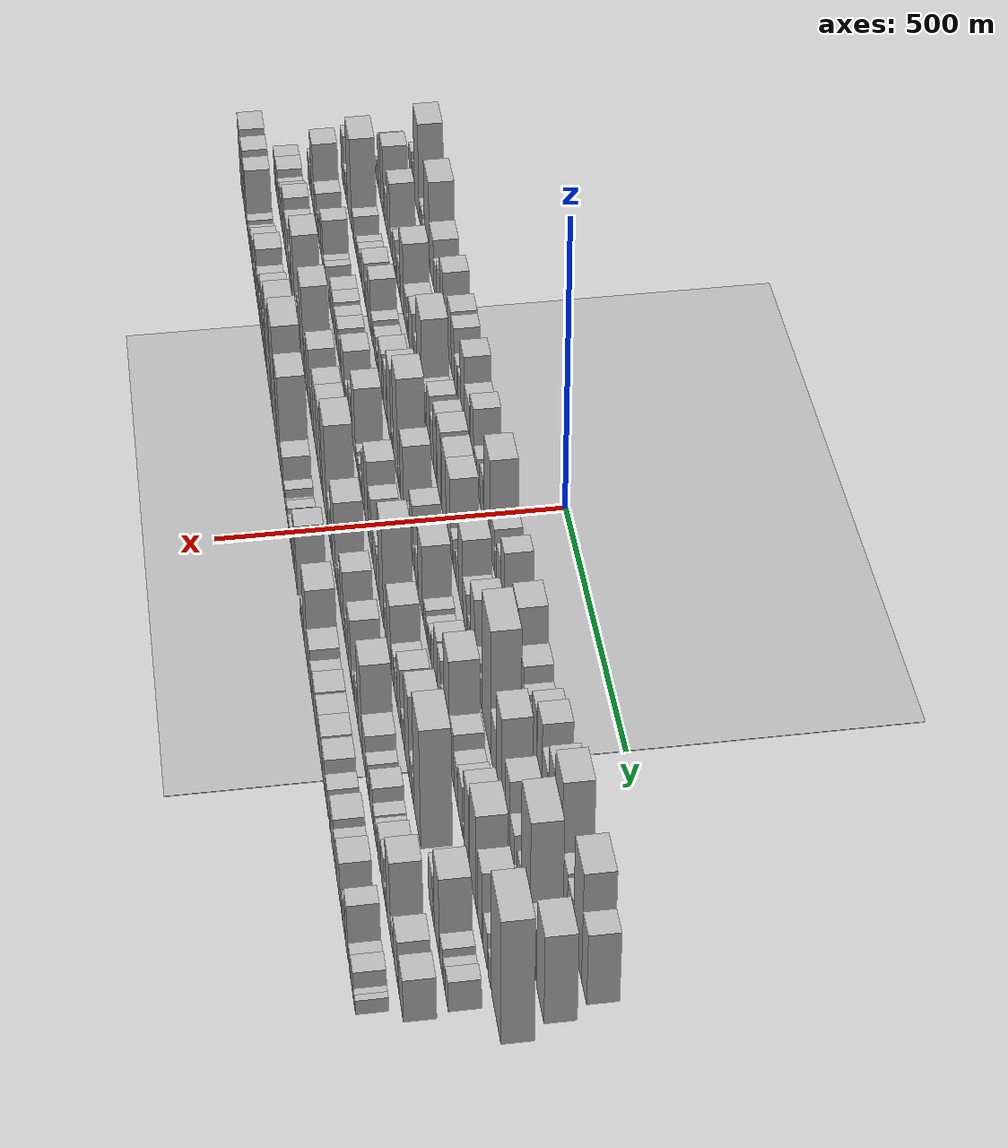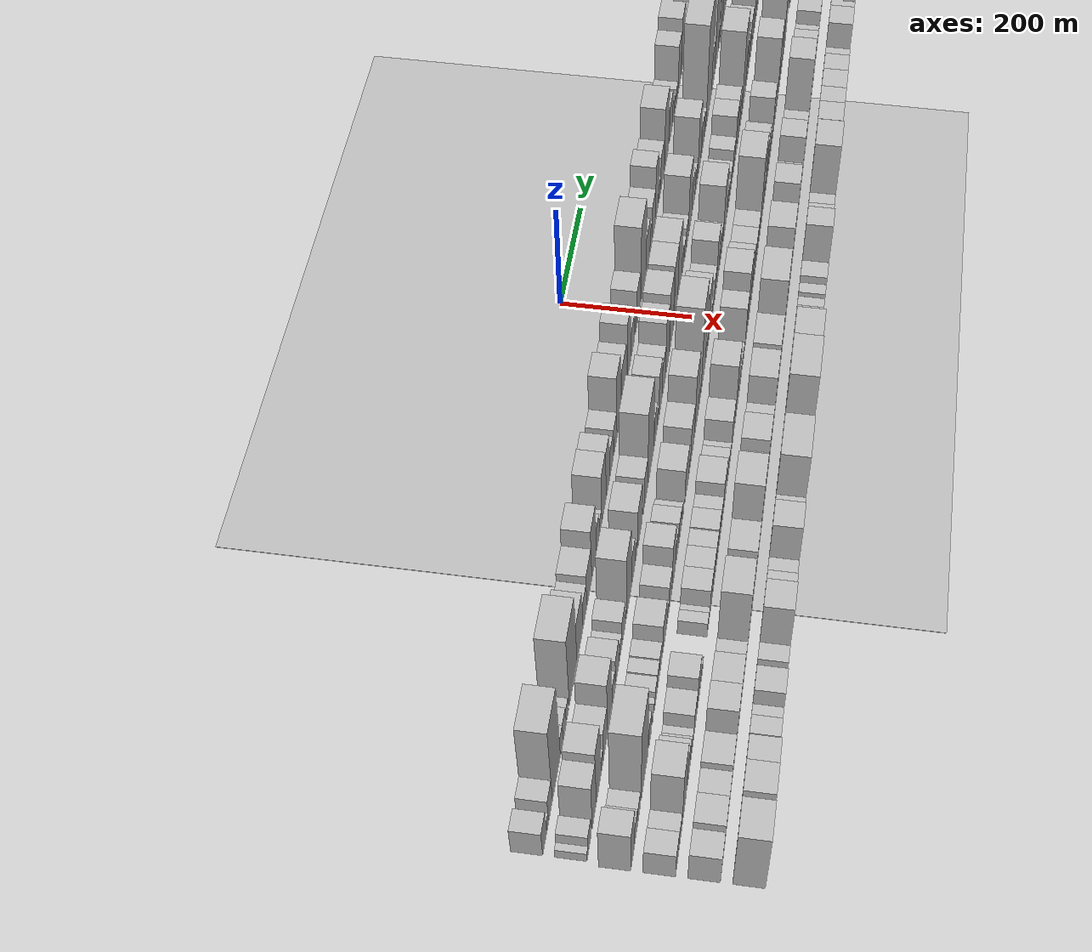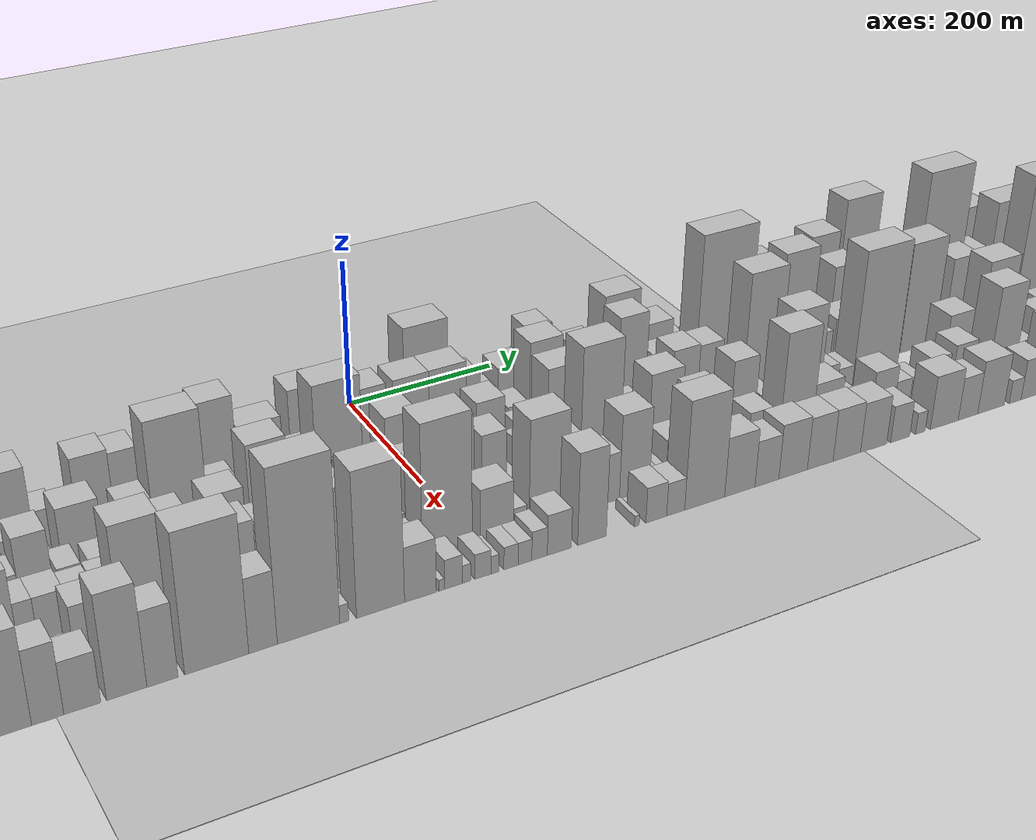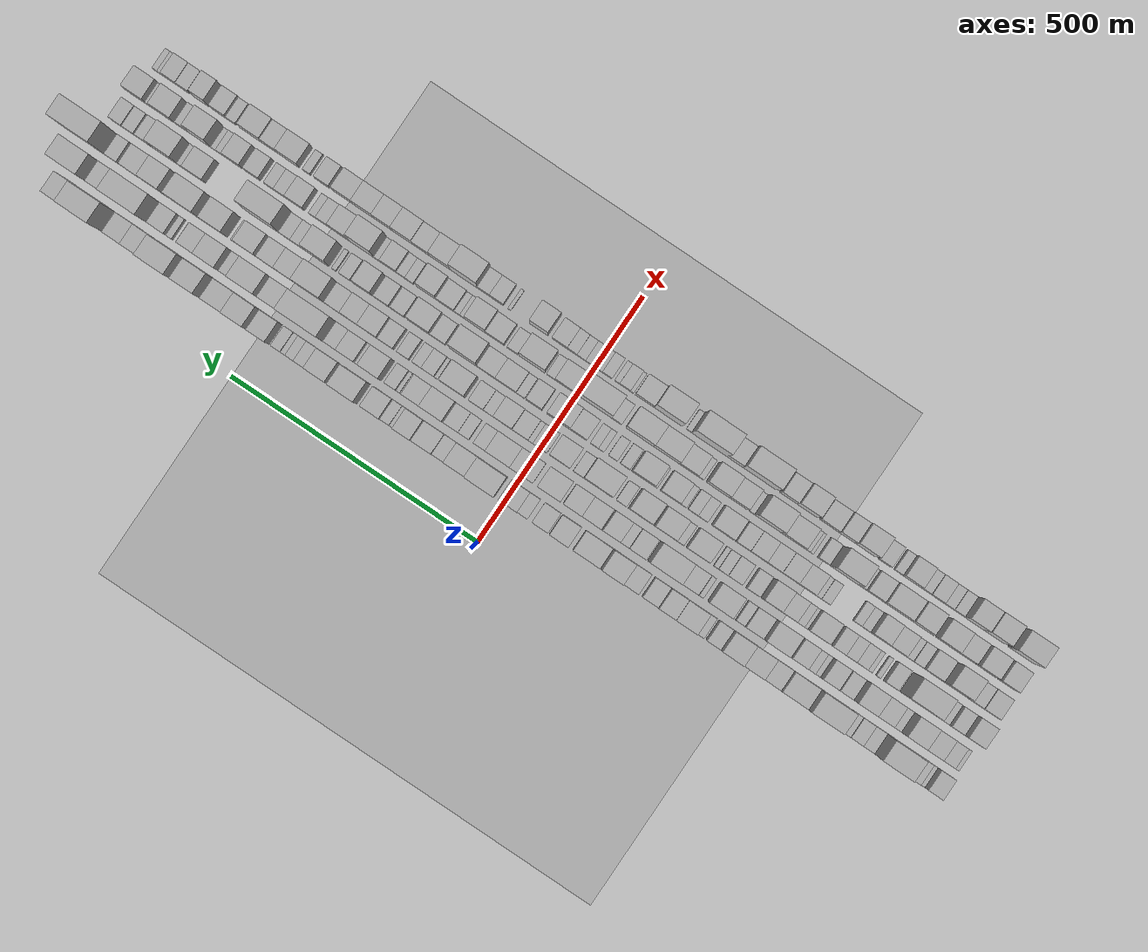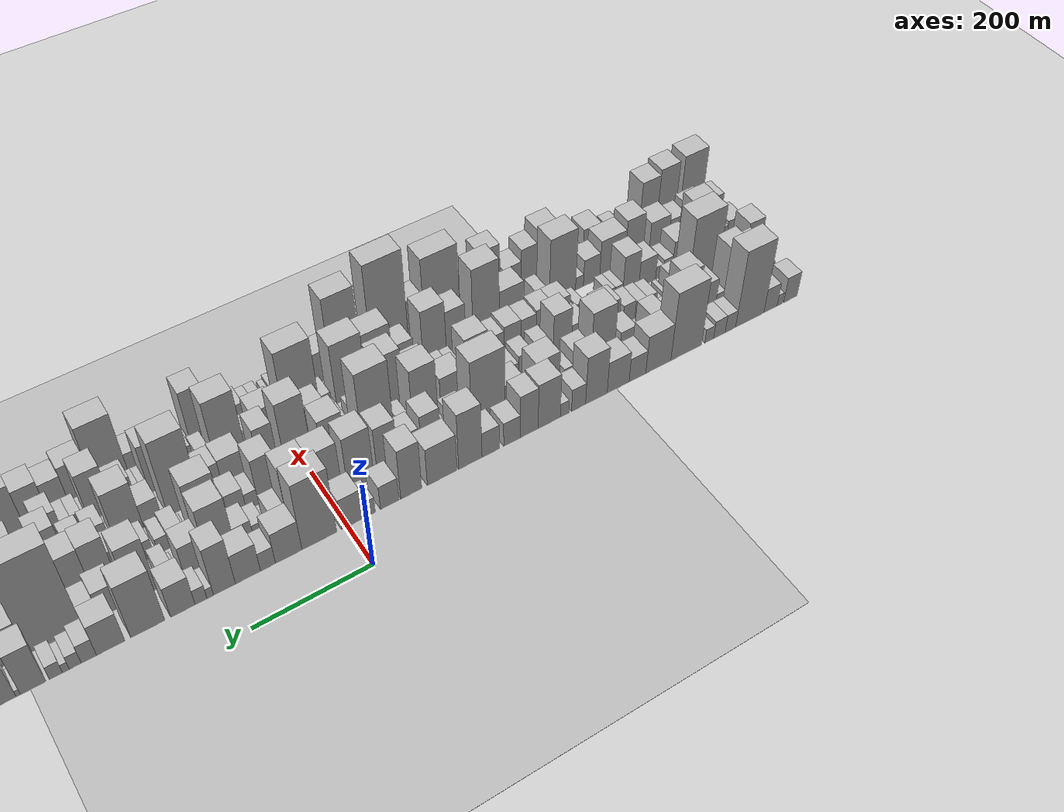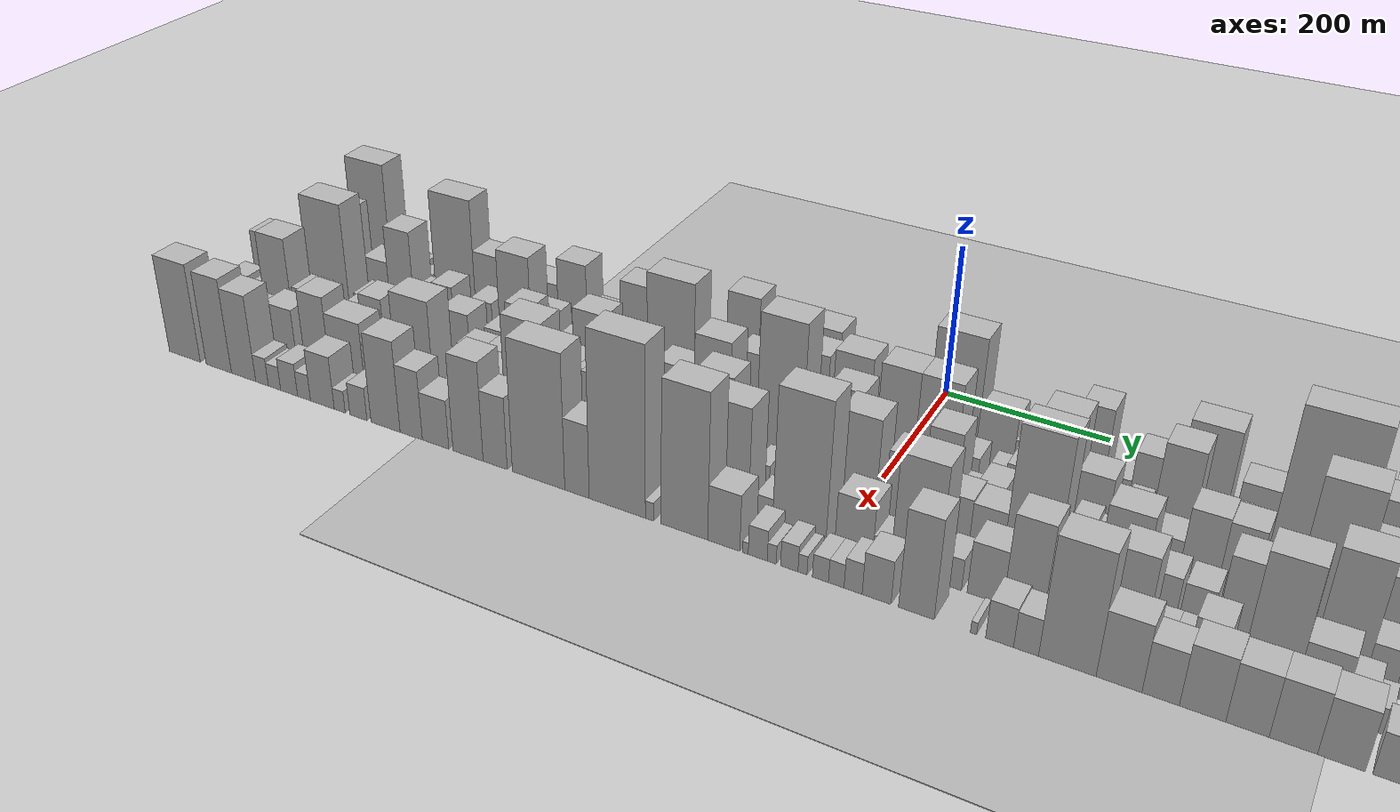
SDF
<?xml version="1.0" encoding="utf-8"?>

<sdf version="1.6">

   <world name="default">

      <gui fullscreen="0">

         <camera name="user_camera">

            <pose>-15 0 4.57585 0 0 0</pose>

            <view_controller>orbit</view_controller>

         </camera>

      </gui>

      <scene>

         <sky>

           <clouds>

             <speed>12</speed>

           </clouds>

         </sky>

         <ambient>0.4 0.4 0.4 1</ambient>

         <background>0.7 0.7 0.7 1</background>

         <shadows>1</shadows>

      </scene>

      <gravity>0 0 -9.8066</gravity>

      <magnetic_field>6e-06 2.3e-05 -4.2e-05</magnetic_field>

      <physics default="0" name="default_physics" type="ode">

         <ode>

            <solver>

               <type>quick</type>

               <iters>10</iters>

               <sor>1.0</sor>

               <use_dynamic_moi_rescaling>0</use_dynamic_moi_rescaling>

            </solver>

            <constraints>

               <cfm>0</cfm>

               <erp>0.2</erp>

               <contact_max_correcting_vel>100</contact_max_correcting_vel>

               <contact_surface_layer>0.001</contact_surface_layer>

            </constraints>

         </ode>

         <max_step_size>0.004</max_step_size>

         <real_time_factor>1</real_time_factor>

         <real_time_update_rate>250</real_time_update_rate>

      </physics>

      <light name="sun" type="directional">

         <cast_shadows>1</cast_shadows>

         <pose>0 0 10 0 0 0</pose>

         <diffuse>0.8 0.8 0.8 1</diffuse>

         <specular>0.2 0.2 0.2 1</specular>

         <attenuation>

            <range>1000</range>

            <constant>0.9</constant>

            <linear>0.01</linear>

            <quadratic>0.001</quadratic>

         </attenuation>

         <direction>-0.5 0.1 -0.9</direction>

      </light>

      <include>

         <name>ground_plane_1</name>

         <uri>model://HANNAS_ground_plane</uri>

         <pose>0 0 0  0 0 0</pose>

      </include>

      <include>

         <name>ground_plane_2</name>

         <uri>model://HANNAS_ground_plane</uri>

         <pose>100 0 0  0 0 0</pose>

      </include>

      <model name="building_1">

         <static>1</static>

         <pose frame="">100.0000 -869.9984 0 0.000000 0.000000 0.000000</pose>

         <link name="link">

            <pose frame="">0 0 30.00 0 0 0</pose>

            <collision name="collision">

               <geometry>

                  <box>

                     <size>40.0000 30.0033 60.0000</size>

                  </box>

               </geometry>

               <max_contacts>10</max_contacts>

               <surface>

                  <contact>

                     <ode/>

                  </contact>

                  <bounce/>

                  <friction>

                     <torsional>

                        <ode/>

                     </torsional>

                     <ode/>

                  </friction>

               </surface>

            </collision>

            <visual name="visual">

               <cast_shadows>0</cast_shadows>

               <geometry>

                  <box>

                     <size>40.0000 30.0033 60.0000</size>

                  </box>

               </geometry>

               <material>

                  <script>

                     <uri>model://HANNAS_wall/materials/scripts</uri>

                     <uri>model://HANNAS_wall/materials/textures</uri>

                     <name>vrc/HANNAS_wall</name>

                  </script>

               </material>

            </visual>

            <self_collide>0</self_collide>

            <enable_wind>0</enable_wind>

            <kinematic>0</kinematic>

         </link>

      </model>

      <model name="building_2">

         <static>1</static>

         <pose frame="">100.0000 -846.1304 0 0.000000 0.000000 0.000000</pose>

         <link name="link">

            <pose frame="">0 0 13.50 0 0 0</pose>

            <collision name="collision">

               <geometry>

                  <box>

                     <size>40.0000 11.7326 27.0000</size>

                  </box>

               </geometry>

               <max_contacts>10</max_contacts>

               <surface>

                  <contact>

                     <ode/>

                  </contact>

                  <bounce/>

                  <friction>

                     <torsional>

                        <ode/>

                     </torsional>

                     <ode/>

                  </friction>

               </surface>

            </collision>

            <visual name="visual">

               <cast_shadows>0</cast_shadows>

               <geometry>

                  <box>

                     <size>40.0000 11.7326 27.0000</size>

                  </box>

               </geometry>

               <material>

                  <script>

                     <uri>model://HANNAS_wall/materials/scripts</uri>

                     <uri>model://HANNAS_wall/materials/textures</uri>

                     <name>vrc/HANNAS_wall</name>

                  </script>

               </material>

            </visual>

            <self_collide>0</self_collide>

            <enable_wind>0</enable_wind>

            <kinematic>0</kinematic>

         </link>

      </model>

      <model name="building_3">

         <static>1</static>

         <pose frame="">100.0000 -825.5178 0 0.000000 0.000000 0.000000</pose>

         <link name="link">

            <pose frame="">0 0 28.50 0 0 0</pose>

            <collision name="collision">

               <geometry>

                  <box>

                     <size>40.0000 29.4925 57.0000</size>

                  </box>

               </geometry>

               <max_contacts>10</max_contacts>

               <surface>

                  <contact>

                     <ode/>

                  </contact>

                  <bounce/>

                  <friction>

                     <torsional>

                        <ode/>

                     </torsional>

                     <ode/>

                  </friction>

               </surface>

            </collision>

            <visual name="visual">

               <cast_shadows>0</cast_shadows>

               <geometry>

                  <box>

                     <size>40.0000 29.4925 57.0000</size>

                  </box>

               </geometry>

               <material>

                  <script>

                     <uri>model://HANNAS_wall/materials/scripts</uri>

                     <uri>model://HANNAS_wall/materials/textures</uri>

                     <name>vrc/HANNAS_wall</name>

                  </script>

               </material>

            </visual>

            <self_collide>0</self_collide>

            <enable_wind>0</enable_wind>

            <kinematic>0</kinematic>

         </link>

      </model>

      <model name="building_4">

         <static>1</static>

         <pose frame="">100.0000 -779.7307 0 0.000000 0.000000 0.000000</pose>

         <link name="link">

            <pose frame="">0 0 90.00 0 0 0</pose>

            <collision name="collision">

               <geometry>

                  <box>

                     <size>40.0000 62.0817 180.0000</size>

                  </box>

               </geometry>

               <max_contacts>10</max_contacts>

               <surface>

                  <contact>

                     <ode/>

                  </contact>

                  <bounce/>

                  <friction>

                     <torsional>

                        <ode/>

                     </torsional>

                     <ode/>

                  </friction>

               </surface>

            </collision>

            <visual name="visual">

               <cast_shadows>0</cast_shadows>

               <geometry>

                  <box>

                     <size>40.0000 62.0817 180.0000</size>

                  </box>

               </geometry>

               <material>

                  <script>

                     <uri>model://HANNAS_wall/materials/scripts</uri>

                     <uri>model://HANNAS_wall/materials/textures</uri>

                     <name>vrc/HANNAS_wall</name>

                  </script>

               </material>

            </visual>

            <self_collide>0</self_collide>

            <enable_wind>0</enable_wind>

            <kinematic>0</kinematic>

         </link>

      </model>

      <model name="building_5">

         <static>1</static>

         <pose frame="">100.0000 -737.5827 0 0.000000 0.000000 0.000000</pose>

         <link name="link">

            <pose frame="">0 0 21.00 0 0 0</pose>

            <collision name="collision">

               <geometry>

                  <box>

                     <size>40.0000 22.2144 42.0000</size>

                  </box>

               </geometry>

               <max_contacts>10</max_contacts>

               <surface>

                  <contact>

                     <ode/>

                  </contact>

                  <bounce/>

                  <friction>

                     <torsional>

                        <ode/>

                     </torsional>

                     <ode/>

                  </friction>

               </surface>

            </collision>

            <visual name="visual">

               <cast_shadows>0</cast_shadows>

               <geometry>

                  <box>

                     <size>40.0000 22.2144 42.0000</size>

                  </box>

               </geometry>

               <material>

                  <script>

                     <uri>model://HANNAS_wall/materials/scripts</uri>

                     <uri>model://HANNAS_wall/materials/textures</uri>

                     <name>vrc/HANNAS_wall</name>

                  </script>

               </material>

            </visual>

            <self_collide>0</self_collide>

            <enable_wind>0</enable_wind>

            <kinematic>0</kinematic>

         </link>

      </model>

      <model name="building_6">

         <static>1</static>

         <pose frame="">100.0000 -713.8823 0 0.000000 0.000000 0.000000</pose>

         <link name="link">

            <pose frame="">0 0 21.00 0 0 0</pose>

            <collision name="collision">

               <geometry>

                  <box>

                     <size>40.0000 25.1864 42.0000</size>

                  </box>

               </geometry>

               <max_contacts>10</max_contacts>

               <surface>

                  <contact>

                     <ode/>

                  </contact>

                  <bounce/>

                  <friction>

                     <torsional>

                        <ode/>

                     </torsional>

                     <ode/>

                  </friction>

               </surface>

            </collision>

            <visual name="visual">

               <cast_shadows>0</cast_shadows>

               <geometry>

                  <box>

                     <size>40.0000 25.1864 42.0000</size>

                  </box>

               </geometry>

               <material>

                  <script>

                     <uri>model://HANNAS_wall/materials/scripts</uri>

                     <uri>model://HANNAS_wall/materials/textures</uri>

                     <name>vrc/HANNAS_wall</name>

                  </script>

               </material>

            </visual>

            <self_collide>0</self_collide>

            <enable_wind>0</enable_wind>

            <kinematic>0</kinematic>

         </link>

      </model>

      <model name="building_7">

         <static>1</static>

         <pose frame="">100.0000 -691.9123 0 0.000000 0.000000 0.000000</pose>

         <link name="link">

            <pose frame="">0 0 16.50 0 0 0</pose>

            <collision name="collision">

               <geometry>

                  <box>

                     <size>40.0000 18.7535 33.0000</size>

                  </box>

               </geometry>

               <max_contacts>10</max_contacts>

               <surface>

                  <contact>

                     <ode/>

                  </contact>

                  <bounce/>

                  <friction>

                     <torsional>

                        <ode/>

                     </torsional>

                     <ode/>

                  </friction>

               </surface>

            </collision>

            <visual name="visual">

               <cast_shadows>0</cast_shadows>

               <geometry>

                  <box>

                     <size>40.0000 18.7535 33.0000</size>

                  </box>

               </geometry>

               <material>

                  <script>

                     <uri>model://HANNAS_wall/materials/scripts</uri>

                     <uri>model://HANNAS_wall/materials/textures</uri>

                     <name>vrc/HANNAS_wall</name>

                  </script>

               </material>

            </visual>

            <self_collide>0</self_collide>

            <enable_wind>0</enable_wind>

            <kinematic>0</kinematic>

         </link>

      </model>

      <model name="building_8">

         <static>1</static>

         <pose frame="">100.0000 -643.2716 0 0.000000 0.000000 0.000000</pose>

         <link name="link">

            <pose frame="">0 0 81.00 0 0 0</pose>

            <collision name="collision">

               <geometry>

                  <box>

                     <size>40.0000 64.5278 162.0000</size>

                  </box>

               </geometry>

               <max_contacts>10</max_contacts>

               <surface>

                  <contact>

                     <ode/>

                  </contact>

                  <bounce/>

                  <friction>

                     <torsional>

                        <ode/>

                     </torsional>

                     <ode/>

                  </friction>

               </surface>

            </collision>

            <visual name="visual">

               <cast_shadows>0</cast_shadows>

               <geometry>

                  <box>

                     <size>40.0000 64.5278 162.0000</size>

                  </box>

               </geometry>

               <material>

                  <script>

                     <uri>model://HANNAS_wall/materials/scripts</uri>

                     <uri>model://HANNAS_wall/materials/textures</uri>

                     <name>vrc/HANNAS_wall</name>

                  </script>

               </material>

            </visual>

            <self_collide>0</self_collide>

            <enable_wind>0</enable_wind>

            <kinematic>0</kinematic>

         </link>

      </model>

      <model name="building_9">

         <static>1</static>

         <pose frame="">100.0000 -585.0858 0 0.000000 0.000000 0.000000</pose>

         <link name="link">

            <pose frame="">0 0 45.00 0 0 0</pose>

            <collision name="collision">

               <geometry>

                  <box>

                     <size>40.0000 51.8437 90.0000</size>

                  </box>

               </geometry>

               <max_contacts>10</max_contacts>

               <surface>

                  <contact>

                     <ode/>

                  </contact>

                  <bounce/>

                  <friction>

                     <torsional>

                        <ode/>

                     </torsional>

                     <ode/>

                  </friction>

               </surface>

            </collision>

            <visual name="visual">

               <cast_shadows>0</cast_shadows>

               <geometry>

                  <box>

                     <size>40.0000 51.8437 90.0000</size>

                  </box>

               </geometry>

               <material>

                  <script>

                     <uri>model://HANNAS_wall/materials/scripts</uri>

                     <uri>model://HANNAS_wall/materials/textures</uri>

                     <name>vrc/HANNAS_wall</name>

                  </script>

               </material>

            </visual>

            <self_collide>0</self_collide>

            <enable_wind>0</enable_wind>

            <kinematic>0</kinematic>

         </link>

      </model>

      <model name="building_10">

         <static>1</static>

         <pose frame="">100.0000 -542.1855 0 0.000000 0.000000 0.000000</pose>

         <link name="link">

            <pose frame="">0 0 28.50 0 0 0</pose>

            <collision name="collision">

               <geometry>

                  <box>

                     <size>40.0000 33.9569 57.0000</size>

                  </box>

               </geometry>

               <max_contacts>10</max_contacts>

               <surface>

                  <contact>

                     <ode/>

                  </contact>

                  <bounce/>

                  <friction>

                     <torsional>

                        <ode/>

                     </torsional>

                     <ode/>

                  </friction>

               </surface>

            </collision>

            <visual name="visual">

               <cast_shadows>0</cast_shadows>

               <geometry>

                  <box>

                     <size>40.0000 33.9569 57.0000</size>

                  </box>

               </geometry>

               <material>

                  <script>

                     <uri>model://HANNAS_wall/materials/scripts</uri>

                     <uri>model://HANNAS_wall/materials/textures</uri>

                     <name>vrc/HANNAS_wall</name>

                  </script>

               </material>

            </visual>

            <self_collide>0</self_collide>

            <enable_wind>0</enable_wind>

            <kinematic>0</kinematic>

         </link>

      </model>

      <model name="building_11">

         <static>1</static>

         <pose frame="">100.0000 -503.0766 0 0.000000 0.000000 0.000000</pose>

         <link name="link">

            <pose frame="">0 0 37.50 0 0 0</pose>

            <collision name="collision">

               <geometry>

                  <box>

                     <size>40.0000 44.2611 75.0000</size>

                  </box>

               </geometry>

               <max_contacts>10</max_contacts>

               <surface>

                  <contact>

                     <ode/>

                  </contact>

                  <bounce/>

                  <friction>

                     <torsional>

                        <ode/>

                     </torsional>

                     <ode/>

                  </friction>

               </surface>

            </collision>

            <visual name="visual">

               <cast_shadows>0</cast_shadows>

               <geometry>

                  <box>

                     <size>40.0000 44.2611 75.0000</size>

                  </box>

               </geometry>

               <material>

                  <script>

                     <uri>model://HANNAS_wall/materials/scripts</uri>

                     <uri>model://HANNAS_wall/materials/textures</uri>

                     <name>vrc/HANNAS_wall</name>

                  </script>

               </material>

            </visual>

            <self_collide>0</self_collide>

            <enable_wind>0</enable_wind>

            <kinematic>0</kinematic>

         </link>

      </model>

      <model name="building_12">

         <static>1</static>

         <pose frame="">100.0000 -459.4445 0 0.000000 0.000000 0.000000</pose>

         <link name="link">

            <pose frame="">0 0 57.00 0 0 0</pose>

            <collision name="collision">

               <geometry>

                  <box>

                     <size>40.0000 43.0030 114.0000</size>

                  </box>

               </geometry>

               <max_contacts>10</max_contacts>

               <surface>

                  <contact>

                     <ode/>

                  </contact>

                  <bounce/>

                  <friction>

                     <torsional>

                        <ode/>

                     </torsional>

                     <ode/>

                  </friction>

               </surface>

            </collision>

            <visual name="visual">

               <cast_shadows>0</cast_shadows>

               <geometry>

                  <box>

                     <size>40.0000 43.0030 114.0000</size>

                  </box>

               </geometry>

               <material>

                  <script>

                     <uri>model://HANNAS_wall/materials/scripts</uri>

                     <uri>model://HANNAS_wall/materials/textures</uri>

                     <name>vrc/HANNAS_wall</name>

                  </script>

               </material>

            </visual>

            <self_collide>0</self_collide>

            <enable_wind>0</enable_wind>

            <kinematic>0</kinematic>

         </link>

      </model>

      <model name="building_13">

         <static>1</static>

         <pose frame="">100.0000 -424.0741 0 0.000000 0.000000 0.000000</pose>

         <link name="link">

            <pose frame="">0 0 27.00 0 0 0</pose>

            <collision name="collision">

               <geometry>

                  <box>

                     <size>40.0000 27.7378 54.0000</size>

                  </box>

               </geometry>

               <max_contacts>10</max_contacts>

               <surface>

                  <contact>

                     <ode/>

                  </contact>

                  <bounce/>

                  <friction>

                     <torsional>

                        <ode/>

                     </torsional>

                     <ode/>

                  </friction>

               </surface>

            </collision>

            <visual name="visual">

               <cast_shadows>0</cast_shadows>

               <geometry>

                  <box>

                     <size>40.0000 27.7378 54.0000</size>

                  </box>

               </geometry>

               <material>

                  <script>

                     <uri>model://HANNAS_wall/materials/scripts</uri>

                     <uri>model://HANNAS_wall/materials/textures</uri>

                     <name>vrc/HANNAS_wall</name>

                  </script>

               </material>

            </visual>

            <self_collide>0</self_collide>

            <enable_wind>0</enable_wind>

            <kinematic>0</kinematic>

         </link>

      </model>

      <model name="building_14">

         <static>1</static>

         <pose frame="">100.0000 -396.7473 0 0.000000 0.000000 0.000000</pose>

         <link name="link">

            <pose frame="">0 0 16.50 0 0 0</pose>

            <collision name="collision">

               <geometry>

                  <box>

                     <size>40.0000 16.9158 33.0000</size>

                  </box>

               </geometry>

               <max_contacts>10</max_contacts>

               <surface>

                  <contact>

                     <ode/>

                  </contact>

                  <bounce/>

                  <friction>

                     <torsional>

                        <ode/>

                     </torsional>

                     <ode/>

                  </friction>

               </surface>

            </collision>

            <visual name="visual">

               <cast_shadows>0</cast_shadows>

               <geometry>

                  <box>

                     <size>40.0000 16.9158 33.0000</size>

                  </box>

               </geometry>

               <material>

                  <script>

                     <uri>model://HANNAS_wall/materials/scripts</uri>

                     <uri>model://HANNAS_wall/materials/textures</uri>

                     <name>vrc/HANNAS_wall</name>

                  </script>

               </material>

            </visual>

            <self_collide>0</self_collide>

            <enable_wind>0</enable_wind>

            <kinematic>0</kinematic>

         </link>

      </model>

      <model name="building_15">

         <static>1</static>

         <pose frame="">100.0000 -366.8694 0 0.000000 0.000000 0.000000</pose>

         <link name="link">

            <pose frame="">0 0 54.00 0 0 0</pose>

            <collision name="collision">

               <geometry>

                  <box>

                     <size>40.0000 42.8400 108.0000</size>

                  </box>

               </geometry>

               <max_contacts>10</max_contacts>

               <surface>

                  <contact>

                     <ode/>

                  </contact>

                  <bounce/>

                  <friction>

                     <torsional>

                        <ode/>

                     </torsional>

                     <ode/>

                  </friction>

               </surface>

            </collision>

            <visual name="visual">

               <cast_shadows>0</cast_shadows>

               <geometry>

                  <box>

                     <size>40.0000 42.8400 108.0000</size>

                  </box>

               </geometry>

               <material>

                  <script>

                     <uri>model://HANNAS_wall/materials/scripts</uri>

                     <uri>model://HANNAS_wall/materials/textures</uri>

                     <name>vrc/HANNAS_wall</name>

                  </script>

               </material>

            </visual>

            <self_collide>0</self_collide>

            <enable_wind>0</enable_wind>

            <kinematic>0</kinematic>

         </link>

      </model>

      <model name="building_16">

         <static>1</static>

         <pose frame="">100.0000 -328.5726 0 0.000000 0.000000 0.000000</pose>

         <link name="link">

            <pose frame="">0 0 51.00 0 0 0</pose>

            <collision name="collision">

               <geometry>

                  <box>

                     <size>40.0000 33.7535 102.0000</size>

                  </box>

               </geometry>

               <max_contacts>10</max_contacts>

               <surface>

                  <contact>

                     <ode/>

                  </contact>

                  <bounce/>

                  <friction>

                     <torsional>

                        <ode/>

                     </torsional>

                     <ode/>

                  </friction>

               </surface>

            </collision>

            <visual name="visual">

               <cast_shadows>0</cast_shadows>

               <geometry>

                  <box>

                     <size>40.0000 33.7535 102.0000</size>

                  </box>

               </geometry>

               <material>

                  <script>

                     <uri>model://HANNAS_wall/materials/scripts</uri>

                     <uri>model://HANNAS_wall/materials/textures</uri>

                     <name>vrc/HANNAS_wall</name>

                  </script>

               </material>

            </visual>

            <self_collide>0</self_collide>

            <enable_wind>0</enable_wind>

            <kinematic>0</kinematic>

         </link>

      </model>

      <model name="building_17">

         <static>1</static>

         <pose frame="">100.0000 -295.9605 0 0.000000 0.000000 0.000000</pose>

         <link name="link">

            <pose frame="">0 0 28.50 0 0 0</pose>

            <collision name="collision">

               <geometry>

                  <box>

                     <size>40.0000 31.4708 57.0000</size>

                  </box>

               </geometry>

               <max_contacts>10</max_contacts>

               <surface>

                  <contact>

                     <ode/>

                  </contact>

                  <bounce/>

                  <friction>

                     <torsional>

                        <ode/>

                     </torsional>

                     <ode/>

                  </friction>

               </surface>

            </collision>

            <visual name="visual">

               <cast_shadows>0</cast_shadows>

               <geometry>

                  <box>

                     <size>40.0000 31.4708 57.0000</size>

                  </box>

               </geometry>

               <material>

                  <script>

                     <uri>model://HANNAS_wall/materials/scripts</uri>

                     <uri>model://HANNAS_wall/materials/textures</uri>

                     <name>vrc/HANNAS_wall</name>

                  </script>

               </material>

            </visual>

            <self_collide>0</self_collide>

            <enable_wind>0</enable_wind>

            <kinematic>0</kinematic>

         </link>

      </model>

      <model name="building_18">

         <static>1</static>

         <pose frame="">100.0000 -255.9308 0 0.000000 0.000000 0.000000</pose>

         <link name="link">

            <pose frame="">0 0 30.00 0 0 0</pose>

            <collision name="collision">

               <geometry>

                  <box>

                     <size>40.0000 32.5886 60.0000</size>

                  </box>

               </geometry>

               <max_contacts>10</max_contacts>

               <surface>

                  <contact>

                     <ode/>

                  </contact>

                  <bounce/>

                  <friction>

                     <torsional>

                        <ode/>

                     </torsional>

                     <ode/>

                  </friction>

               </surface>

            </collision>

            <visual name="visual">

               <cast_shadows>0</cast_shadows>

               <geometry>

                  <box>

                     <size>40.0000 32.5886 60.0000</size>

                  </box>

               </geometry>

               <material>

                  <script>

                     <uri>model://HANNAS_wall/materials/scripts</uri>

                     <uri>model://HANNAS_wall/materials/textures</uri>

                     <name>vrc/HANNAS_wall</name>

                  </script>

               </material>

            </visual>

            <self_collide>0</self_collide>

            <enable_wind>0</enable_wind>

            <kinematic>0</kinematic>

         </link>

      </model>

      <model name="building_19">

         <static>1</static>

         <pose frame="">100.0000 -218.0816 0 0.000000 0.000000 0.000000</pose>

         <link name="link">

            <pose frame="">0 0 67.50 0 0 0</pose>

            <collision name="collision">

               <geometry>

                  <box>

                     <size>40.0000 43.1098 135.0000</size>

                  </box>

               </geometry>

               <max_contacts>10</max_contacts>

               <surface>

                  <contact>

                     <ode/>

                  </contact>

                  <bounce/>

                  <friction>

                     <torsional>

                        <ode/>

                     </torsional>

                     <ode/>

                  </friction>

               </surface>

            </collision>

            <visual name="visual">

               <cast_shadows>0</cast_shadows>

               <geometry>

                  <box>

                     <size>40.0000 43.1098 135.0000</size>

                  </box>

               </geometry>

               <material>

                  <script>

                     <uri>model://HANNAS_wall/materials/scripts</uri>

                     <uri>model://HANNAS_wall/materials/textures</uri>

                     <name>vrc/HANNAS_wall</name>

                  </script>

               </material>

            </visual>

            <self_collide>0</self_collide>

            <enable_wind>0</enable_wind>

            <kinematic>0</kinematic>

         </link>

      </model>

      <model name="building_20">

         <static>1</static>

         <pose frame="">100.0000 -166.6295 0 0.000000 0.000000 0.000000</pose>

         <link name="link">

            <pose frame="">0 0 45.00 0 0 0</pose>

            <collision name="collision">

               <geometry>

                  <box>

                     <size>40.0000 53.7943 90.0000</size>

                  </box>

               </geometry>

               <max_contacts>10</max_contacts>

               <surface>

                  <contact>

                     <ode/>

                  </contact>

                  <bounce/>

                  <friction>

                     <torsional>

                        <ode/>

                     </torsional>

                     <ode/>

                  </friction>

               </surface>

            </collision>

            <visual name="visual">

               <cast_shadows>0</cast_shadows>

               <geometry>

                  <box>

                     <size>40.0000 53.7943 90.0000</size>

                  </box>

               </geometry>

               <material>

                  <script>

                     <uri>model://HANNAS_wall/materials/scripts</uri>

                     <uri>model://HANNAS_wall/materials/textures</uri>

                     <name>vrc/HANNAS_wall</name>

                  </script>

               </material>

            </visual>

            <self_collide>0</self_collide>

            <enable_wind>0</enable_wind>

            <kinematic>0</kinematic>

         </link>

      </model>

      <model name="building_21">

         <static>1</static>

         <pose frame="">100.0000 -111.0268 0 0.000000 0.000000 0.000000</pose>

         <link name="link">

            <pose frame="">0 0 60.00 0 0 0</pose>

            <collision name="collision">

               <geometry>

                  <box>

                     <size>40.0000 37.4112 120.0000</size>

                  </box>

               </geometry>

               <max_contacts>10</max_contacts>

               <surface>

                  <contact>

                     <ode/>

                  </contact>

                  <bounce/>

                  <friction>

                     <torsional>

                        <ode/>

                     </torsional>

                     <ode/>

                  </friction>

               </surface>

            </collision>

            <visual name="visual">

               <cast_shadows>0</cast_shadows>

               <geometry>

                  <box>

                     <size>40.0000 37.4112 120.0000</size>

                  </box>

               </geometry>

               <material>

                  <script>

                     <uri>model://HANNAS_wall/materials/scripts</uri>

                     <uri>model://HANNAS_wall/materials/textures</uri>

                     <name>vrc/HANNAS_wall</name>

                  </script>

               </material>

            </visual>

            <self_collide>0</self_collide>

            <enable_wind>0</enable_wind>

            <kinematic>0</kinematic>

         </link>

      </model>

      <model name="building_22">

         <static>1</static>

         <pose frame="">100.0000 -73.0119 0 0.000000 0.000000 0.000000</pose>

         <link name="link">

            <pose frame="">0 0 28.50 0 0 0</pose>

            <collision name="collision">

               <geometry>

                  <box>

                     <size>40.0000 32.6185 57.0000</size>

                  </box>

               </geometry>

               <max_contacts>10</max_contacts>

               <surface>

                  <contact>

                     <ode/>

                  </contact>

                  <bounce/>

                  <friction>

                     <torsional>

                        <ode/>

                     </torsional>

                     <ode/>

                  </friction>

               </surface>

            </collision>

            <visual name="visual">

               <cast_shadows>0</cast_shadows>

               <geometry>

                  <box>

                     <size>40.0000 32.6185 57.0000</size>

                  </box>

               </geometry>

               <material>

                  <script>

                     <uri>model://HANNAS_wall/materials/scripts</uri>

                     <uri>model://HANNAS_wall/materials/textures</uri>

                     <name>vrc/HANNAS_wall</name>

                  </script>

               </material>

            </visual>

            <self_collide>0</self_collide>

            <enable_wind>0</enable_wind>

            <kinematic>0</kinematic>

         </link>

      </model>

      <model name="building_23">

         <static>1</static>

         <pose frame="">100.0000 -37.2203 0 0.000000 0.000000 0.000000</pose>

         <link name="link">

            <pose frame="">0 0 19.50 0 0 0</pose>

            <collision name="collision">

               <geometry>

                  <box>

                     <size>40.0000 20.9647 39.0000</size>

                  </box>

               </geometry>

               <max_contacts>10</max_contacts>

               <surface>

                  <contact>

                     <ode/>

                  </contact>

                  <bounce/>

                  <friction>

                     <torsional>

                        <ode/>

                     </torsional>

                     <ode/>

                  </friction>

               </surface>

            </collision>

            <visual name="visual">

               <cast_shadows>0</cast_shadows>

               <geometry>

                  <box>

                     <size>40.0000 20.9647 39.0000</size>

                  </box>

               </geometry>

               <material>

                  <script>

                     <uri>model://HANNAS_wall/materials/scripts</uri>

                     <uri>model://HANNAS_wall/materials/textures</uri>

                     <name>vrc/HANNAS_wall</name>

                  </script>

               </material>

            </visual>

            <self_collide>0</self_collide>

            <enable_wind>0</enable_wind>

            <kinematic>0</kinematic>

         </link>

      </model>

      <model name="building_24">

         <static>1</static>

         <pose frame="">100.0000 -7.9457 0 0.000000 0.000000 0.000000</pose>

         <link name="link">

            <pose frame="">0 0 37.50 0 0 0</pose>

            <collision name="collision">

               <geometry>

                  <box>

                     <size>40.0000 37.5844 75.0000</size>

                  </box>

               </geometry>

               <max_contacts>10</max_contacts>

               <surface>

                  <contact>

                     <ode/>

                  </contact>

                  <bounce/>

                  <friction>

                     <torsional>

                        <ode/>

                     </torsional>

                     <ode/>

                  </friction>

               </surface>

            </collision>

            <visual name="visual">

               <cast_shadows>0</cast_shadows>

               <geometry>

                  <box>

                     <size>40.0000 37.5844 75.0000</size>

                  </box>

               </geometry>

               <material>

                  <script>

                     <uri>model://HANNAS_wall/materials/scripts</uri>

                     <uri>model://HANNAS_wall/materials/textures</uri>

                     <name>vrc/HANNAS_wall</name>

                  </script>

               </material>

            </visual>

            <self_collide>0</self_collide>

            <enable_wind>0</enable_wind>

            <kinematic>0</kinematic>

         </link>

      </model>

      <model name="building_25">

         <static>1</static>

         <pose frame="">100.0000 48.2471 0 0.000000 0.000000 0.000000</pose>

         <link name="link">

            <pose frame="">0 0 81.00 0 0 0</pose>

            <collision name="collision">

               <geometry>

                  <box>

                     <size>40.0000 58.8012 162.0000</size>

                  </box>

               </geometry>

               <max_contacts>10</max_contacts>

               <surface>

                  <contact>

                     <ode/>

                  </contact>

                  <bounce/>

                  <friction>

                     <torsional>

                        <ode/>

                     </torsional>

                     <ode/>

                  </friction>

               </surface>

            </collision>

            <visual name="visual">

               <cast_shadows>0</cast_shadows>

               <geometry>

                  <box>

                     <size>40.0000 58.8012 162.0000</size>

                  </box>

               </geometry>

               <material>

                  <script>

                     <uri>model://HANNAS_wall/materials/scripts</uri>

                     <uri>model://HANNAS_wall/materials/textures</uri>

                     <name>vrc/HANNAS_wall</name>

                  </script>

               </material>

            </visual>

            <self_collide>0</self_collide>

            <enable_wind>0</enable_wind>

            <kinematic>0</kinematic>

         </link>

      </model>

      <model name="building_26">

         <static>1</static>

         <pose frame="">100.0000 99.6738 0 0.000000 0.000000 0.000000</pose>

         <link name="link">

            <pose frame="">0 0 37.50 0 0 0</pose>

            <collision name="collision">

               <geometry>

                  <box>

                     <size>40.0000 44.0522 75.0000</size>

                  </box>

               </geometry>

               <max_contacts>10</max_contacts>

               <surface>

                  <contact>

                     <ode/>

                  </contact>

                  <bounce/>

                  <friction>

                     <torsional>

                        <ode/>

                     </torsional>

                     <ode/>

                  </friction>

               </surface>

            </collision>

            <visual name="visual">

               <cast_shadows>0</cast_shadows>

               <geometry>

                  <box>

                     <size>40.0000 44.0522 75.0000</size>

                  </box>

               </geometry>

               <material>

                  <script>

                     <uri>model://HANNAS_wall/materials/scripts</uri>

                     <uri>model://HANNAS_wall/materials/textures</uri>

                     <name>vrc/HANNAS_wall</name>

                  </script>

               </material>

            </visual>

            <self_collide>0</self_collide>

            <enable_wind>0</enable_wind>

            <kinematic>0</kinematic>

         </link>

      </model>

      <model name="building_27">

         <static>1</static>

         <pose frame="">100.0000 133.9592 0 0.000000 0.000000 0.000000</pose>

         <link name="link">

            <pose frame="">0 0 22.50 0 0 0</pose>

            <collision name="collision">

               <geometry>

                  <box>

                     <size>40.0000 24.5187 45.0000</size>

                  </box>

               </geometry>

               <max_contacts>10</max_contacts>

               <surface>

                  <contact>

                     <ode/>

                  </contact>

                  <bounce/>

                  <friction>

                     <torsional>

                        <ode/>

                     </torsional>

                     <ode/>

                  </friction>

               </surface>

            </collision>

            <visual name="visual">

               <cast_shadows>0</cast_shadows>

               <geometry>

                  <box>

                     <size>40.0000 24.5187 45.0000</size>

                  </box>

               </geometry>

               <material>

                  <script>

                     <uri>model://HANNAS_wall/materials/scripts</uri>

                     <uri>model://HANNAS_wall/materials/textures</uri>

                     <name>vrc/HANNAS_wall</name>

                  </script>

               </material>

            </visual>

            <self_collide>0</self_collide>

            <enable_wind>0</enable_wind>

            <kinematic>0</kinematic>

         </link>

      </model>

      <model name="building_28">

         <static>1</static>

         <pose frame="">100.0000 166.5390 0 0.000000 0.000000 0.000000</pose>

         <link name="link">

            <pose frame="">0 0 36.00 0 0 0</pose>

            <collision name="collision">

               <geometry>

                  <box>

                     <size>40.0000 40.6410 72.0000</size>

                  </box>

               </geometry>

               <max_contacts>10</max_contacts>

               <surface>

                  <contact>

                     <ode/>

                  </contact>

                  <bounce/>

                  <friction>

                     <torsional>

                        <ode/>

                     </torsional>

                     <ode/>

                  </friction>

               </surface>

            </collision>

            <visual name="visual">

               <cast_shadows>0</cast_shadows>

               <geometry>

                  <box>

                     <size>40.0000 40.6410 72.0000</size>

                  </box>

               </geometry>

               <material>

                  <script>

                     <uri>model://HANNAS_wall/materials/scripts</uri>

                     <uri>model://HANNAS_wall/materials/textures</uri>

                     <name>vrc/HANNAS_wall</name>

                  </script>

               </material>

            </visual>

            <self_collide>0</self_collide>

            <enable_wind>0</enable_wind>

            <kinematic>0</kinematic>

         </link>

      </model>

      <model name="building_29">

         <static>1</static>

         <pose frame="">100.0000 204.4119 0 0.000000 0.000000 0.000000</pose>

         <link name="link">

            <pose frame="">0 0 58.50 0 0 0</pose>

            <collision name="collision">

               <geometry>

                  <box>

                     <size>40.0000 35.1048 117.0000</size>

                  </box>

               </geometry>

               <max_contacts>10</max_contacts>

               <surface>

                  <contact>

                     <ode/>

                  </contact>

                  <bounce/>

                  <friction>

                     <torsional>

                        <ode/>

                     </torsional>

                     <ode/>

                  </friction>

               </surface>

            </collision>

            <visual name="visual">

               <cast_shadows>0</cast_shadows>

               <geometry>

                  <box>

                     <size>40.0000 35.1048 117.0000</size>

                  </box>

               </geometry>

               <material>

                  <script>

                     <uri>model://HANNAS_wall/materials/scripts</uri>

                     <uri>model://HANNAS_wall/materials/textures</uri>

                     <name>vrc/HANNAS_wall</name>

                  </script>

               </material>

            </visual>

            <self_collide>0</self_collide>

            <enable_wind>0</enable_wind>

            <kinematic>0</kinematic>

         </link>

      </model>

      <model name="building_30">

         <static>1</static>

         <pose frame="">100.0000 227.2108 0 0.000000 0.000000 0.000000</pose>

         <link name="link">

            <pose frame="">0 0 12.00 0 0 0</pose>

            <collision name="collision">

               <geometry>

                  <box>

                     <size>40.0000 10.4929 24.0000</size>

                  </box>

               </geometry>

               <max_contacts>10</max_contacts>

               <surface>

                  <contact>

                     <ode/>

                  </contact>

                  <bounce/>

                  <friction>

                     <torsional>

                        <ode/>

                     </torsional>

                     <ode/>

                  </friction>

               </surface>

            </collision>

            <visual name="visual">

               <cast_shadows>0</cast_shadows>

               <geometry>

                  <box>

                     <size>40.0000 10.4929 24.0000</size>

                  </box>

               </geometry>

               <material>

                  <script>

                     <uri>model://HANNAS_wall/materials/scripts</uri>

                     <uri>model://HANNAS_wall/materials/textures</uri>

                     <name>vrc/HANNAS_wall</name>

                  </script>

               </material>

            </visual>

            <self_collide>0</self_collide>

            <enable_wind>0</enable_wind>

            <kinematic>0</kinematic>

         </link>

      </model>

      <model name="building_31">

         <static>1</static>

         <pose frame="">100.0000 241.8036 0 0.000000 0.000000 0.000000</pose>

         <link name="link">

            <pose frame="">0 0 18.00 0 0 0</pose>

            <collision name="collision">

               <geometry>

                  <box>

                     <size>40.0000 18.6928 36.0000</size>

                  </box>

               </geometry>

               <max_contacts>10</max_contacts>

               <surface>

                  <contact>

                     <ode/>

                  </contact>

                  <bounce/>

                  <friction>

                     <torsional>

                        <ode/>

                     </torsional>

                     <ode/>

                  </friction>

               </surface>

            </collision>

            <visual name="visual">

               <cast_shadows>0</cast_shadows>

               <geometry>

                  <box>

                     <size>40.0000 18.6928 36.0000</size>

                  </box>

               </geometry>

               <material>

                  <script>

                     <uri>model://HANNAS_wall/materials/scripts</uri>

                     <uri>model://HANNAS_wall/materials/textures</uri>

                     <name>vrc/HANNAS_wall</name>

                  </script>

               </material>

            </visual>

            <self_collide>0</self_collide>

            <enable_wind>0</enable_wind>

            <kinematic>0</kinematic>

         </link>

      </model>

      <model name="building_32">

         <static>1</static>

         <pose frame="">100.0000 270.3446 0 0.000000 0.000000 0.000000</pose>

         <link name="link">

            <pose frame="">0 0 37.50 0 0 0</pose>

            <collision name="collision">

               <geometry>

                  <box>

                     <size>40.0000 38.3891 75.0000</size>

                  </box>

               </geometry>

               <max_contacts>10</max_contacts>

               <surface>

                  <contact>

                     <ode/>

                  </contact>

                  <bounce/>

                  <friction>

                     <torsional>

                        <ode/>

                     </torsional>

                     <ode/>

                  </friction>

               </surface>

            </collision>

            <visual name="visual">

               <cast_shadows>0</cast_shadows>

               <geometry>

                  <box>

                     <size>40.0000 38.3891 75.0000</size>

                  </box>

               </geometry>

               <material>

                  <script>

                     <uri>model://HANNAS_wall/materials/scripts</uri>

                     <uri>model://HANNAS_wall/materials/textures</uri>

                     <name>vrc/HANNAS_wall</name>

                  </script>

               </material>

            </visual>

            <self_collide>0</self_collide>

            <enable_wind>0</enable_wind>

            <kinematic>0</kinematic>

         </link>

      </model>

      <model name="building_33">

         <static>1</static>

         <pose frame="">100.0000 324.7302 0 0.000000 0.000000 0.000000</pose>

         <link name="link">

            <pose frame="">0 0 66.00 0 0 0</pose>

            <collision name="collision">

               <geometry>

                  <box>

                     <size>40.0000 52.3822 132.0000</size>

                  </box>

               </geometry>

               <max_contacts>10</max_contacts>

               <surface>

                  <contact>

                     <ode/>

                  </contact>

                  <bounce/>

                  <friction>

                     <torsional>

                        <ode/>

                     </torsional>

                     <ode/>

                  </friction>

               </surface>

            </collision>

            <visual name="visual">

               <cast_shadows>0</cast_shadows>

               <geometry>

                  <box>

                     <size>40.0000 52.3822 132.0000</size>

                  </box>

               </geometry>

               <material>

                  <script>

                     <uri>model://HANNAS_wall/materials/scripts</uri>

                     <uri>model://HANNAS_wall/materials/textures</uri>

                     <name>vrc/HANNAS_wall</name>

                  </script>

               </material>

            </visual>

            <self_collide>0</self_collide>

            <enable_wind>0</enable_wind>

            <kinematic>0</kinematic>

         </link>

      </model>

      <model name="building_34">

         <static>1</static>

         <pose frame="">100.0000 381.3301 0 0.000000 0.000000 0.000000</pose>

         <link name="link">

            <pose frame="">0 0 37.50 0 0 0</pose>

            <collision name="collision">

               <geometry>

                  <box>

                     <size>40.0000 42.8177 75.0000</size>

                  </box>

               </geometry>

               <max_contacts>10</max_contacts>

               <surface>

                  <contact>

                     <ode/>

                  </contact>

                  <bounce/>

                  <friction>

                     <torsional>

                        <ode/>

                     </torsional>

                     <ode/>

                  </friction>

               </surface>

            </collision>

            <visual name="visual">

               <cast_shadows>0</cast_shadows>

               <geometry>

                  <box>

                     <size>40.0000 42.8177 75.0000</size>

                  </box>

               </geometry>

               <material>

                  <script>

                     <uri>model://HANNAS_wall/materials/scripts</uri>

                     <uri>model://HANNAS_wall/materials/textures</uri>

                     <name>vrc/HANNAS_wall</name>

                  </script>

               </material>

            </visual>

            <self_collide>0</self_collide>

            <enable_wind>0</enable_wind>

            <kinematic>0</kinematic>

         </link>

      </model>

      <model name="building_35">

         <static>1</static>

         <pose frame="">100.0000 414.0542 0 0.000000 0.000000 0.000000</pose>

         <link name="link">

            <pose frame="">0 0 22.50 0 0 0</pose>

            <collision name="collision">

               <geometry>

                  <box>

                     <size>40.0000 22.6305 45.0000</size>

                  </box>

               </geometry>

               <max_contacts>10</max_contacts>

               <surface>

                  <contact>

                     <ode/>

                  </contact>

                  <bounce/>

                  <friction>

                     <torsional>

                        <ode/>

                     </torsional>

                     <ode/>

                  </friction>

               </surface>

            </collision>

            <visual name="visual">

               <cast_shadows>0</cast_shadows>

               <geometry>

                  <box>

                     <size>40.0000 22.6305 45.0000</size>

                  </box>

               </geometry>

               <material>

                  <script>

                     <uri>model://HANNAS_wall/materials/scripts</uri>

                     <uri>model://HANNAS_wall/materials/textures</uri>

                     <name>vrc/HANNAS_wall</name>

                  </script>

               </material>

            </visual>

            <self_collide>0</self_collide>

            <enable_wind>0</enable_wind>

            <kinematic>0</kinematic>

         </link>

      </model>

      <model name="building_36">

         <static>1</static>

         <pose frame="">100.0000 434.1898 0 0.000000 0.000000 0.000000</pose>

         <link name="link">

            <pose frame="">0 0 16.50 0 0 0</pose>

            <collision name="collision">

               <geometry>

                  <box>

                     <size>40.0000 17.6406 33.0000</size>

                  </box>

               </geometry>

               <max_contacts>10</max_contacts>

               <surface>

                  <contact>

                     <ode/>

                  </contact>

                  <bounce/>

                  <friction>

                     <torsional>

                        <ode/>

                     </torsional>

                     <ode/>

                  </friction>

               </surface>

            </collision>

            <visual name="visual">

               <cast_shadows>0</cast_shadows>

               <geometry>

                  <box>

                     <size>40.0000 17.6406 33.0000</size>

                  </box>

               </geometry>

               <material>

                  <script>

                     <uri>model://HANNAS_wall/materials/scripts</uri>

                     <uri>model://HANNAS_wall/materials/textures</uri>

                     <name>vrc/HANNAS_wall</name>

                  </script>

               </material>

            </visual>

            <self_collide>0</self_collide>

            <enable_wind>0</enable_wind>

            <kinematic>0</kinematic>

         </link>

      </model>

      <model name="building_37">

         <static>1</static>

         <pose frame="">100.0000 447.9389 0 0.000000 0.000000 0.000000</pose>

         <link name="link">

            <pose frame="">0 0 10.50 0 0 0</pose>

            <collision name="collision">

               <geometry>

                  <box>

                     <size>40.0000 9.8575 21.0000</size>

                  </box>

               </geometry>

               <max_contacts>10</max_contacts>

               <surface>

                  <contact>

                     <ode/>

                  </contact>

                  <bounce/>

                  <friction>

                     <torsional>

                        <ode/>

                     </torsional>

                     <ode/>

                  </friction>

               </surface>

            </collision>

            <visual name="visual">

               <cast_shadows>0</cast_shadows>

               <geometry>

                  <box>

                     <size>40.0000 9.8575 21.0000</size>

                  </box>

               </geometry>

               <material>

                  <script>

                     <uri>model://HANNAS_wall/materials/scripts</uri>

                     <uri>model://HANNAS_wall/materials/textures</uri>

                     <name>vrc/HANNAS_wall</name>

                  </script>

               </material>

            </visual>

            <self_collide>0</self_collide>

            <enable_wind>0</enable_wind>

            <kinematic>0</kinematic>

         </link>

      </model>

      <model name="building_38">

         <static>1</static>

         <pose frame="">100.0000 462.6290 0 0.000000 0.000000 0.000000</pose>

         <link name="link">

            <pose frame="">0 0 16.50 0 0 0</pose>

            <collision name="collision">

               <geometry>

                  <box>

                     <size>40.0000 19.5228 33.0000</size>

                  </box>

               </geometry>

               <max_contacts>10</max_contacts>

               <surface>

                  <contact>

                     <ode/>

                  </contact>

                  <bounce/>

                  <friction>

                     <torsional>

                        <ode/>

                     </torsional>

                     <ode/>

                  </friction>

               </surface>

            </collision>

            <visual name="visual">

               <cast_shadows>0</cast_shadows>

               <geometry>

                  <box>

                     <size>40.0000 19.5228 33.0000</size>

                  </box>

               </geometry>

               <material>

                  <script>

                     <uri>model://HANNAS_wall/materials/scripts</uri>

                     <uri>model://HANNAS_wall/materials/textures</uri>

                     <name>vrc/HANNAS_wall</name>

                  </script>

               </material>

            </visual>

            <self_collide>0</self_collide>

            <enable_wind>0</enable_wind>

            <kinematic>0</kinematic>

         </link>

      </model>

      <model name="building_39">

         <static>1</static>

         <pose frame="">100.0000 495.7797 0 0.000000 0.000000 0.000000</pose>

         <link name="link">

            <pose frame="">0 0 51.00 0 0 0</pose>

            <collision name="collision">

               <geometry>

                  <box>

                     <size>40.0000 36.7786 102.0000</size>

                  </box>

               </geometry>

               <max_contacts>10</max_contacts>

               <surface>

                  <contact>

                     <ode/>

                  </contact>

                  <bounce/>

                  <friction>

                     <torsional>

                        <ode/>

                     </torsional>

                     <ode/>

                  </friction>

               </surface>

            </collision>

            <visual name="visual">

               <cast_shadows>0</cast_shadows>

               <geometry>

                  <box>

                     <size>40.0000 36.7786 102.0000</size>

                  </box>

               </geometry>

               <material>

                  <script>

                     <uri>model://HANNAS_wall/materials/scripts</uri>

                     <uri>model://HANNAS_wall/materials/textures</uri>

                     <name>vrc/HANNAS_wall</name>

                  </script>

               </material>

            </visual>

            <self_collide>0</self_collide>

            <enable_wind>0</enable_wind>

            <kinematic>0</kinematic>

         </link>

      </model>

      <model name="building_40">

         <static>1</static>

         <pose frame="">100.0000 517.2920 0 0.000000 0.000000 0.000000</pose>

         <link name="link">

            <pose frame="">0 0 7.50 0 0 0</pose>

            <collision name="collision">

               <geometry>

                  <box>

                     <size>40.0000 6.2460 15.0000</size>

                  </box>

               </geometry>

               <max_contacts>10</max_contacts>

               <surface>

                  <contact>

                     <ode/>

                  </contact>

                  <bounce/>

                  <friction>

                     <torsional>

                        <ode/>

                     </torsional>

                     <ode/>

                  </friction>

               </surface>

            </collision>

            <visual name="visual">

               <cast_shadows>0</cast_shadows>

               <geometry>

                  <box>

                     <size>40.0000 6.2460 15.0000</size>

                  </box>

               </geometry>

               <material>

                  <script>

                     <uri>model://HANNAS_wall/materials/scripts</uri>

                     <uri>model://HANNAS_wall/materials/textures</uri>

                     <name>vrc/HANNAS_wall</name>

                  </script>

               </material>

            </visual>

            <self_collide>0</self_collide>

            <enable_wind>0</enable_wind>

            <kinematic>0</kinematic>

         </link>

      </model>

      <model name="building_41">

         <static>1</static>

         <pose frame="">100.0000 541.7731 0 0.000000 0.000000 0.000000</pose>

         <link name="link">

            <pose frame="">0 0 61.50 0 0 0</pose>

            <collision name="collision">

               <geometry>

                  <box>

                     <size>40.0000 42.7162 123.0000</size>

                  </box>

               </geometry>

               <max_contacts>10</max_contacts>

               <surface>

                  <contact>

                     <ode/>

                  </contact>

                  <bounce/>

                  <friction>

                     <torsional>

                        <ode/>

                     </torsional>

                     <ode/>

                  </friction>

               </surface>

            </collision>

            <visual name="visual">

               <cast_shadows>0</cast_shadows>

               <geometry>

                  <box>

                     <size>40.0000 42.7162 123.0000</size>

                  </box>

               </geometry>

               <material>

                  <script>

                     <uri>model://HANNAS_wall/materials/scripts</uri>

                     <uri>model://HANNAS_wall/materials/textures</uri>

                     <name>vrc/HANNAS_wall</name>

                  </script>

               </material>

            </visual>

            <self_collide>0</self_collide>

            <enable_wind>0</enable_wind>

            <kinematic>0</kinematic>

         </link>

      </model>

      <model name="building_42">

         <static>1</static>

         <pose frame="">100.0000 586.1143 0 0.000000 0.000000 0.000000</pose>

         <link name="link">

            <pose frame="">0 0 42.00 0 0 0</pose>

            <collision name="collision">

               <geometry>

                  <box>

                     <size>40.0000 45.9663 84.0000</size>

                  </box>

               </geometry>

               <max_contacts>10</max_contacts>

               <surface>

                  <contact>

                     <ode/>

                  </contact>

                  <bounce/>

                  <friction>

                     <torsional>

                        <ode/>

                     </torsional>

                     <ode/>

                  </friction>

               </surface>

            </collision>

            <visual name="visual">

               <cast_shadows>0</cast_shadows>

               <geometry>

                  <box>

                     <size>40.0000 45.9663 84.0000</size>

                  </box>

               </geometry>

               <material>

                  <script>

                     <uri>model://HANNAS_wall/materials/scripts</uri>

                     <uri>model://HANNAS_wall/materials/textures</uri>

                     <name>vrc/HANNAS_wall</name>

                  </script>

               </material>

            </visual>

            <self_collide>0</self_collide>

            <enable_wind>0</enable_wind>

            <kinematic>0</kinematic>

         </link>

      </model>

      <model name="building_43">

         <static>1</static>

         <pose frame="">100.0000 612.8241 0 0.000000 0.000000 0.000000</pose>

         <link name="link">

            <pose frame="">0 0 9.00 0 0 0</pose>

            <collision name="collision">

               <geometry>

                  <box>

                     <size>40.0000 7.4533 18.0000</size>

                  </box>

               </geometry>

               <max_contacts>10</max_contacts>

               <surface>

                  <contact>

                     <ode/>

                  </contact>

                  <bounce/>

                  <friction>

                     <torsional>

                        <ode/>

                     </torsional>

                     <ode/>

                  </friction>

               </surface>

            </collision>

            <visual name="visual">

               <cast_shadows>0</cast_shadows>

               <geometry>

                  <box>

                     <size>40.0000 7.4533 18.0000</size>

                  </box>

               </geometry>

               <material>

                  <script>

                     <uri>model://HANNAS_wall/materials/scripts</uri>

                     <uri>model://HANNAS_wall/materials/textures</uri>

                     <name>vrc/HANNAS_wall</name>

                  </script>

               </material>

            </visual>

            <self_collide>0</self_collide>

            <enable_wind>0</enable_wind>

            <kinematic>0</kinematic>

         </link>

      </model>

      <model name="building_44">

         <static>1</static>

         <pose frame="">100.0000 639.4314 0 0.000000 0.000000 0.000000</pose>

         <link name="link">

            <pose frame="">0 0 69.00 0 0 0</pose>

            <collision name="collision">

               <geometry>

                  <box>

                     <size>40.0000 45.7614 138.0000</size>

                  </box>

               </geometry>

               <max_contacts>10</max_contacts>

               <surface>

                  <contact>

                     <ode/>

                  </contact>

                  <bounce/>

                  <friction>

                     <torsional>

                        <ode/>

                     </torsional>

                     <ode/>

                  </friction>

               </surface>

            </collision>

            <visual name="visual">

               <cast_shadows>0</cast_shadows>

               <geometry>

                  <box>

                     <size>40.0000 45.7614 138.0000</size>

                  </box>

               </geometry>

               <material>

                  <script>

                     <uri>model://HANNAS_wall/materials/scripts</uri>

                     <uri>model://HANNAS_wall/materials/textures</uri>

                     <name>vrc/HANNAS_wall</name>

                  </script>

               </material>

            </visual>

            <self_collide>0</self_collide>

            <enable_wind>0</enable_wind>

            <kinematic>0</kinematic>

         </link>

      </model>

      <model name="building_45">

         <static>1</static>

         <pose frame="">100.0000 697.5358 0 0.000000 0.000000 0.000000</pose>

         <link name="link">

            <pose frame="">0 0 90.00 0 0 0</pose>

            <collision name="collision">

               <geometry>

                  <box>

                     <size>40.0000 58.4473 180.0000</size>

                  </box>

               </geometry>

               <max_contacts>10</max_contacts>

               <surface>

                  <contact>

                     <ode/>

                  </contact>

                  <bounce/>

                  <friction>

                     <torsional>

                        <ode/>

                     </torsional>

                     <ode/>

                  </friction>

               </surface>

            </collision>

            <visual name="visual">

               <cast_shadows>0</cast_shadows>

               <geometry>

                  <box>

                     <size>40.0000 58.4473 180.0000</size>

                  </box>

               </geometry>

               <material>

                  <script>

                     <uri>model://HANNAS_wall/materials/scripts</uri>

                     <uri>model://HANNAS_wall/materials/textures</uri>

                     <name>vrc/HANNAS_wall</name>

                  </script>

               </material>

            </visual>

            <self_collide>0</self_collide>

            <enable_wind>0</enable_wind>

            <kinematic>0</kinematic>

         </link>

      </model>

      <model name="building_46">

         <static>1</static>

         <pose frame="">100.0000 753.8862 0 0.000000 0.000000 0.000000</pose>

         <link name="link">

            <pose frame="">0 0 34.50 0 0 0</pose>

            <collision name="collision">

               <geometry>

                  <box>

                     <size>40.0000 36.2536 69.0000</size>

                  </box>

               </geometry>

               <max_contacts>10</max_contacts>

               <surface>

                  <contact>

                     <ode/>

                  </contact>

                  <bounce/>

                  <friction>

                     <torsional>

                        <ode/>

                     </torsional>

                     <ode/>

                  </friction>

               </surface>

            </collision>

            <visual name="visual">

               <cast_shadows>0</cast_shadows>

               <geometry>

                  <box>

                     <size>40.0000 36.2536 69.0000</size>

                  </box>

               </geometry>

               <material>

                  <script>

                     <uri>model://HANNAS_wall/materials/scripts</uri>

                     <uri>model://HANNAS_wall/materials/textures</uri>

                     <name>vrc/HANNAS_wall</name>

                  </script>

               </material>

            </visual>

            <self_collide>0</self_collide>

            <enable_wind>0</enable_wind>

            <kinematic>0</kinematic>

         </link>

      </model>

      <model name="building_47">

         <static>1</static>

         <pose frame="">100.0000 790.1084 0 0.000000 0.000000 0.000000</pose>

         <link name="link">

            <pose frame="">0 0 31.50 0 0 0</pose>

            <collision name="collision">

               <geometry>

                  <box>

                     <size>40.0000 36.1908 63.0000</size>

                  </box>

               </geometry>

               <max_contacts>10</max_contacts>

               <surface>

                  <contact>

                     <ode/>

                  </contact>

                  <bounce/>

                  <friction>

                     <torsional>

                        <ode/>

                     </torsional>

                     <ode/>

                  </friction>

               </surface>

            </collision>

            <visual name="visual">

               <cast_shadows>0</cast_shadows>

               <geometry>

                  <box>

                     <size>40.0000 36.1908 63.0000</size>

                  </box>

               </geometry>

               <material>

                  <script>

                     <uri>model://HANNAS_wall/materials/scripts</uri>

                     <uri>model://HANNAS_wall/materials/textures</uri>

                     <name>vrc/HANNAS_wall</name>

                  </script>

               </material>

            </visual>

            <self_collide>0</self_collide>

            <enable_wind>0</enable_wind>

            <kinematic>0</kinematic>

         </link>

      </model>

      <model name="building_48">

         <static>1</static>

         <pose frame="">100.0000 850.2389 0 0.000000 0.000000 0.000000</pose>

         <link name="link">

            <pose frame="">0 0 91.50 0 0 0</pose>

            <collision name="collision">

               <geometry>

                  <box>

                     <size>40.0000 64.0702 183.0000</size>

                  </box>

               </geometry>

               <max_contacts>10</max_contacts>

               <surface>

                  <contact>

                     <ode/>

                  </contact>

                  <bounce/>

                  <friction>

                     <torsional>

                        <ode/>

                     </torsional>

                     <ode/>

                  </friction>

               </surface>

            </collision>

            <visual name="visual">

               <cast_shadows>0</cast_shadows>

               <geometry>

                  <box>

                     <size>40.0000 64.0702 183.0000</size>

                  </box>

               </geometry>

               <material>

                  <script>

                     <uri>model://HANNAS_wall/materials/scripts</uri>

                     <uri>model://HANNAS_wall/materials/textures</uri>

                     <name>vrc/HANNAS_wall</name>

                  </script>

               </material>

            </visual>

            <self_collide>0</self_collide>

            <enable_wind>0</enable_wind>

            <kinematic>0</kinematic>

         </link>

      </model>

      <model name="building_49">

         <static>1</static>

         <pose frame="">100.0000 901.6904 0 0.000000 0.000000 0.000000</pose>

         <link name="link">

            <pose frame="">0 0 60.00 0 0 0</pose>

            <collision name="collision">

               <geometry>

                  <box>

                     <size>40.0000 38.8329 120.0000</size>

                  </box>

               </geometry>

               <max_contacts>10</max_contacts>

               <surface>

                  <contact>

                     <ode/>

                  </contact>

                  <bounce/>

                  <friction>

                     <torsional>

                        <ode/>

                     </torsional>

                     <ode/>

                  </friction>

               </surface>

            </collision>

            <visual name="visual">

               <cast_shadows>0</cast_shadows>

               <geometry>

                  <box>

                     <size>40.0000 38.8329 120.0000</size>

                  </box>

               </geometry>

               <material>

                  <script>

                     <uri>model://HANNAS_wall/materials/scripts</uri>

                     <uri>model://HANNAS_wall/materials/textures</uri>

                     <name>vrc/HANNAS_wall</name>

                  </script>

               </material>

            </visual>

            <self_collide>0</self_collide>

            <enable_wind>0</enable_wind>

            <kinematic>0</kinematic>

         </link>

      </model>

      <model name="building_50">

         <static>1</static>

         <pose frame="">155.0000 -879.7726 0 0.000000 0.000000 0.000000</pose>

         <link name="link">

            <pose frame="">0 0 10.50 0 0 0</pose>

            <collision name="collision">

               <geometry>

                  <box>

                     <size>40.0000 10.4548 21.0000</size>

                  </box>

               </geometry>

               <max_contacts>10</max_contacts>

               <surface>

                  <contact>

                     <ode/>

                  </contact>

                  <bounce/>

                  <friction>

                     <torsional>

                        <ode/>

                     </torsional>

                     <ode/>

                  </friction>

               </surface>

            </collision>

            <visual name="visual">

               <cast_shadows>0</cast_shadows>

               <geometry>

                  <box>

                     <size>40.0000 10.4548 21.0000</size>

                  </box>

               </geometry>

               <material>

                  <script>

                     <uri>model://HANNAS_wall/materials/scripts</uri>

                     <uri>model://HANNAS_wall/materials/textures</uri>

                     <name>vrc/HANNAS_wall</name>

                  </script>

               </material>

            </visual>

            <self_collide>0</self_collide>

            <enable_wind>0</enable_wind>

            <kinematic>0</kinematic>

         </link>

      </model>

      <model name="building_51">

         <static>1</static>

         <pose frame="">155.0000 -861.9768 0 0.000000 0.000000 0.000000</pose>

         <link name="link">

            <pose frame="">0 0 22.50 0 0 0</pose>

            <collision name="collision">

               <geometry>

                  <box>

                     <size>40.0000 25.1369 45.0000</size>

                  </box>

               </geometry>

               <max_contacts>10</max_contacts>

               <surface>

                  <contact>

                     <ode/>

                  </contact>

                  <bounce/>

                  <friction>

                     <torsional>

                        <ode/>

                     </torsional>

                     <ode/>

                  </friction>

               </surface>

            </collision>

            <visual name="visual">

               <cast_shadows>0</cast_shadows>

               <geometry>

                  <box>

                     <size>40.0000 25.1369 45.0000</size>

                  </box>

               </geometry>

               <material>

                  <script>

                     <uri>model://HANNAS_wall/materials/scripts</uri>

                     <uri>model://HANNAS_wall/materials/textures</uri>

                     <name>vrc/HANNAS_wall</name>

                  </script>

               </material>

            </visual>

            <self_collide>0</self_collide>

            <enable_wind>0</enable_wind>

            <kinematic>0</kinematic>

         </link>

      </model>

      <model name="building_52">

         <static>1</static>

         <pose frame="">155.0000 -824.1083 0 0.000000 0.000000 0.000000</pose>

         <link name="link">

            <pose frame="">0 0 55.50 0 0 0</pose>

            <collision name="collision">

               <geometry>

                  <box>

                     <size>40.0000 34.6000 111.0000</size>

                  </box>

               </geometry>

               <max_contacts>10</max_contacts>

               <surface>

                  <contact>

                     <ode/>

                  </contact>

                  <bounce/>

                  <friction>

                     <torsional>

                        <ode/>

                     </torsional>

                     <ode/>

                  </friction>

               </surface>

            </collision>

            <visual name="visual">

               <cast_shadows>0</cast_shadows>

               <geometry>

                  <box>

                     <size>40.0000 34.6000 111.0000</size>

                  </box>

               </geometry>

               <material>

                  <script>

                     <uri>model://HANNAS_wall/materials/scripts</uri>

                     <uri>model://HANNAS_wall/materials/textures</uri>

                     <name>vrc/HANNAS_wall</name>

                  </script>

               </material>

            </visual>

            <self_collide>0</self_collide>

            <enable_wind>0</enable_wind>

            <kinematic>0</kinematic>

         </link>

      </model>

      <model name="building_53">

         <static>1</static>

         <pose frame="">155.0000 -786.7428 0 0.000000 0.000000 0.000000</pose>

         <link name="link">

            <pose frame="">0 0 66.00 0 0 0</pose>

            <collision name="collision">

               <geometry>

                  <box>

                     <size>40.0000 40.1310 132.0000</size>

                  </box>

               </geometry>

               <max_contacts>10</max_contacts>

               <surface>

                  <contact>

                     <ode/>

                  </contact>

                  <bounce/>

                  <friction>

                     <torsional>

                        <ode/>

                     </torsional>

                     <ode/>

                  </friction>

               </surface>

            </collision>

            <visual name="visual">

               <cast_shadows>0</cast_shadows>

               <geometry>

                  <box>

                     <size>40.0000 40.1310 132.0000</size>

                  </box>

               </geometry>

               <material>

                  <script>

                     <uri>model://HANNAS_wall/materials/scripts</uri>

                     <uri>model://HANNAS_wall/materials/textures</uri>

                     <name>vrc/HANNAS_wall</name>

                  </script>

               </material>

            </visual>

            <self_collide>0</self_collide>

            <enable_wind>0</enable_wind>

            <kinematic>0</kinematic>

         </link>

      </model>

      <model name="building_54">

         <static>1</static>

         <pose frame="">155.0000 -757.3948 0 0.000000 0.000000 0.000000</pose>

         <link name="link">

            <pose frame="">0 0 16.50 0 0 0</pose>

            <collision name="collision">

               <geometry>

                  <box>

                     <size>40.0000 18.5649 33.0000</size>

                  </box>

               </geometry>

               <max_contacts>10</max_contacts>

               <surface>

                  <contact>

                     <ode/>

                  </contact>

                  <bounce/>

                  <friction>

                     <torsional>

                        <ode/>

                     </torsional>

                     <ode/>

                  </friction>

               </surface>

            </collision>

            <visual name="visual">

               <cast_shadows>0</cast_shadows>

               <geometry>

                  <box>

                     <size>40.0000 18.5649 33.0000</size>

                  </box>

               </geometry>

               <material>

                  <script>

                     <uri>model://HANNAS_wall/materials/scripts</uri>

                     <uri>model://HANNAS_wall/materials/textures</uri>

                     <name>vrc/HANNAS_wall</name>

                  </script>

               </material>

            </visual>

            <self_collide>0</self_collide>

            <enable_wind>0</enable_wind>

            <kinematic>0</kinematic>

         </link>

      </model>

      <model name="building_55">

         <static>1</static>

         <pose frame="">155.0000 -728.7192 0 0.000000 0.000000 0.000000</pose>

         <link name="link">

            <pose frame="">0 0 36.00 0 0 0</pose>

            <collision name="collision">

               <geometry>

                  <box>

                     <size>40.0000 38.7863 72.0000</size>

                  </box>

               </geometry>

               <max_contacts>10</max_contacts>

               <surface>

                  <contact>

                     <ode/>

                  </contact>

                  <bounce/>

                  <friction>

                     <torsional>

                        <ode/>

                     </torsional>

                     <ode/>

                  </friction>

               </surface>

            </collision>

            <visual name="visual">

               <cast_shadows>0</cast_shadows>

               <geometry>

                  <box>

                     <size>40.0000 38.7863 72.0000</size>

                  </box>

               </geometry>

               <material>

                  <script>

                     <uri>model://HANNAS_wall/materials/scripts</uri>

                     <uri>model://HANNAS_wall/materials/textures</uri>

                     <name>vrc/HANNAS_wall</name>

                  </script>

               </material>

            </visual>

            <self_collide>0</self_collide>

            <enable_wind>0</enable_wind>

            <kinematic>0</kinematic>

         </link>

      </model>

      <model name="building_56">

         <static>1</static>

         <pose frame="">155.0000 -689.2966 0 0.000000 0.000000 0.000000</pose>

         <link name="link">

            <pose frame="">0 0 63.00 0 0 0</pose>

            <collision name="collision">

               <geometry>

                  <box>

                     <size>40.0000 40.0589 126.0000</size>

                  </box>

               </geometry>

               <max_contacts>10</max_contacts>

               <surface>

                  <contact>

                     <ode/>

                  </contact>

                  <bounce/>

                  <friction>

                     <torsional>

                        <ode/>

                     </torsional>

                     <ode/>

                  </friction>

               </surface>

            </collision>

            <visual name="visual">

               <cast_shadows>0</cast_shadows>

               <geometry>

                  <box>

                     <size>40.0000 40.0589 126.0000</size>

                  </box>

               </geometry>

               <material>

                  <script>

                     <uri>model://HANNAS_wall/materials/scripts</uri>

                     <uri>model://HANNAS_wall/materials/textures</uri>

                     <name>vrc/HANNAS_wall</name>

                  </script>

               </material>

            </visual>

            <self_collide>0</self_collide>

            <enable_wind>0</enable_wind>

            <kinematic>0</kinematic>

         </link>

      </model>

      <model name="building_57">

         <static>1</static>

         <pose frame="">155.0000 -655.8796 0 0.000000 0.000000 0.000000</pose>

         <link name="link">

            <pose frame="">0 0 22.50 0 0 0</pose>

            <collision name="collision">

               <geometry>

                  <box>

                     <size>40.0000 26.7751 45.0000</size>

                  </box>

               </geometry>

               <max_contacts>10</max_contacts>

               <surface>

                  <contact>

                     <ode/>

                  </contact>

                  <bounce/>

                  <friction>

                     <torsional>

                        <ode/>

                     </torsional>

                     <ode/>

                  </friction>

               </surface>

            </collision>

            <visual name="visual">

               <cast_shadows>0</cast_shadows>

               <geometry>

                  <box>

                     <size>40.0000 26.7751 45.0000</size>

                  </box>

               </geometry>

               <material>

                  <script>

                     <uri>model://HANNAS_wall/materials/scripts</uri>

                     <uri>model://HANNAS_wall/materials/textures</uri>

                     <name>vrc/HANNAS_wall</name>

                  </script>

               </material>

            </visual>

            <self_collide>0</self_collide>

            <enable_wind>0</enable_wind>

            <kinematic>0</kinematic>

         </link>

      </model>

      <model name="building_58">

         <static>1</static>

         <pose frame="">155.0000 -622.5172 0 0.000000 0.000000 0.000000</pose>

         <link name="link">

            <pose frame="">0 0 31.50 0 0 0</pose>

            <collision name="collision">

               <geometry>

                  <box>

                     <size>40.0000 31.9498 63.0000</size>

                  </box>

               </geometry>

               <max_contacts>10</max_contacts>

               <surface>

                  <contact>

                     <ode/>

                  </contact>

                  <bounce/>

                  <friction>

                     <torsional>

                        <ode/>

                     </torsional>

                     <ode/>

                  </friction>

               </surface>

            </collision>

            <visual name="visual">

               <cast_shadows>0</cast_shadows>

               <geometry>

                  <box>

                     <size>40.0000 31.9498 63.0000</size>

                  </box>

               </geometry>

               <material>

                  <script>

                     <uri>model://HANNAS_wall/materials/scripts</uri>

                     <uri>model://HANNAS_wall/materials/textures</uri>

                     <name>vrc/HANNAS_wall</name>

                  </script>

               </material>

            </visual>

            <self_collide>0</self_collide>

            <enable_wind>0</enable_wind>

            <kinematic>0</kinematic>

         </link>

      </model>

      <model name="building_59">

         <static>1</static>

         <pose frame="">155.0000 -598.5974 0 0.000000 0.000000 0.000000</pose>

         <link name="link">

            <pose frame="">0 0 10.50 0 0 0</pose>

            <collision name="collision">

               <geometry>

                  <box>

                     <size>40.0000 9.8899 21.0000</size>

                  </box>

               </geometry>

               <max_contacts>10</max_contacts>

               <surface>

                  <contact>

                     <ode/>

                  </contact>

                  <bounce/>

                  <friction>

                     <torsional>

                        <ode/>

                     </torsional>

                     <ode/>

                  </friction>

               </surface>

            </collision>

            <visual name="visual">

               <cast_shadows>0</cast_shadows>

               <geometry>

                  <box>

                     <size>40.0000 9.8899 21.0000</size>

                  </box>

               </geometry>

               <material>

                  <script>

                     <uri>model://HANNAS_wall/materials/scripts</uri>

                     <uri>model://HANNAS_wall/materials/textures</uri>

                     <name>vrc/HANNAS_wall</name>

                  </script>

               </material>

            </visual>

            <self_collide>0</self_collide>

            <enable_wind>0</enable_wind>

            <kinematic>0</kinematic>

         </link>

      </model>

      <model name="building_60">

         <static>1</static>

         <pose frame="">155.0000 -585.4388 0 0.000000 0.000000 0.000000</pose>

         <link name="link">

            <pose frame="">0 0 15.00 0 0 0</pose>

            <collision name="collision">

               <geometry>

                  <box>

                     <size>40.0000 16.4272 30.0000</size>

                  </box>

               </geometry>

               <max_contacts>10</max_contacts>

               <surface>

                  <contact>

                     <ode/>

                  </contact>

                  <bounce/>

                  <friction>

                     <torsional>

                        <ode/>

                     </torsional>

                     <ode/>

                  </friction>

               </surface>

            </collision>

            <visual name="visual">

               <cast_shadows>0</cast_shadows>

               <geometry>

                  <box>

                     <size>40.0000 16.4272 30.0000</size>

                  </box>

               </geometry>

               <material>

                  <script>

                     <uri>model://HANNAS_wall/materials/scripts</uri>

                     <uri>model://HANNAS_wall/materials/textures</uri>

                     <name>vrc/HANNAS_wall</name>

                  </script>

               </material>

            </visual>

            <self_collide>0</self_collide>

            <enable_wind>0</enable_wind>

            <kinematic>0</kinematic>

         </link>

      </model>

      <model name="building_61">

         <static>1</static>

         <pose frame="">155.0000 -561.0946 0 0.000000 0.000000 0.000000</pose>

         <link name="link">

            <pose frame="">0 0 28.50 0 0 0</pose>

            <collision name="collision">

               <geometry>

                  <box>

                     <size>40.0000 32.2613 57.0000</size>

                  </box>

               </geometry>

               <max_contacts>10</max_contacts>

               <surface>

                  <contact>

                     <ode/>

                  </contact>

                  <bounce/>

                  <friction>

                     <torsional>

                        <ode/>

                     </torsional>

                     <ode/>

                  </friction>

               </surface>

            </collision>

            <visual name="visual">

               <cast_shadows>0</cast_shadows>

               <geometry>

                  <box>

                     <size>40.0000 32.2613 57.0000</size>

                  </box>

               </geometry>

               <material>

                  <script>

                     <uri>model://HANNAS_wall/materials/scripts</uri>

                     <uri>model://HANNAS_wall/materials/textures</uri>

                     <name>vrc/HANNAS_wall</name>

                  </script>

               </material>

            </visual>

            <self_collide>0</self_collide>

            <enable_wind>0</enable_wind>

            <kinematic>0</kinematic>

         </link>

      </model>

      <model name="building_62">

         <static>1</static>

         <pose frame="">155.0000 -539.3134 0 0.000000 0.000000 0.000000</pose>

         <link name="link">

            <pose frame="">0 0 12.00 0 0 0</pose>

            <collision name="collision">

               <geometry>

                  <box>

                     <size>40.0000 11.3011 24.0000</size>

                  </box>

               </geometry>

               <max_contacts>10</max_contacts>

               <surface>

                  <contact>

                     <ode/>

                  </contact>

                  <bounce/>

                  <friction>

                     <torsional>

                        <ode/>

                     </torsional>

                     <ode/>

                  </friction>

               </surface>

            </collision>

            <visual name="visual">

               <cast_shadows>0</cast_shadows>

               <geometry>

                  <box>

                     <size>40.0000 11.3011 24.0000</size>

                  </box>

               </geometry>

               <material>

                  <script>

                     <uri>model://HANNAS_wall/materials/scripts</uri>

                     <uri>model://HANNAS_wall/materials/textures</uri>

                     <name>vrc/HANNAS_wall</name>

                  </script>

               </material>

            </visual>

            <self_collide>0</self_collide>

            <enable_wind>0</enable_wind>

            <kinematic>0</kinematic>

         </link>

      </model>

      <model name="building_63">

         <static>1</static>

         <pose frame="">155.0000 -509.8945 0 0.000000 0.000000 0.000000</pose>

         <link name="link">

            <pose frame="">0 0 69.00 0 0 0</pose>

            <collision name="collision">

               <geometry>

                  <box>

                     <size>40.0000 47.5366 138.0000</size>

                  </box>

               </geometry>

               <max_contacts>10</max_contacts>

               <surface>

                  <contact>

                     <ode/>

                  </contact>

                  <bounce/>

                  <friction>

                     <torsional>

                        <ode/>

                     </torsional>

                     <ode/>

                  </friction>

               </surface>

            </collision>

            <visual name="visual">

               <cast_shadows>0</cast_shadows>

               <geometry>

                  <box>

                     <size>40.0000 47.5366 138.0000</size>

                  </box>

               </geometry>

               <material>

                  <script>

                     <uri>model://HANNAS_wall/materials/scripts</uri>

                     <uri>model://HANNAS_wall/materials/textures</uri>

                     <name>vrc/HANNAS_wall</name>

                  </script>

               </material>

            </visual>

            <self_collide>0</self_collide>

            <enable_wind>0</enable_wind>

            <kinematic>0</kinematic>

         </link>

      </model>

      <model name="building_64">

         <static>1</static>

         <pose frame="">155.0000 -468.4317 0 0.000000 0.000000 0.000000</pose>

         <link name="link">

            <pose frame="">0 0 33.00 0 0 0</pose>

            <collision name="collision">

               <geometry>

                  <box>

                     <size>40.0000 35.3890 66.0000</size>

                  </box>

               </geometry>

               <max_contacts>10</max_contacts>

               <surface>

                  <contact>

                     <ode/>

                  </contact>

                  <bounce/>

                  <friction>

                     <torsional>

                        <ode/>

                     </torsional>

                     <ode/>

                  </friction>

               </surface>

            </collision>

            <visual name="visual">

               <cast_shadows>0</cast_shadows>

               <geometry>

                  <box>

                     <size>40.0000 35.3890 66.0000</size>

                  </box>

               </geometry>

               <material>

                  <script>

                     <uri>model://HANNAS_wall/materials/scripts</uri>

                     <uri>model://HANNAS_wall/materials/textures</uri>

                     <name>vrc/HANNAS_wall</name>

                  </script>

               </material>

            </visual>

            <self_collide>0</self_collide>

            <enable_wind>0</enable_wind>

            <kinematic>0</kinematic>

         </link>

      </model>

      <model name="building_65">

         <static>1</static>

         <pose frame="">155.0000 -441.7336 0 0.000000 0.000000 0.000000</pose>

         <link name="link">

            <pose frame="">0 0 18.00 0 0 0</pose>

            <collision name="collision">

               <geometry>

                  <box>

                     <size>40.0000 18.0073 36.0000</size>

                  </box>

               </geometry>

               <max_contacts>10</max_contacts>

               <surface>

                  <contact>

                     <ode/>

                  </contact>

                  <bounce/>

                  <friction>

                     <torsional>

                        <ode/>

                     </torsional>

                     <ode/>

                  </friction>

               </surface>

            </collision>

            <visual name="visual">

               <cast_shadows>0</cast_shadows>

               <geometry>

                  <box>

                     <size>40.0000 18.0073 36.0000</size>

                  </box>

               </geometry>

               <material>

                  <script>

                     <uri>model://HANNAS_wall/materials/scripts</uri>

                     <uri>model://HANNAS_wall/materials/textures</uri>

                     <name>vrc/HANNAS_wall</name>

                  </script>

               </material>

            </visual>

            <self_collide>0</self_collide>

            <enable_wind>0</enable_wind>

            <kinematic>0</kinematic>

         </link>

      </model>

      <model name="building_66">

         <static>1</static>

         <pose frame="">155.0000 -400.0193 0 0.000000 0.000000 0.000000</pose>

         <link name="link">

            <pose frame="">0 0 43.50 0 0 0</pose>

            <collision name="collision">

               <geometry>

                  <box>

                     <size>40.0000 47.4213 87.0000</size>

                  </box>

               </geometry>

               <max_contacts>10</max_contacts>

               <surface>

                  <contact>

                     <ode/>

                  </contact>

                  <bounce/>

                  <friction>

                     <torsional>

                        <ode/>

                     </torsional>

                     <ode/>

                  </friction>

               </surface>

            </collision>

            <visual name="visual">

               <cast_shadows>0</cast_shadows>

               <geometry>

                  <box>

                     <size>40.0000 47.4213 87.0000</size>

                  </box>

               </geometry>

               <material>

                  <script>

                     <uri>model://HANNAS_wall/materials/scripts</uri>

                     <uri>model://HANNAS_wall/materials/textures</uri>

                     <name>vrc/HANNAS_wall</name>

                  </script>

               </material>

            </visual>

            <self_collide>0</self_collide>

            <enable_wind>0</enable_wind>

            <kinematic>0</kinematic>

         </link>

      </model>

      <model name="building_67">

         <static>1</static>

         <pose frame="">155.0000 -363.1288 0 0.000000 0.000000 0.000000</pose>

         <link name="link">

            <pose frame="">0 0 9.00 0 0 0</pose>

            <collision name="collision">

               <geometry>

                  <box>

                     <size>40.0000 8.3597 18.0000</size>

                  </box>

               </geometry>

               <max_contacts>10</max_contacts>

               <surface>

                  <contact>

                     <ode/>

                  </contact>

                  <bounce/>

                  <friction>

                     <torsional>

                        <ode/>

                     </torsional>

                     <ode/>

                  </friction>

               </surface>

            </collision>

            <visual name="visual">

               <cast_shadows>0</cast_shadows>

               <geometry>

                  <box>

                     <size>40.0000 8.3597 18.0000</size>

                  </box>

               </geometry>

               <material>

                  <script>

                     <uri>model://HANNAS_wall/materials/scripts</uri>

                     <uri>model://HANNAS_wall/materials/textures</uri>

                     <name>vrc/HANNAS_wall</name>

                  </script>

               </material>

            </visual>

            <self_collide>0</self_collide>

            <enable_wind>0</enable_wind>

            <kinematic>0</kinematic>

         </link>

      </model>

      <model name="building_68">

         <static>1</static>

         <pose frame="">155.0000 -336.6255 0 0.000000 0.000000 0.000000</pose>

         <link name="link">

            <pose frame="">0 0 34.50 0 0 0</pose>

            <collision name="collision">

               <geometry>

                  <box>

                     <size>40.0000 36.6469 69.0000</size>

                  </box>

               </geometry>

               <max_contacts>10</max_contacts>

               <surface>

                  <contact>

                     <ode/>

                  </contact>

                  <bounce/>

                  <friction>

                     <torsional>

                        <ode/>

                     </torsional>

                     <ode/>

                  </friction>

               </surface>

            </collision>

            <visual name="visual">

               <cast_shadows>0</cast_shadows>

               <geometry>

                  <box>

                     <size>40.0000 36.6469 69.0000</size>

                  </box>

               </geometry>

               <material>

                  <script>

                     <uri>model://HANNAS_wall/materials/scripts</uri>

                     <uri>model://HANNAS_wall/materials/textures</uri>

                     <name>vrc/HANNAS_wall</name>

                  </script>

               </material>

            </visual>

            <self_collide>0</self_collide>

            <enable_wind>0</enable_wind>

            <kinematic>0</kinematic>

         </link>

      </model>

      <model name="building_69">

         <static>1</static>

         <pose frame="">155.0000 -286.3403 0 0.000000 0.000000 0.000000</pose>

         <link name="link">

            <pose frame="">0 0 82.50 0 0 0</pose>

            <collision name="collision">

               <geometry>

                  <box>

                     <size>40.0000 63.9236 165.0000</size>

                  </box>

               </geometry>

               <max_contacts>10</max_contacts>

               <surface>

                  <contact>

                     <ode/>

                  </contact>

                  <bounce/>

                  <friction>

                     <torsional>

                        <ode/>

                     </torsional>

                     <ode/>

                  </friction>

               </surface>

            </collision>

            <visual name="visual">

               <cast_shadows>0</cast_shadows>

               <geometry>

                  <box>

                     <size>40.0000 63.9236 165.0000</size>

                  </box>

               </geometry>

               <material>

                  <script>

                     <uri>model://HANNAS_wall/materials/scripts</uri>

                     <uri>model://HANNAS_wall/materials/textures</uri>

                     <name>vrc/HANNAS_wall</name>

                  </script>

               </material>

            </visual>

            <self_collide>0</self_collide>

            <enable_wind>0</enable_wind>

            <kinematic>0</kinematic>

         </link>

      </model>

      <model name="building_70">

         <static>1</static>

         <pose frame="">155.0000 -233.5866 0 0.000000 0.000000 0.000000</pose>

         <link name="link">

            <pose frame="">0 0 31.50 0 0 0</pose>

            <collision name="collision">

               <geometry>

                  <box>

                     <size>40.0000 33.5837 63.0000</size>

                  </box>

               </geometry>

               <max_contacts>10</max_contacts>

               <surface>

                  <contact>

                     <ode/>

                  </contact>

                  <bounce/>

                  <friction>

                     <torsional>

                        <ode/>

                     </torsional>

                     <ode/>

                  </friction>

               </surface>

            </collision>

            <visual name="visual">

               <cast_shadows>0</cast_shadows>

               <geometry>

                  <box>

                     <size>40.0000 33.5837 63.0000</size>

                  </box>

               </geometry>

               <material>

                  <script>

                     <uri>model://HANNAS_wall/materials/scripts</uri>

                     <uri>model://HANNAS_wall/materials/textures</uri>

                     <name>vrc/HANNAS_wall</name>

                  </script>

               </material>

            </visual>

            <self_collide>0</self_collide>

            <enable_wind>0</enable_wind>

            <kinematic>0</kinematic>

         </link>

      </model>

      <model name="building_71">

         <static>1</static>

         <pose frame="">155.0000 -207.1999 0 0.000000 0.000000 0.000000</pose>

         <link name="link">

            <pose frame="">0 0 16.50 0 0 0</pose>

            <collision name="collision">

               <geometry>

                  <box>

                     <size>40.0000 19.1897 33.0000</size>

                  </box>

               </geometry>

               <max_contacts>10</max_contacts>

               <surface>

                  <contact>

                     <ode/>

                  </contact>

                  <bounce/>

                  <friction>

                     <torsional>

                        <ode/>

                     </torsional>

                     <ode/>

                  </friction>

               </surface>

            </collision>

            <visual name="visual">

               <cast_shadows>0</cast_shadows>

               <geometry>

                  <box>

                     <size>40.0000 19.1897 33.0000</size>

                  </box>

               </geometry>

               <material>

                  <script>

                     <uri>model://HANNAS_wall/materials/scripts</uri>

                     <uri>model://HANNAS_wall/materials/textures</uri>

                     <name>vrc/HANNAS_wall</name>

                  </script>

               </material>

            </visual>

            <self_collide>0</self_collide>

            <enable_wind>0</enable_wind>

            <kinematic>0</kinematic>

         </link>

      </model>

      <model name="building_72">

         <static>1</static>

         <pose frame="">155.0000 -179.8344 0 0.000000 0.000000 0.000000</pose>

         <link name="link">

            <pose frame="">0 0 48.00 0 0 0</pose>

            <collision name="collision">

               <geometry>

                  <box>

                     <size>40.0000 35.5413 96.0000</size>

                  </box>

               </geometry>

               <max_contacts>10</max_contacts>

               <surface>

                  <contact>

                     <ode/>

                  </contact>

                  <bounce/>

                  <friction>

                     <torsional>

                        <ode/>

                     </torsional>

                     <ode/>

                  </friction>

               </surface>

            </collision>

            <visual name="visual">

               <cast_shadows>0</cast_shadows>

               <geometry>

                  <box>

                     <size>40.0000 35.5413 96.0000</size>

                  </box>

               </geometry>

               <material>

                  <script>

                     <uri>model://HANNAS_wall/materials/scripts</uri>

                     <uri>model://HANNAS_wall/materials/textures</uri>

                     <name>vrc/HANNAS_wall</name>

                  </script>

               </material>

            </visual>

            <self_collide>0</self_collide>

            <enable_wind>0</enable_wind>

            <kinematic>0</kinematic>

         </link>

      </model>

      <model name="building_73">

         <static>1</static>

         <pose frame="">155.0000 -139.4608 0 0.000000 0.000000 0.000000</pose>

         <link name="link">

            <pose frame="">0 0 36.00 0 0 0</pose>

            <collision name="collision">

               <geometry>

                  <box>

                     <size>40.0000 39.2060 72.0000</size>

                  </box>

               </geometry>

               <max_contacts>10</max_contacts>

               <surface>

                  <contact>

                     <ode/>

                  </contact>

                  <bounce/>

                  <friction>

                     <torsional>

                        <ode/>

                     </torsional>

                     <ode/>

                  </friction>

               </surface>

            </collision>

            <visual name="visual">

               <cast_shadows>0</cast_shadows>

               <geometry>

                  <box>

                     <size>40.0000 39.2060 72.0000</size>

                  </box>

               </geometry>

               <material>

                  <script>

                     <uri>model://HANNAS_wall/materials/scripts</uri>

                     <uri>model://HANNAS_wall/materials/textures</uri>

                     <name>vrc/HANNAS_wall</name>

                  </script>

               </material>

            </visual>

            <self_collide>0</self_collide>

            <enable_wind>0</enable_wind>

            <kinematic>0</kinematic>

         </link>

      </model>

      <model name="building_74">

         <static>1</static>

         <pose frame="">155.0000 -101.2993 0 0.000000 0.000000 0.000000</pose>

         <link name="link">

            <pose frame="">0 0 60.00 0 0 0</pose>

            <collision name="collision">

               <geometry>

                  <box>

                     <size>40.0000 37.1170 120.0000</size>

                  </box>

               </geometry>

               <max_contacts>10</max_contacts>

               <surface>

                  <contact>

                     <ode/>

                  </contact>

                  <bounce/>

                  <friction>

                     <torsional>

                        <ode/>

                     </torsional>

                     <ode/>

                  </friction>

               </surface>

            </collision>

            <visual name="visual">

               <cast_shadows>0</cast_shadows>

               <geometry>

                  <box>

                     <size>40.0000 37.1170 120.0000</size>

                  </box>

               </geometry>

               <material>

                  <script>

                     <uri>model://HANNAS_wall/materials/scripts</uri>

                     <uri>model://HANNAS_wall/materials/textures</uri>

                     <name>vrc/HANNAS_wall</name>

                  </script>

               </material>

            </visual>

            <self_collide>0</self_collide>

            <enable_wind>0</enable_wind>

            <kinematic>0</kinematic>

         </link>

      </model>

      <model name="building_75">

         <static>1</static>

         <pose frame="">155.0000 -53.7325 0 0.000000 0.000000 0.000000</pose>

         <link name="link">

            <pose frame="">0 0 66.00 0 0 0</pose>

            <collision name="collision">

               <geometry>

                  <box>

                     <size>40.0000 46.0166 132.0000</size>

                  </box>

               </geometry>

               <max_contacts>10</max_contacts>

               <surface>

                  <contact>

                     <ode/>

                  </contact>

                  <bounce/>

                  <friction>

                     <torsional>

                        <ode/>

                     </torsional>

                     <ode/>

                  </friction>

               </surface>

            </collision>

            <visual name="visual">

               <cast_shadows>0</cast_shadows>

               <geometry>

                  <box>

                     <size>40.0000 46.0166 132.0000</size>

                  </box>

               </geometry>

               <material>

                  <script>

                     <uri>model://HANNAS_wall/materials/scripts</uri>

                     <uri>model://HANNAS_wall/materials/textures</uri>

                     <name>vrc/HANNAS_wall</name>

                  </script>

               </material>

            </visual>

            <self_collide>0</self_collide>

            <enable_wind>0</enable_wind>

            <kinematic>0</kinematic>

         </link>

      </model>

      <model name="building_76">

         <static>1</static>

         <pose frame="">155.0000 1.4475 0 0.000000 0.000000 0.000000</pose>

         <link name="link">

            <pose frame="">0 0 66.00 0 0 0</pose>

            <collision name="collision">

               <geometry>

                  <box>

                     <size>40.0000 46.3434 132.0000</size>

                  </box>

               </geometry>

               <max_contacts>10</max_contacts>

               <surface>

                  <contact>

                     <ode/>

                  </contact>

                  <bounce/>

                  <friction>

                     <torsional>

                        <ode/>

                     </torsional>

                     <ode/>

                  </friction>

               </surface>

            </collision>

            <visual name="visual">

               <cast_shadows>0</cast_shadows>

               <geometry>

                  <box>

                     <size>40.0000 46.3434 132.0000</size>

                  </box>

               </geometry>

               <material>

                  <script>

                     <uri>model://HANNAS_wall/materials/scripts</uri>

                     <uri>model://HANNAS_wall/materials/textures</uri>

                     <name>vrc/HANNAS_wall</name>

                  </script>

               </material>

            </visual>

            <self_collide>0</self_collide>

            <enable_wind>0</enable_wind>

            <kinematic>0</kinematic>

         </link>

      </model>

      <model name="building_77">

         <static>1</static>

         <pose frame="">155.0000 49.1085 0 0.000000 0.000000 0.000000</pose>

         <link name="link">

            <pose frame="">0 0 66.00 0 0 0</pose>

            <collision name="collision">

               <geometry>

                  <box>

                     <size>40.0000 48.9786 132.0000</size>

                  </box>

               </geometry>

               <max_contacts>10</max_contacts>

               <surface>

                  <contact>

                     <ode/>

                  </contact>

                  <bounce/>

                  <friction>

                     <torsional>

                        <ode/>

                     </torsional>

                     <ode/>

                  </friction>

               </surface>

            </collision>

            <visual name="visual">

               <cast_shadows>0</cast_shadows>

               <geometry>

                  <box>

                     <size>40.0000 48.9786 132.0000</size>

                  </box>

               </geometry>

               <material>

                  <script>

                     <uri>model://HANNAS_wall/materials/scripts</uri>

                     <uri>model://HANNAS_wall/materials/textures</uri>

                     <name>vrc/HANNAS_wall</name>

                  </script>

               </material>

            </visual>

            <self_collide>0</self_collide>

            <enable_wind>0</enable_wind>

            <kinematic>0</kinematic>

         </link>

      </model>

      <model name="building_78">

         <static>1</static>

         <pose frame="">155.0000 86.4016 0 0.000000 0.000000 0.000000</pose>

         <link name="link">

            <pose frame="">0 0 22.50 0 0 0</pose>

            <collision name="collision">

               <geometry>

                  <box>

                     <size>40.0000 25.6076 45.0000</size>

                  </box>

               </geometry>

               <max_contacts>10</max_contacts>

               <surface>

                  <contact>

                     <ode/>

                  </contact>

                  <bounce/>

                  <friction>

                     <torsional>

                        <ode/>

                     </torsional>

                     <ode/>

                  </friction>

               </surface>

            </collision>

            <visual name="visual">

               <cast_shadows>0</cast_shadows>

               <geometry>

                  <box>

                     <size>40.0000 25.6076 45.0000</size>

                  </box>

               </geometry>

               <material>

                  <script>

                     <uri>model://HANNAS_wall/materials/scripts</uri>

                     <uri>model://HANNAS_wall/materials/textures</uri>

                     <name>vrc/HANNAS_wall</name>

                  </script>

               </material>

            </visual>

            <self_collide>0</self_collide>

            <enable_wind>0</enable_wind>

            <kinematic>0</kinematic>

         </link>

      </model>

      <model name="building_79">

         <static>1</static>

         <pose frame="">155.0000 118.9944 0 0.000000 0.000000 0.000000</pose>

         <link name="link">

            <pose frame="">0 0 18.00 0 0 0</pose>

            <collision name="collision">

               <geometry>

                  <box>

                     <size>40.0000 21.5780 36.0000</size>

                  </box>

               </geometry>

               <max_contacts>10</max_contacts>

               <surface>

                  <contact>

                     <ode/>

                  </contact>

                  <bounce/>

                  <friction>

                     <torsional>

                        <ode/>

                     </torsional>

                     <ode/>

                  </friction>

               </surface>

            </collision>

            <visual name="visual">

               <cast_shadows>0</cast_shadows>

               <geometry>

                  <box>

                     <size>40.0000 21.5780 36.0000</size>

                  </box>

               </geometry>

               <material>

                  <script>

                     <uri>model://HANNAS_wall/materials/scripts</uri>

                     <uri>model://HANNAS_wall/materials/textures</uri>

                     <name>vrc/HANNAS_wall</name>

                  </script>

               </material>

            </visual>

            <self_collide>0</self_collide>

            <enable_wind>0</enable_wind>

            <kinematic>0</kinematic>

         </link>

      </model>

      <model name="building_80">

         <static>1</static>

         <pose frame="">155.0000 144.7499 0 0.000000 0.000000 0.000000</pose>

         <link name="link">

            <pose frame="">0 0 25.50 0 0 0</pose>

            <collision name="collision">

               <geometry>

                  <box>

                     <size>40.0000 29.9330 51.0000</size>

                  </box>

               </geometry>

               <max_contacts>10</max_contacts>

               <surface>

                  <contact>

                     <ode/>

                  </contact>

                  <bounce/>

                  <friction>

                     <torsional>

                        <ode/>

                     </torsional>

                     <ode/>

                  </friction>

               </surface>

            </collision>

            <visual name="visual">

               <cast_shadows>0</cast_shadows>

               <geometry>

                  <box>

                     <size>40.0000 29.9330 51.0000</size>

                  </box>

               </geometry>

               <material>

                  <script>

                     <uri>model://HANNAS_wall/materials/scripts</uri>

                     <uri>model://HANNAS_wall/materials/textures</uri>

                     <name>vrc/HANNAS_wall</name>

                  </script>

               </material>

            </visual>

            <self_collide>0</self_collide>

            <enable_wind>0</enable_wind>

            <kinematic>0</kinematic>

         </link>

      </model>

      <model name="building_81">

         <static>1</static>

         <pose frame="">155.0000 182.5484 0 0.000000 0.000000 0.000000</pose>

         <link name="link">

            <pose frame="">0 0 66.00 0 0 0</pose>

            <collision name="collision">

               <geometry>

                  <box>

                     <size>40.0000 45.6640 132.0000</size>

                  </box>

               </geometry>

               <max_contacts>10</max_contacts>

               <surface>

                  <contact>

                     <ode/>

                  </contact>

                  <bounce/>

                  <friction>

                     <torsional>

                        <ode/>

                     </torsional>

                     <ode/>

                  </friction>

               </surface>

            </collision>

            <visual name="visual">

               <cast_shadows>0</cast_shadows>

               <geometry>

                  <box>

                     <size>40.0000 45.6640 132.0000</size>

                  </box>

               </geometry>

               <material>

                  <script>

                     <uri>model://HANNAS_wall/materials/scripts</uri>

                     <uri>model://HANNAS_wall/materials/textures</uri>

                     <name>vrc/HANNAS_wall</name>

                  </script>

               </material>

            </visual>

            <self_collide>0</self_collide>

            <enable_wind>0</enable_wind>

            <kinematic>0</kinematic>

         </link>

      </model>

      <model name="building_82">

         <static>1</static>

         <pose frame="">155.0000 224.6637 0 0.000000 0.000000 0.000000</pose>

         <link name="link">

            <pose frame="">0 0 34.50 0 0 0</pose>

            <collision name="collision">

               <geometry>

                  <box>

                     <size>40.0000 38.5666 69.0000</size>

                  </box>

               </geometry>

               <max_contacts>10</max_contacts>

               <surface>

                  <contact>

                     <ode/>

                  </contact>

                  <bounce/>

                  <friction>

                     <torsional>

                        <ode/>

                     </torsional>

                     <ode/>

                  </friction>

               </surface>

            </collision>

            <visual name="visual">

               <cast_shadows>0</cast_shadows>

               <geometry>

                  <box>

                     <size>40.0000 38.5666 69.0000</size>

                  </box>

               </geometry>

               <material>

                  <script>

                     <uri>model://HANNAS_wall/materials/scripts</uri>

                     <uri>model://HANNAS_wall/materials/textures</uri>

                     <name>vrc/HANNAS_wall</name>

                  </script>

               </material>

            </visual>

            <self_collide>0</self_collide>

            <enable_wind>0</enable_wind>

            <kinematic>0</kinematic>

         </link>

      </model>

      <model name="building_83">

         <static>1</static>

         <pose frame="">155.0000 252.5712 0 0.000000 0.000000 0.000000</pose>

         <link name="link">

            <pose frame="">0 0 7.50 0 0 0</pose>

            <collision name="collision">

               <geometry>

                  <box>

                     <size>40.0000 7.2485 15.0000</size>

                  </box>

               </geometry>

               <max_contacts>10</max_contacts>

               <surface>

                  <contact>

                     <ode/>

                  </contact>

                  <bounce/>

                  <friction>

                     <torsional>

                        <ode/>

                     </torsional>

                     <ode/>

                  </friction>

               </surface>

            </collision>

            <visual name="visual">

               <cast_shadows>0</cast_shadows>

               <geometry>

                  <box>

                     <size>40.0000 7.2485 15.0000</size>

                  </box>

               </geometry>

               <material>

                  <script>

                     <uri>model://HANNAS_wall/materials/scripts</uri>

                     <uri>model://HANNAS_wall/materials/textures</uri>

                     <name>vrc/HANNAS_wall</name>

                  </script>

               </material>

            </visual>

            <self_collide>0</self_collide>

            <enable_wind>0</enable_wind>

            <kinematic>0</kinematic>

         </link>

      </model>

      <model name="building_84">

         <static>1</static>

         <pose frame="">155.0000 267.7210 0 0.000000 0.000000 0.000000</pose>

         <link name="link">

            <pose frame="">0 0 22.50 0 0 0</pose>

            <collision name="collision">

               <geometry>

                  <box>

                     <size>40.0000 23.0512 45.0000</size>

                  </box>

               </geometry>

               <max_contacts>10</max_contacts>

               <surface>

                  <contact>

                     <ode/>

                  </contact>

                  <bounce/>

                  <friction>

                     <torsional>

                        <ode/>

                     </torsional>

                     <ode/>

                  </friction>

               </surface>

            </collision>

            <visual name="visual">

               <cast_shadows>0</cast_shadows>

               <geometry>

                  <box>

                     <size>40.0000 23.0512 45.0000</size>

                  </box>

               </geometry>

               <material>

                  <script>

                     <uri>model://HANNAS_wall/materials/scripts</uri>

                     <uri>model://HANNAS_wall/materials/textures</uri>

                     <name>vrc/HANNAS_wall</name>

                  </script>

               </material>

            </visual>

            <self_collide>0</self_collide>

            <enable_wind>0</enable_wind>

            <kinematic>0</kinematic>

         </link>

      </model>

      <model name="building_85">

         <static>1</static>

         <pose frame="">155.0000 306.8475 0 0.000000 0.000000 0.000000</pose>

         <link name="link">

            <pose frame="">0 0 66.00 0 0 0</pose>

            <collision name="collision">

               <geometry>

                  <box>

                     <size>40.0000 41.2019 132.0000</size>

                  </box>

               </geometry>

               <max_contacts>10</max_contacts>

               <surface>

                  <contact>

                     <ode/>

                  </contact>

                  <bounce/>

                  <friction>

                     <torsional>

                        <ode/>

                     </torsional>

                     <ode/>

                  </friction>

               </surface>

            </collision>

            <visual name="visual">

               <cast_shadows>0</cast_shadows>

               <geometry>

                  <box>

                     <size>40.0000 41.2019 132.0000</size>

                  </box>

               </geometry>

               <material>

                  <script>

                     <uri>model://HANNAS_wall/materials/scripts</uri>

                     <uri>model://HANNAS_wall/materials/textures</uri>

                     <name>vrc/HANNAS_wall</name>

                  </script>

               </material>

            </visual>

            <self_collide>0</self_collide>

            <enable_wind>0</enable_wind>

            <kinematic>0</kinematic>

         </link>

      </model>

      <model name="building_86">

         <static>1</static>

         <pose frame="">155.0000 335.7751 0 0.000000 0.000000 0.000000</pose>

         <link name="link">

            <pose frame="">0 0 10.50 0 0 0</pose>

            <collision name="collision">

               <geometry>

                  <box>

                     <size>40.0000 8.6532 21.0000</size>

                  </box>

               </geometry>

               <max_contacts>10</max_contacts>

               <surface>

                  <contact>

                     <ode/>

                  </contact>

                  <bounce/>

                  <friction>

                     <torsional>

                        <ode/>

                     </torsional>

                     <ode/>

                  </friction>

               </surface>

            </collision>

            <visual name="visual">

               <cast_shadows>0</cast_shadows>

               <geometry>

                  <box>

                     <size>40.0000 8.6532 21.0000</size>

                  </box>

               </geometry>

               <material>

                  <script>

                     <uri>model://HANNAS_wall/materials/scripts</uri>

                     <uri>model://HANNAS_wall/materials/textures</uri>

                     <name>vrc/HANNAS_wall</name>

                  </script>

               </material>

            </visual>

            <self_collide>0</self_collide>

            <enable_wind>0</enable_wind>

            <kinematic>0</kinematic>

         </link>

      </model>

      <model name="building_87">

         <static>1</static>

         <pose frame="">155.0000 358.0737 0 0.000000 0.000000 0.000000</pose>

         <link name="link">

            <pose frame="">0 0 31.50 0 0 0</pose>

            <collision name="collision">

               <geometry>

                  <box>

                     <size>40.0000 35.9441 63.0000</size>

                  </box>

               </geometry>

               <max_contacts>10</max_contacts>

               <surface>

                  <contact>

                     <ode/>

                  </contact>

                  <bounce/>

                  <friction>

                     <torsional>

                        <ode/>

                     </torsional>

                     <ode/>

                  </friction>

               </surface>

            </collision>

            <visual name="visual">

               <cast_shadows>0</cast_shadows>

               <geometry>

                  <box>

                     <size>40.0000 35.9441 63.0000</size>

                  </box>

               </geometry>

               <material>

                  <script>

                     <uri>model://HANNAS_wall/materials/scripts</uri>

                     <uri>model://HANNAS_wall/materials/textures</uri>

                     <name>vrc/HANNAS_wall</name>

                  </script>

               </material>

            </visual>

            <self_collide>0</self_collide>

            <enable_wind>0</enable_wind>

            <kinematic>0</kinematic>

         </link>

      </model>

      <model name="building_88">

         <static>1</static>

         <pose frame="">155.0000 389.0352 0 0.000000 0.000000 0.000000</pose>

         <link name="link">

            <pose frame="">0 0 24.00 0 0 0</pose>

            <collision name="collision">

               <geometry>

                  <box>

                     <size>40.0000 25.9788 48.0000</size>

                  </box>

               </geometry>

               <max_contacts>10</max_contacts>

               <surface>

                  <contact>

                     <ode/>

                  </contact>

                  <bounce/>

                  <friction>

                     <torsional>

                        <ode/>

                     </torsional>

                     <ode/>

                  </friction>

               </surface>

            </collision>

            <visual name="visual">

               <cast_shadows>0</cast_shadows>

               <geometry>

                  <box>

                     <size>40.0000 25.9788 48.0000</size>

                  </box>

               </geometry>

               <material>

                  <script>

                     <uri>model://HANNAS_wall/materials/scripts</uri>

                     <uri>model://HANNAS_wall/materials/textures</uri>

                     <name>vrc/HANNAS_wall</name>

                  </script>

               </material>

            </visual>

            <self_collide>0</self_collide>

            <enable_wind>0</enable_wind>

            <kinematic>0</kinematic>

         </link>

      </model>

      <model name="building_89">

         <static>1</static>

         <pose frame="">155.0000 442.8457 0 0.000000 0.000000 0.000000</pose>

         <link name="link">

            <pose frame="">0 0 108.00 0 0 0</pose>

            <collision name="collision">

               <geometry>

                  <box>

                     <size>40.0000 81.6422 216.0000</size>

                  </box>

               </geometry>

               <max_contacts>10</max_contacts>

               <surface>

                  <contact>

                     <ode/>

                  </contact>

                  <bounce/>

                  <friction>

                     <torsional>

                        <ode/>

                     </torsional>

                     <ode/>

                  </friction>

               </surface>

            </collision>

            <visual name="visual">

               <cast_shadows>0</cast_shadows>

               <geometry>

                  <box>

                     <size>40.0000 81.6422 216.0000</size>

                  </box>

               </geometry>

               <material>

                  <script>

                     <uri>model://HANNAS_wall/materials/scripts</uri>

                     <uri>model://HANNAS_wall/materials/textures</uri>

                     <name>vrc/HANNAS_wall</name>

                  </script>

               </material>

            </visual>

            <self_collide>0</self_collide>

            <enable_wind>0</enable_wind>

            <kinematic>0</kinematic>

         </link>

      </model>

      <model name="building_90">

         <static>1</static>

         <pose frame="">155.0000 507.8273 0 0.000000 0.000000 0.000000</pose>

         <link name="link">

            <pose frame="">0 0 42.00 0 0 0</pose>

            <collision name="collision">

               <geometry>

                  <box>

                     <size>40.0000 48.3212 84.0000</size>

                  </box>

               </geometry>

               <max_contacts>10</max_contacts>

               <surface>

                  <contact>

                     <ode/>

                  </contact>

                  <bounce/>

                  <friction>

                     <torsional>

                        <ode/>

                     </torsional>

                     <ode/>

                  </friction>

               </surface>

            </collision>

            <visual name="visual">

               <cast_shadows>0</cast_shadows>

               <geometry>

                  <box>

                     <size>40.0000 48.3212 84.0000</size>

                  </box>

               </geometry>

               <material>

                  <script>

                     <uri>model://HANNAS_wall/materials/scripts</uri>

                     <uri>model://HANNAS_wall/materials/textures</uri>

                     <name>vrc/HANNAS_wall</name>

                  </script>

               </material>

            </visual>

            <self_collide>0</self_collide>

            <enable_wind>0</enable_wind>

            <kinematic>0</kinematic>

         </link>

      </model>

      <model name="building_91">

         <static>1</static>

         <pose frame="">155.0000 558.3394 0 0.000000 0.000000 0.000000</pose>

         <link name="link">

            <pose frame="">0 0 79.50 0 0 0</pose>

            <collision name="collision">

               <geometry>

                  <box>

                     <size>40.0000 52.7029 159.0000</size>

                  </box>

               </geometry>

               <max_contacts>10</max_contacts>

               <surface>

                  <contact>

                     <ode/>

                  </contact>

                  <bounce/>

                  <friction>

                     <torsional>

                        <ode/>

                     </torsional>

                     <ode/>

                  </friction>

               </surface>

            </collision>

            <visual name="visual">

               <cast_shadows>0</cast_shadows>

               <geometry>

                  <box>

                     <size>40.0000 52.7029 159.0000</size>

                  </box>

               </geometry>

               <material>

                  <script>

                     <uri>model://HANNAS_wall/materials/scripts</uri>

                     <uri>model://HANNAS_wall/materials/textures</uri>

                     <name>vrc/HANNAS_wall</name>

                  </script>

               </material>

            </visual>

            <self_collide>0</self_collide>

            <enable_wind>0</enable_wind>

            <kinematic>0</kinematic>

         </link>

      </model>

      <model name="building_92">

         <static>1</static>

         <pose frame="">155.0000 602.6896 0 0.000000 0.000000 0.000000</pose>

         <link name="link">

            <pose frame="">0 0 21.00 0 0 0</pose>

            <collision name="collision">

               <geometry>

                  <box>

                     <size>40.0000 21.9977 42.0000</size>

                  </box>

               </geometry>

               <max_contacts>10</max_contacts>

               <surface>

                  <contact>

                     <ode/>

                  </contact>

                  <bounce/>

                  <friction>

                     <torsional>

                        <ode/>

                     </torsional>

                     <ode/>

                  </friction>

               </surface>

            </collision>

            <visual name="visual">

               <cast_shadows>0</cast_shadows>

               <geometry>

                  <box>

                     <size>40.0000 21.9977 42.0000</size>

                  </box>

               </geometry>

               <material>

                  <script>

                     <uri>model://HANNAS_wall/materials/scripts</uri>

                     <uri>model://HANNAS_wall/materials/textures</uri>

                     <name>vrc/HANNAS_wall</name>

                  </script>

               </material>

            </visual>

            <self_collide>0</self_collide>

            <enable_wind>0</enable_wind>

            <kinematic>0</kinematic>

         </link>

      </model>

      <model name="building_93">

         <static>1</static>

         <pose frame="">155.0000 634.9655 0 0.000000 0.000000 0.000000</pose>

         <link name="link">

            <pose frame="">0 0 60.00 0 0 0</pose>

            <collision name="collision">

               <geometry>

                  <box>

                     <size>40.0000 42.5541 120.0000</size>

                  </box>

               </geometry>

               <max_contacts>10</max_contacts>

               <surface>

                  <contact>

                     <ode/>

                  </contact>

                  <bounce/>

                  <friction>

                     <torsional>

                        <ode/>

                     </torsional>

                     <ode/>

                  </friction>

               </surface>

            </collision>

            <visual name="visual">

               <cast_shadows>0</cast_shadows>

               <geometry>

                  <box>

                     <size>40.0000 42.5541 120.0000</size>

                  </box>

               </geometry>

               <material>

                  <script>

                     <uri>model://HANNAS_wall/materials/scripts</uri>

                     <uri>model://HANNAS_wall/materials/textures</uri>

                     <name>vrc/HANNAS_wall</name>

                  </script>

               </material>

            </visual>

            <self_collide>0</self_collide>

            <enable_wind>0</enable_wind>

            <kinematic>0</kinematic>

         </link>

      </model>

      <model name="building_94">

         <static>1</static>

         <pose frame="">155.0000 676.0114 0 0.000000 0.000000 0.000000</pose>

         <link name="link">

            <pose frame="">0 0 33.00 0 0 0</pose>

            <collision name="collision">

               <geometry>

                  <box>

                     <size>40.0000 39.5377 66.0000</size>

                  </box>

               </geometry>

               <max_contacts>10</max_contacts>

               <surface>

                  <contact>

                     <ode/>

                  </contact>

                  <bounce/>

                  <friction>

                     <torsional>

                        <ode/>

                     </torsional>

                     <ode/>

                  </friction>

               </surface>

            </collision>

            <visual name="visual">

               <cast_shadows>0</cast_shadows>

               <geometry>

                  <box>

                     <size>40.0000 39.5377 66.0000</size>

                  </box>

               </geometry>

               <material>

                  <script>

                     <uri>model://HANNAS_wall/materials/scripts</uri>

                     <uri>model://HANNAS_wall/materials/textures</uri>

                     <name>vrc/HANNAS_wall</name>

                  </script>

               </material>

            </visual>

            <self_collide>0</self_collide>

            <enable_wind>0</enable_wind>

            <kinematic>0</kinematic>

         </link>

      </model>

      <model name="building_95">

         <static>1</static>

         <pose frame="">155.0000 699.5123 0 0.000000 0.000000 0.000000</pose>

         <link name="link">

            <pose frame="">0 0 7.50 0 0 0</pose>

            <collision name="collision">

               <geometry>

                  <box>

                     <size>40.0000 7.4642 15.0000</size>

                  </box>

               </geometry>

               <max_contacts>10</max_contacts>

               <surface>

                  <contact>

                     <ode/>

                  </contact>

                  <bounce/>

                  <friction>

                     <torsional>

                        <ode/>

                     </torsional>

                     <ode/>

                  </friction>

               </surface>

            </collision>

            <visual name="visual">

               <cast_shadows>0</cast_shadows>

               <geometry>

                  <box>

                     <size>40.0000 7.4642 15.0000</size>

                  </box>

               </geometry>

               <material>

                  <script>

                     <uri>model://HANNAS_wall/materials/scripts</uri>

                     <uri>model://HANNAS_wall/materials/textures</uri>

                     <name>vrc/HANNAS_wall</name>

                  </script>

               </material>

            </visual>

            <self_collide>0</self_collide>

            <enable_wind>0</enable_wind>

            <kinematic>0</kinematic>

         </link>

      </model>

      <model name="building_96">

         <static>1</static>

         <pose frame="">155.0000 715.8029 0 0.000000 0.000000 0.000000</pose>

         <link name="link">

            <pose frame="">0 0 13.50 0 0 0</pose>

            <collision name="collision">

               <geometry>

                  <box>

                     <size>40.0000 11.1169 27.0000</size>

                  </box>

               </geometry>

               <max_contacts>10</max_contacts>

               <surface>

                  <contact>

                     <ode/>

                  </contact>

                  <bounce/>

                  <friction>

                     <torsional>

                        <ode/>

                     </torsional>

                     <ode/>

                  </friction>

               </surface>

            </collision>

            <visual name="visual">

               <cast_shadows>0</cast_shadows>

               <geometry>

                  <box>

                     <size>40.0000 11.1169 27.0000</size>

                  </box>

               </geometry>

               <material>

                  <script>

                     <uri>model://HANNAS_wall/materials/scripts</uri>

                     <uri>model://HANNAS_wall/materials/textures</uri>

                     <name>vrc/HANNAS_wall</name>

                  </script>

               </material>

            </visual>

            <self_collide>0</self_collide>

            <enable_wind>0</enable_wind>

            <kinematic>0</kinematic>

         </link>

      </model>

      <model name="building_97">

         <static>1</static>

         <pose frame="">155.0000 738.3740 0 0.000000 0.000000 0.000000</pose>

         <link name="link">

            <pose frame="">0 0 33.00 0 0 0</pose>

            <collision name="collision">

               <geometry>

                  <box>

                     <size>40.0000 34.0255 66.0000</size>

                  </box>

               </geometry>

               <max_contacts>10</max_contacts>

               <surface>

                  <contact>

                     <ode/>

                  </contact>

                  <bounce/>

                  <friction>

                     <torsional>

                        <ode/>

                     </torsional>

                     <ode/>

                  </friction>

               </surface>

            </collision>

            <visual name="visual">

               <cast_shadows>0</cast_shadows>

               <geometry>

                  <box>

                     <size>40.0000 34.0255 66.0000</size>

                  </box>

               </geometry>

               <material>

                  <script>

                     <uri>model://HANNAS_wall/materials/scripts</uri>

                     <uri>model://HANNAS_wall/materials/textures</uri>

                     <name>vrc/HANNAS_wall</name>

                  </script>

               </material>

            </visual>

            <self_collide>0</self_collide>

            <enable_wind>0</enable_wind>

            <kinematic>0</kinematic>

         </link>

      </model>

      <model name="building_98">

         <static>1</static>

         <pose frame="">155.0000 792.3889 0 0.000000 0.000000 0.000000</pose>

         <link name="link">

            <pose frame="">0 0 111.00 0 0 0</pose>

            <collision name="collision">

               <geometry>

                  <box>

                     <size>40.0000 74.0043 222.0000</size>

                  </box>

               </geometry>

               <max_contacts>10</max_contacts>

               <surface>

                  <contact>

                     <ode/>

                  </contact>

                  <bounce/>

                  <friction>

                     <torsional>

                        <ode/>

                     </torsional>

                     <ode/>

                  </friction>

               </surface>

            </collision>

            <visual name="visual">

               <cast_shadows>0</cast_shadows>

               <geometry>

                  <box>

                     <size>40.0000 74.0043 222.0000</size>

                  </box>

               </geometry>

               <material>

                  <script>

                     <uri>model://HANNAS_wall/materials/scripts</uri>

                     <uri>model://HANNAS_wall/materials/textures</uri>

                     <name>vrc/HANNAS_wall</name>

                  </script>

               </material>

            </visual>

            <self_collide>0</self_collide>

            <enable_wind>0</enable_wind>

            <kinematic>0</kinematic>

         </link>

      </model>

      <model name="building_99">

         <static>1</static>

         <pose frame="">155.0000 852.4667 0 0.000000 0.000000 0.000000</pose>

         <link name="link">

            <pose frame="">0 0 43.50 0 0 0</pose>

            <collision name="collision">

               <geometry>

                  <box>

                     <size>40.0000 46.1513 87.0000</size>

                  </box>

               </geometry>

               <max_contacts>10</max_contacts>

               <surface>

                  <contact>

                     <ode/>

                  </contact>

                  <bounce/>

                  <friction>

                     <torsional>

                        <ode/>

                     </torsional>

                     <ode/>

                  </friction>

               </surface>

            </collision>

            <visual name="visual">

               <cast_shadows>0</cast_shadows>

               <geometry>

                  <box>

                     <size>40.0000 46.1513 87.0000</size>

                  </box>

               </geometry>

               <material>

                  <script>

                     <uri>model://HANNAS_wall/materials/scripts</uri>

                     <uri>model://HANNAS_wall/materials/textures</uri>

                     <name>vrc/HANNAS_wall</name>

                  </script>

               </material>

            </visual>

            <self_collide>0</self_collide>

            <enable_wind>0</enable_wind>

            <kinematic>0</kinematic>

         </link>

      </model>

      <model name="building_100">

         <static>1</static>

         <pose frame="">155.0000 913.4995 0 0.000000 0.000000 0.000000</pose>

         <link name="link">

            <pose frame="">0 0 75.00 0 0 0</pose>

            <collision name="collision">

               <geometry>

                  <box>

                     <size>40.0000 59.9141 150.0000</size>

                  </box>

               </geometry>

               <max_contacts>10</max_contacts>

               <surface>

                  <contact>

                     <ode/>

                  </contact>

                  <bounce/>

                  <friction>

                     <torsional>

                        <ode/>

                     </torsional>

                     <ode/>

                  </friction>

               </surface>

            </collision>

            <visual name="visual">

               <cast_shadows>0</cast_shadows>

               <geometry>

                  <box>

                     <size>40.0000 59.9141 150.0000</size>

                  </box>

               </geometry>

               <material>

                  <script>

                     <uri>model://HANNAS_wall/materials/scripts</uri>

                     <uri>model://HANNAS_wall/materials/textures</uri>

                     <name>vrc/HANNAS_wall</name>

                  </script>

               </material>

            </visual>

            <self_collide>0</self_collide>

            <enable_wind>0</enable_wind>

            <kinematic>0</kinematic>

         </link>

      </model>

      <model name="building_101">

         <static>1</static>

         <pose frame="">210.0000 -872.9363 0 0.000000 0.000000 0.000000</pose>

         <link name="link">

            <pose frame="">0 0 49.50 0 0 0</pose>

            <collision name="collision">

               <geometry>

                  <box>

                     <size>40.0000 34.1274 99.0000</size>

                  </box>

               </geometry>

               <max_contacts>10</max_contacts>

               <surface>

                  <contact>

                     <ode/>

                  </contact>

                  <bounce/>

                  <friction>

                     <torsional>

                        <ode/>

                     </torsional>

                     <ode/>

                  </friction>

               </surface>

            </collision>

            <visual name="visual">

               <cast_shadows>0</cast_shadows>

               <geometry>

                  <box>

                     <size>40.0000 34.1274 99.0000</size>

                  </box>

               </geometry>

               <material>

                  <script>

                     <uri>model://HANNAS_wall/materials/scripts</uri>

                     <uri>model://HANNAS_wall/materials/textures</uri>

                     <name>vrc/HANNAS_wall</name>

                  </script>

               </material>

            </visual>

            <self_collide>0</self_collide>

            <enable_wind>0</enable_wind>

            <kinematic>0</kinematic>

         </link>

      </model>

      <model name="building_102">

         <static>1</static>

         <pose frame="">210.0000 -842.9344 0 0.000000 0.000000 0.000000</pose>

         <link name="link">

            <pose frame="">0 0 24.00 0 0 0</pose>

            <collision name="collision">

               <geometry>

                  <box>

                     <size>40.0000 25.8764 48.0000</size>

                  </box>

               </geometry>

               <max_contacts>10</max_contacts>

               <surface>

                  <contact>

                     <ode/>

                  </contact>

                  <bounce/>

                  <friction>

                     <torsional>

                        <ode/>

                     </torsional>

                     <ode/>

                  </friction>

               </surface>

            </collision>

            <visual name="visual">

               <cast_shadows>0</cast_shadows>

               <geometry>

                  <box>

                     <size>40.0000 25.8764 48.0000</size>

                  </box>

               </geometry>

               <material>

                  <script>

                     <uri>model://HANNAS_wall/materials/scripts</uri>

                     <uri>model://HANNAS_wall/materials/textures</uri>

                     <name>vrc/HANNAS_wall</name>

                  </script>

               </material>

            </visual>

            <self_collide>0</self_collide>

            <enable_wind>0</enable_wind>

            <kinematic>0</kinematic>

         </link>

      </model>

      <model name="building_103">

         <static>1</static>

         <pose frame="">210.0000 -814.3530 0 0.000000 0.000000 0.000000</pose>

         <link name="link">

            <pose frame="">0 0 19.50 0 0 0</pose>

            <collision name="collision">

               <geometry>

                  <box>

                     <size>40.0000 23.2865 39.0000</size>

                  </box>

               </geometry>

               <max_contacts>10</max_contacts>

               <surface>

                  <contact>

                     <ode/>

                  </contact>

                  <bounce/>

                  <friction>

                     <torsional>

                        <ode/>

                     </torsional>

                     <ode/>

                  </friction>

               </surface>

            </collision>

            <visual name="visual">

               <cast_shadows>0</cast_shadows>

               <geometry>

                  <box>

                     <size>40.0000 23.2865 39.0000</size>

                  </box>

               </geometry>

               <material>

                  <script>

                     <uri>model://HANNAS_wall/materials/scripts</uri>

                     <uri>model://HANNAS_wall/materials/textures</uri>

                     <name>vrc/HANNAS_wall</name>

                  </script>

               </material>

            </visual>

            <self_collide>0</self_collide>

            <enable_wind>0</enable_wind>

            <kinematic>0</kinematic>

         </link>

      </model>

      <model name="building_104">

         <static>1</static>

         <pose frame="">210.0000 -763.0759 0 0.000000 0.000000 0.000000</pose>

         <link name="link">

            <pose frame="">0 0 87.00 0 0 0</pose>

            <collision name="collision">

               <geometry>

                  <box>

                     <size>40.0000 65.2676 174.0000</size>

                  </box>

               </geometry>

               <max_contacts>10</max_contacts>

               <surface>

                  <contact>

                     <ode/>

                  </contact>

                  <bounce/>

                  <friction>

                     <torsional>

                        <ode/>

                     </torsional>

                     <ode/>

                  </friction>

               </surface>

            </collision>

            <visual name="visual">

               <cast_shadows>0</cast_shadows>

               <geometry>

                  <box>

                     <size>40.0000 65.2676 174.0000</size>

                  </box>

               </geometry>

               <material>

                  <script>

                     <uri>model://HANNAS_wall/materials/scripts</uri>

                     <uri>model://HANNAS_wall/materials/textures</uri>

                     <name>vrc/HANNAS_wall</name>

                  </script>

               </material>

            </visual>

            <self_collide>0</self_collide>

            <enable_wind>0</enable_wind>

            <kinematic>0</kinematic>

         </link>

      </model>

      <model name="building_105">

         <static>1</static>

         <pose frame="">210.0000 -709.3429 0 0.000000 0.000000 0.000000</pose>

         <link name="link">

            <pose frame="">0 0 25.50 0 0 0</pose>

            <collision name="collision">

               <geometry>

                  <box>

                     <size>40.0000 26.1984 51.0000</size>

                  </box>

               </geometry>

               <max_contacts>10</max_contacts>

               <surface>

                  <contact>

                     <ode/>

                  </contact>

                  <bounce/>

                  <friction>

                     <torsional>

                        <ode/>

                     </torsional>

                     <ode/>

                  </friction>

               </surface>

            </collision>

            <visual name="visual">

               <cast_shadows>0</cast_shadows>

               <geometry>

                  <box>

                     <size>40.0000 26.1984 51.0000</size>

                  </box>

               </geometry>

               <material>

                  <script>

                     <uri>model://HANNAS_wall/materials/scripts</uri>

                     <uri>model://HANNAS_wall/materials/textures</uri>

                     <name>vrc/HANNAS_wall</name>

                  </script>

               </material>

            </visual>

            <self_collide>0</self_collide>

            <enable_wind>0</enable_wind>

            <kinematic>0</kinematic>

         </link>

      </model>

      <model name="building_106">

         <static>1</static>

         <pose frame="">210.0000 -685.0281 0 0.000000 0.000000 0.000000</pose>

         <link name="link">

            <pose frame="">0 0 10.50 0 0 0</pose>

            <collision name="collision">

               <geometry>

                  <box>

                     <size>40.0000 8.4311 21.0000</size>

                  </box>

               </geometry>

               <max_contacts>10</max_contacts>

               <surface>

                  <contact>

                     <ode/>

                  </contact>

                  <bounce/>

                  <friction>

                     <torsional>

                        <ode/>

                     </torsional>

                     <ode/>

                  </friction>

               </surface>

            </collision>

            <visual name="visual">

               <cast_shadows>0</cast_shadows>

               <geometry>

                  <box>

                     <size>40.0000 8.4311 21.0000</size>

                  </box>

               </geometry>

               <material>

                  <script>

                     <uri>model://HANNAS_wall/materials/scripts</uri>

                     <uri>model://HANNAS_wall/materials/textures</uri>

                     <name>vrc/HANNAS_wall</name>

                  </script>

               </material>

            </visual>

            <self_collide>0</self_collide>

            <enable_wind>0</enable_wind>

            <kinematic>0</kinematic>

         </link>

      </model>

      <model name="building_107">

         <static>1</static>

         <pose frame="">210.0000 -666.9719 0 0.000000 0.000000 0.000000</pose>

         <link name="link">

            <pose frame="">0 0 12.00 0 0 0</pose>

            <collision name="collision">

               <geometry>

                  <box>

                     <size>40.0000 9.6814 24.0000</size>

                  </box>

               </geometry>

               <max_contacts>10</max_contacts>

               <surface>

                  <contact>

                     <ode/>

                  </contact>

                  <bounce/>

                  <friction>

                     <torsional>

                        <ode/>

                     </torsional>

                     <ode/>

                  </friction>

               </surface>

            </collision>

            <visual name="visual">

               <cast_shadows>0</cast_shadows>

               <geometry>

                  <box>

                     <size>40.0000 9.6814 24.0000</size>

                  </box>

               </geometry>

               <material>

                  <script>

                     <uri>model://HANNAS_wall/materials/scripts</uri>

                     <uri>model://HANNAS_wall/materials/textures</uri>

                     <name>vrc/HANNAS_wall</name>

                  </script>

               </material>

            </visual>

            <self_collide>0</self_collide>

            <enable_wind>0</enable_wind>

            <kinematic>0</kinematic>

         </link>

      </model>

      <model name="building_108">

         <static>1</static>

         <pose frame="">210.0000 -650.6922 0 0.000000 0.000000 0.000000</pose>

         <link name="link">

            <pose frame="">0 0 19.50 0 0 0</pose>

            <collision name="collision">

               <geometry>

                  <box>

                     <size>40.0000 22.8780 39.0000</size>

                  </box>

               </geometry>

               <max_contacts>10</max_contacts>

               <surface>

                  <contact>

                     <ode/>

                  </contact>

                  <bounce/>

                  <friction>

                     <torsional>

                        <ode/>

                     </torsional>

                     <ode/>

                  </friction>

               </surface>

            </collision>

            <visual name="visual">

               <cast_shadows>0</cast_shadows>

               <geometry>

                  <box>

                     <size>40.0000 22.8780 39.0000</size>

                  </box>

               </geometry>

               <material>

                  <script>

                     <uri>model://HANNAS_wall/materials/scripts</uri>

                     <uri>model://HANNAS_wall/materials/textures</uri>

                     <name>vrc/HANNAS_wall</name>

                  </script>

               </material>

            </visual>

            <self_collide>0</self_collide>

            <enable_wind>0</enable_wind>

            <kinematic>0</kinematic>

         </link>

      </model>

      <model name="building_109">

         <static>1</static>

         <pose frame="">210.0000 -628.2325 0 0.000000 0.000000 0.000000</pose>

         <link name="link">

            <pose frame="">0 0 21.00 0 0 0</pose>

            <collision name="collision">

               <geometry>

                  <box>

                     <size>40.0000 22.0414 42.0000</size>

                  </box>

               </geometry>

               <max_contacts>10</max_contacts>

               <surface>

                  <contact>

                     <ode/>

                  </contact>

                  <bounce/>

                  <friction>

                     <torsional>

                        <ode/>

                     </torsional>

                     <ode/>

                  </friction>

               </surface>

            </collision>

            <visual name="visual">

               <cast_shadows>0</cast_shadows>

               <geometry>

                  <box>

                     <size>40.0000 22.0414 42.0000</size>

                  </box>

               </geometry>

               <material>

                  <script>

                     <uri>model://HANNAS_wall/materials/scripts</uri>

                     <uri>model://HANNAS_wall/materials/textures</uri>

                     <name>vrc/HANNAS_wall</name>

                  </script>

               </material>

            </visual>

            <self_collide>0</self_collide>

            <enable_wind>0</enable_wind>

            <kinematic>0</kinematic>

         </link>

      </model>

      <model name="building_110">

         <static>1</static>

         <pose frame="">210.0000 -604.2411 0 0.000000 0.000000 0.000000</pose>

         <link name="link">

            <pose frame="">0 0 22.50 0 0 0</pose>

            <collision name="collision">

               <geometry>

                  <box>

                     <size>40.0000 25.9413 45.0000</size>

                  </box>

               </geometry>

               <max_contacts>10</max_contacts>

               <surface>

                  <contact>

                     <ode/>

                  </contact>

                  <bounce/>

                  <friction>

                     <torsional>

                        <ode/>

                     </torsional>

                     <ode/>

                  </friction>

               </surface>

            </collision>

            <visual name="visual">

               <cast_shadows>0</cast_shadows>

               <geometry>

                  <box>

                     <size>40.0000 25.9413 45.0000</size>

                  </box>

               </geometry>

               <material>

                  <script>

                     <uri>model://HANNAS_wall/materials/scripts</uri>

                     <uri>model://HANNAS_wall/materials/textures</uri>

                     <name>vrc/HANNAS_wall</name>

                  </script>

               </material>

            </visual>

            <self_collide>0</self_collide>

            <enable_wind>0</enable_wind>

            <kinematic>0</kinematic>

         </link>

      </model>

      <model name="building_111">

         <static>1</static>

         <pose frame="">210.0000 -562.5917 0 0.000000 0.000000 0.000000</pose>

         <link name="link">

            <pose frame="">0 0 34.50 0 0 0</pose>

            <collision name="collision">

               <geometry>

                  <box>

                     <size>40.0000 41.3576 69.0000</size>

                  </box>

               </geometry>

               <max_contacts>10</max_contacts>

               <surface>

                  <contact>

                     <ode/>

                  </contact>

                  <bounce/>

                  <friction>

                     <torsional>

                        <ode/>

                     </torsional>

                     <ode/>

                  </friction>

               </surface>

            </collision>

            <visual name="visual">

               <cast_shadows>0</cast_shadows>

               <geometry>

                  <box>

                     <size>40.0000 41.3576 69.0000</size>

                  </box>

               </geometry>

               <material>

                  <script>

                     <uri>model://HANNAS_wall/materials/scripts</uri>

                     <uri>model://HANNAS_wall/materials/textures</uri>

                     <name>vrc/HANNAS_wall</name>

                  </script>

               </material>

            </visual>

            <self_collide>0</self_collide>

            <enable_wind>0</enable_wind>

            <kinematic>0</kinematic>

         </link>

      </model>

      <model name="building_112">

         <static>1</static>

         <pose frame="">210.0000 -538.1920 0 0.000000 0.000000 0.000000</pose>

         <link name="link">

            <pose frame="">0 0 9.00 0 0 0</pose>

            <collision name="collision">

               <geometry>

                  <box>

                     <size>40.0000 7.4418 18.0000</size>

                  </box>

               </geometry>

               <max_contacts>10</max_contacts>

               <surface>

                  <contact>

                     <ode/>

                  </contact>

                  <bounce/>

                  <friction>

                     <torsional>

                        <ode/>

                     </torsional>

                     <ode/>

                  </friction>

               </surface>

            </collision>

            <visual name="visual">

               <cast_shadows>0</cast_shadows>

               <geometry>

                  <box>

                     <size>40.0000 7.4418 18.0000</size>

                  </box>

               </geometry>

               <material>

                  <script>

                     <uri>model://HANNAS_wall/materials/scripts</uri>

                     <uri>model://HANNAS_wall/materials/textures</uri>

                     <name>vrc/HANNAS_wall</name>

                  </script>

               </material>

            </visual>

            <self_collide>0</self_collide>

            <enable_wind>0</enable_wind>

            <kinematic>0</kinematic>

         </link>

      </model>

      <model name="building_113">

         <static>1</static>

         <pose frame="">210.0000 -526.1762 0 0.000000 0.000000 0.000000</pose>

         <link name="link">

            <pose frame="">0 0 15.00 0 0 0</pose>

            <collision name="collision">

               <geometry>

                  <box>

                     <size>40.0000 16.5898 30.0000</size>

                  </box>

               </geometry>

               <max_contacts>10</max_contacts>

               <surface>

                  <contact>

                     <ode/>

                  </contact>

                  <bounce/>

                  <friction>

                     <torsional>

                        <ode/>

                     </torsional>

                     <ode/>

                  </friction>

               </surface>

            </collision>

            <visual name="visual">

               <cast_shadows>0</cast_shadows>

               <geometry>

                  <box>

                     <size>40.0000 16.5898 30.0000</size>

                  </box>

               </geometry>

               <material>

                  <script>

                     <uri>model://HANNAS_wall/materials/scripts</uri>

                     <uri>model://HANNAS_wall/materials/textures</uri>

                     <name>vrc/HANNAS_wall</name>

                  </script>

               </material>

            </visual>

            <self_collide>0</self_collide>

            <enable_wind>0</enable_wind>

            <kinematic>0</kinematic>

         </link>

      </model>

      <model name="building_114">

         <static>1</static>

         <pose frame="">210.0000 -501.2615 0 0.000000 0.000000 0.000000</pose>

         <link name="link">

            <pose frame="">0 0 30.00 0 0 0</pose>

            <collision name="collision">

               <geometry>

                  <box>

                     <size>40.0000 33.2396 60.0000</size>

                  </box>

               </geometry>

               <max_contacts>10</max_contacts>

               <surface>

                  <contact>

                     <ode/>

                  </contact>

                  <bounce/>

                  <friction>

                     <torsional>

                        <ode/>

                     </torsional>

                     <ode/>

                  </friction>

               </surface>

            </collision>

            <visual name="visual">

               <cast_shadows>0</cast_shadows>

               <geometry>

                  <box>

                     <size>40.0000 33.2396 60.0000</size>

                  </box>

               </geometry>

               <material>

                  <script>

                     <uri>model://HANNAS_wall/materials/scripts</uri>

                     <uri>model://HANNAS_wall/materials/textures</uri>

                     <name>vrc/HANNAS_wall</name>

                  </script>

               </material>

            </visual>

            <self_collide>0</self_collide>

            <enable_wind>0</enable_wind>

            <kinematic>0</kinematic>

         </link>

      </model>

      <model name="building_115">

         <static>1</static>

         <pose frame="">210.0000 -466.2937 0 0.000000 0.000000 0.000000</pose>

         <link name="link">

            <pose frame="">0 0 52.50 0 0 0</pose>

            <collision name="collision">

               <geometry>

                  <box>

                     <size>40.0000 36.6959 105.0000</size>

                  </box>

               </geometry>

               <max_contacts>10</max_contacts>

               <surface>

                  <contact>

                     <ode/>

                  </contact>

                  <bounce/>

                  <friction>

                     <torsional>

                        <ode/>

                     </torsional>

                     <ode/>

                  </friction>

               </surface>

            </collision>

            <visual name="visual">

               <cast_shadows>0</cast_shadows>

               <geometry>

                  <box>

                     <size>40.0000 36.6959 105.0000</size>

                  </box>

               </geometry>

               <material>

                  <script>

                     <uri>model://HANNAS_wall/materials/scripts</uri>

                     <uri>model://HANNAS_wall/materials/textures</uri>

                     <name>vrc/HANNAS_wall</name>

                  </script>

               </material>

            </visual>

            <self_collide>0</self_collide>

            <enable_wind>0</enable_wind>

            <kinematic>0</kinematic>

         </link>

      </model>

      <model name="building_116">

         <static>1</static>

         <pose frame="">210.0000 -429.7981 0 0.000000 0.000000 0.000000</pose>

         <link name="link">

            <pose frame="">0 0 25.50 0 0 0</pose>

            <collision name="collision">

               <geometry>

                  <box>

                     <size>40.0000 26.2952 51.0000</size>

                  </box>

               </geometry>

               <max_contacts>10</max_contacts>

               <surface>

                  <contact>

                     <ode/>

                  </contact>

                  <bounce/>

                  <friction>

                     <torsional>

                        <ode/>

                     </torsional>

                     <ode/>

                  </friction>

               </surface>

            </collision>

            <visual name="visual">

               <cast_shadows>0</cast_shadows>

               <geometry>

                  <box>

                     <size>40.0000 26.2952 51.0000</size>

                  </box>

               </geometry>

               <material>

                  <script>

                     <uri>model://HANNAS_wall/materials/scripts</uri>

                     <uri>model://HANNAS_wall/materials/textures</uri>

                     <name>vrc/HANNAS_wall</name>

                  </script>

               </material>

            </visual>

            <self_collide>0</self_collide>

            <enable_wind>0</enable_wind>

            <kinematic>0</kinematic>

         </link>

      </model>

      <model name="building_117">

         <static>1</static>

         <pose frame="">210.0000 -393.5636 0 0.000000 0.000000 0.000000</pose>

         <link name="link">

            <pose frame="">0 0 24.00 0 0 0</pose>

            <collision name="collision">

               <geometry>

                  <box>

                     <size>40.0000 28.1739 48.0000</size>

                  </box>

               </geometry>

               <max_contacts>10</max_contacts>

               <surface>

                  <contact>

                     <ode/>

                  </contact>

                  <bounce/>

                  <friction>

                     <torsional>

                        <ode/>

                     </torsional>

                     <ode/>

                  </friction>

               </surface>

            </collision>

            <visual name="visual">

               <cast_shadows>0</cast_shadows>

               <geometry>

                  <box>

                     <size>40.0000 28.1739 48.0000</size>

                  </box>

               </geometry>

               <material>

                  <script>

                     <uri>model://HANNAS_wall/materials/scripts</uri>

                     <uri>model://HANNAS_wall/materials/textures</uri>

                     <name>vrc/HANNAS_wall</name>

                  </script>

               </material>

            </visual>

            <self_collide>0</self_collide>

            <enable_wind>0</enable_wind>

            <kinematic>0</kinematic>

         </link>

      </model>

      <model name="building_118">

         <static>1</static>

         <pose frame="">210.0000 -369.9596 0 0.000000 0.000000 0.000000</pose>

         <link name="link">

            <pose frame="">0 0 16.50 0 0 0</pose>

            <collision name="collision">

               <geometry>

                  <box>

                     <size>40.0000 19.0341 33.0000</size>

                  </box>

               </geometry>

               <max_contacts>10</max_contacts>

               <surface>

                  <contact>

                     <ode/>

                  </contact>

                  <bounce/>

                  <friction>

                     <torsional>

                        <ode/>

                     </torsional>

                     <ode/>

                  </friction>

               </surface>

            </collision>

            <visual name="visual">

               <cast_shadows>0</cast_shadows>

               <geometry>

                  <box>

                     <size>40.0000 19.0341 33.0000</size>

                  </box>

               </geometry>

               <material>

                  <script>

                     <uri>model://HANNAS_wall/materials/scripts</uri>

                     <uri>model://HANNAS_wall/materials/textures</uri>

                     <name>vrc/HANNAS_wall</name>

                  </script>

               </material>

            </visual>

            <self_collide>0</self_collide>

            <enable_wind>0</enable_wind>

            <kinematic>0</kinematic>

         </link>

      </model>

      <model name="building_119">

         <static>1</static>

         <pose frame="">210.0000 -355.8477 0 0.000000 0.000000 0.000000</pose>

         <link name="link">

            <pose frame="">0 0 10.50 0 0 0</pose>

            <collision name="collision">

               <geometry>

                  <box>

                     <size>40.0000 9.1898 21.0000</size>

                  </box>

               </geometry>

               <max_contacts>10</max_contacts>

               <surface>

                  <contact>

                     <ode/>

                  </contact>

                  <bounce/>

                  <friction>

                     <torsional>

                        <ode/>

                     </torsional>

                     <ode/>

                  </friction>

               </surface>

            </collision>

            <visual name="visual">

               <cast_shadows>0</cast_shadows>

               <geometry>

                  <box>

                     <size>40.0000 9.1898 21.0000</size>

                  </box>

               </geometry>

               <material>

                  <script>

                     <uri>model://HANNAS_wall/materials/scripts</uri>

                     <uri>model://HANNAS_wall/materials/textures</uri>

                     <name>vrc/HANNAS_wall</name>

                  </script>

               </material>

            </visual>

            <self_collide>0</self_collide>

            <enable_wind>0</enable_wind>

            <kinematic>0</kinematic>

         </link>

      </model>

      <model name="building_120">

         <static>1</static>

         <pose frame="">210.0000 -318.3385 0 0.000000 0.000000 0.000000</pose>

         <link name="link">

            <pose frame="">0 0 39.00 0 0 0</pose>

            <collision name="collision">

               <geometry>

                  <box>

                     <size>40.0000 45.8285 78.0000</size>

                  </box>

               </geometry>

               <max_contacts>10</max_contacts>

               <surface>

                  <contact>

                     <ode/>

                  </contact>

                  <bounce/>

                  <friction>

                     <torsional>

                        <ode/>

                     </torsional>

                     <ode/>

                  </friction>

               </surface>

            </collision>

            <visual name="visual">

               <cast_shadows>0</cast_shadows>

               <geometry>

                  <box>

                     <size>40.0000 45.8285 78.0000</size>

                  </box>

               </geometry>

               <material>

                  <script>

                     <uri>model://HANNAS_wall/materials/scripts</uri>

                     <uri>model://HANNAS_wall/materials/textures</uri>

                     <name>vrc/HANNAS_wall</name>

                  </script>

               </material>

            </visual>

            <self_collide>0</self_collide>

            <enable_wind>0</enable_wind>

            <kinematic>0</kinematic>

         </link>

      </model>

      <model name="building_121">

         <static>1</static>

         <pose frame="">210.0000 -282.6777 0 0.000000 0.000000 0.000000</pose>

         <link name="link">

            <pose frame="">0 0 15.00 0 0 0</pose>

            <collision name="collision">

               <geometry>

                  <box>

                     <size>40.0000 15.4931 30.0000</size>

                  </box>

               </geometry>

               <max_contacts>10</max_contacts>

               <surface>

                  <contact>

                     <ode/>

                  </contact>

                  <bounce/>

                  <friction>

                     <torsional>

                        <ode/>

                     </torsional>

                     <ode/>

                  </friction>

               </surface>

            </collision>

            <visual name="visual">

               <cast_shadows>0</cast_shadows>

               <geometry>

                  <box>

                     <size>40.0000 15.4931 30.0000</size>

                  </box>

               </geometry>

               <material>

                  <script>

                     <uri>model://HANNAS_wall/materials/scripts</uri>

                     <uri>model://HANNAS_wall/materials/textures</uri>

                     <name>vrc/HANNAS_wall</name>

                  </script>

               </material>

            </visual>

            <self_collide>0</self_collide>

            <enable_wind>0</enable_wind>

            <kinematic>0</kinematic>

         </link>

      </model>

      <model name="building_122">

         <static>1</static>

         <pose frame="">210.0000 -252.7951 0 0.000000 0.000000 0.000000</pose>

         <link name="link">

            <pose frame="">0 0 43.50 0 0 0</pose>

            <collision name="collision">

               <geometry>

                  <box>

                     <size>40.0000 44.2721 87.0000</size>

                  </box>

               </geometry>

               <max_contacts>10</max_contacts>

               <surface>

                  <contact>

                     <ode/>

                  </contact>

                  <bounce/>

                  <friction>

                     <torsional>

                        <ode/>

                     </torsional>

                     <ode/>

                  </friction>

               </surface>

            </collision>

            <visual name="visual">

               <cast_shadows>0</cast_shadows>

               <geometry>

                  <box>

                     <size>40.0000 44.2721 87.0000</size>

                  </box>

               </geometry>

               <material>

                  <script>

                     <uri>model://HANNAS_wall/materials/scripts</uri>

                     <uri>model://HANNAS_wall/materials/textures</uri>

                     <name>vrc/HANNAS_wall</name>

                  </script>

               </material>

            </visual>

            <self_collide>0</self_collide>

            <enable_wind>0</enable_wind>

            <kinematic>0</kinematic>

         </link>

      </model>

      <model name="building_123">

         <static>1</static>

         <pose frame="">210.0000 -201.3968 0 0.000000 0.000000 0.000000</pose>

         <link name="link">

            <pose frame="">0 0 69.00 0 0 0</pose>

            <collision name="collision">

               <geometry>

                  <box>

                     <size>40.0000 46.5245 138.0000</size>

                  </box>

               </geometry>

               <max_contacts>10</max_contacts>

               <surface>

                  <contact>

                     <ode/>

                  </contact>

                  <bounce/>

                  <friction>

                     <torsional>

                        <ode/>

                     </torsional>

                     <ode/>

                  </friction>

               </surface>

            </collision>

            <visual name="visual">

               <cast_shadows>0</cast_shadows>

               <geometry>

                  <box>

                     <size>40.0000 46.5245 138.0000</size>

                  </box>

               </geometry>

               <material>

                  <script>

                     <uri>model://HANNAS_wall/materials/scripts</uri>

                     <uri>model://HANNAS_wall/materials/textures</uri>

                     <name>vrc/HANNAS_wall</name>

                  </script>

               </material>

            </visual>

            <self_collide>0</self_collide>

            <enable_wind>0</enable_wind>

            <kinematic>0</kinematic>

         </link>

      </model>

      <model name="building_124">

         <static>1</static>

         <pose frame="">210.0000 -163.6286 0 0.000000 0.000000 0.000000</pose>

         <link name="link">

            <pose frame="">0 0 18.00 0 0 0</pose>

            <collision name="collision">

               <geometry>

                  <box>

                     <size>40.0000 21.0119 36.0000</size>

                  </box>

               </geometry>

               <max_contacts>10</max_contacts>

               <surface>

                  <contact>

                     <ode/>

                  </contact>

                  <bounce/>

                  <friction>

                     <torsional>

                        <ode/>

                     </torsional>

                     <ode/>

                  </friction>

               </surface>

            </collision>

            <visual name="visual">

               <cast_shadows>0</cast_shadows>

               <geometry>

                  <box>

                     <size>40.0000 21.0119 36.0000</size>

                  </box>

               </geometry>

               <material>

                  <script>

                     <uri>model://HANNAS_wall/materials/scripts</uri>

                     <uri>model://HANNAS_wall/materials/textures</uri>

                     <name>vrc/HANNAS_wall</name>

                  </script>

               </material>

            </visual>

            <self_collide>0</self_collide>

            <enable_wind>0</enable_wind>

            <kinematic>0</kinematic>

         </link>

      </model>

      <model name="building_125">

         <static>1</static>

         <pose frame="">210.0000 -115.6416 0 0.000000 0.000000 0.000000</pose>

         <link name="link">

            <pose frame="">0 0 94.50 0 0 0</pose>

            <collision name="collision">

               <geometry>

                  <box>

                     <size>40.0000 56.9619 189.0000</size>

                  </box>

               </geometry>

               <max_contacts>10</max_contacts>

               <surface>

                  <contact>

                     <ode/>

                  </contact>

                  <bounce/>

                  <friction>

                     <torsional>

                        <ode/>

                     </torsional>

                     <ode/>

                  </friction>

               </surface>

            </collision>

            <visual name="visual">

               <cast_shadows>0</cast_shadows>

               <geometry>

                  <box>

                     <size>40.0000 56.9619 189.0000</size>

                  </box>

               </geometry>

               <material>

                  <script>

                     <uri>model://HANNAS_wall/materials/scripts</uri>

                     <uri>model://HANNAS_wall/materials/textures</uri>

                     <name>vrc/HANNAS_wall</name>

                  </script>

               </material>

            </visual>

            <self_collide>0</self_collide>

            <enable_wind>0</enable_wind>

            <kinematic>0</kinematic>

         </link>

      </model>

      <model name="building_126">

         <static>1</static>

         <pose frame="">210.0000 -76.6468 0 0.000000 0.000000 0.000000</pose>

         <link name="link">

            <pose frame="">0 0 18.00 0 0 0</pose>

            <collision name="collision">

               <geometry>

                  <box>

                     <size>40.0000 21.0279 36.0000</size>

                  </box>

               </geometry>

               <max_contacts>10</max_contacts>

               <surface>

                  <contact>

                     <ode/>

                  </contact>

                  <bounce/>

                  <friction>

                     <torsional>

                        <ode/>

                     </torsional>

                     <ode/>

                  </friction>

               </surface>

            </collision>

            <visual name="visual">

               <cast_shadows>0</cast_shadows>

               <geometry>

                  <box>

                     <size>40.0000 21.0279 36.0000</size>

                  </box>

               </geometry>

               <material>

                  <script>

                     <uri>model://HANNAS_wall/materials/scripts</uri>

                     <uri>model://HANNAS_wall/materials/textures</uri>

                     <name>vrc/HANNAS_wall</name>

                  </script>

               </material>

            </visual>

            <self_collide>0</self_collide>

            <enable_wind>0</enable_wind>

            <kinematic>0</kinematic>

         </link>

      </model>

      <model name="building_127">

         <static>1</static>

         <pose frame="">210.0000 -38.5295 0 0.000000 0.000000 0.000000</pose>

         <link name="link">

            <pose frame="">0 0 61.50 0 0 0</pose>

            <collision name="collision">

               <geometry>

                  <box>

                     <size>40.0000 41.2065 123.0000</size>

                  </box>

               </geometry>

               <max_contacts>10</max_contacts>

               <surface>

                  <contact>

                     <ode/>

                  </contact>

                  <bounce/>

                  <friction>

                     <torsional>

                        <ode/>

                     </torsional>

                     <ode/>

                  </friction>

               </surface>

            </collision>

            <visual name="visual">

               <cast_shadows>0</cast_shadows>

               <geometry>

                  <box>

                     <size>40.0000 41.2065 123.0000</size>

                  </box>

               </geometry>

               <material>

                  <script>

                     <uri>model://HANNAS_wall/materials/scripts</uri>

                     <uri>model://HANNAS_wall/materials/textures</uri>

                     <name>vrc/HANNAS_wall</name>

                  </script>

               </material>

            </visual>

            <self_collide>0</self_collide>

            <enable_wind>0</enable_wind>

            <kinematic>0</kinematic>

         </link>

      </model>

      <model name="building_128">

         <static>1</static>

         <pose frame="">210.0000 -7.0625 0 0.000000 0.000000 0.000000</pose>

         <link name="link">

            <pose frame="">0 0 13.50 0 0 0</pose>

            <collision name="collision">

               <geometry>

                  <box>

                     <size>40.0000 11.7276 27.0000</size>

                  </box>

               </geometry>

               <max_contacts>10</max_contacts>

               <surface>

                  <contact>

                     <ode/>

                  </contact>

                  <bounce/>

                  <friction>

                     <torsional>

                        <ode/>

                     </torsional>

                     <ode/>

                  </friction>

               </surface>

            </collision>

            <visual name="visual">

               <cast_shadows>0</cast_shadows>

               <geometry>

                  <box>

                     <size>40.0000 11.7276 27.0000</size>

                  </box>

               </geometry>

               <material>

                  <script>

                     <uri>model://HANNAS_wall/materials/scripts</uri>

                     <uri>model://HANNAS_wall/materials/textures</uri>

                     <name>vrc/HANNAS_wall</name>

                  </script>

               </material>

            </visual>

            <self_collide>0</self_collide>

            <enable_wind>0</enable_wind>

            <kinematic>0</kinematic>

         </link>

      </model>

      <model name="building_129">

         <static>1</static>

         <pose frame="">210.0000 7.4874 0 0.000000 0.000000 0.000000</pose>

         <link name="link">

            <pose frame="">0 0 15.00 0 0 0</pose>

            <collision name="collision">

               <geometry>

                  <box>

                     <size>40.0000 17.3720 30.0000</size>

                  </box>

               </geometry>

               <max_contacts>10</max_contacts>

               <surface>

                  <contact>

                     <ode/>

                  </contact>

                  <bounce/>

                  <friction>

                     <torsional>

                        <ode/>

                     </torsional>

                     <ode/>

                  </friction>

               </surface>

            </collision>

            <visual name="visual">

               <cast_shadows>0</cast_shadows>

               <geometry>

                  <box>

                     <size>40.0000 17.3720 30.0000</size>

                  </box>

               </geometry>

               <material>

                  <script>

                     <uri>model://HANNAS_wall/materials/scripts</uri>

                     <uri>model://HANNAS_wall/materials/textures</uri>

                     <name>vrc/HANNAS_wall</name>

                  </script>

               </material>

            </visual>

            <self_collide>0</self_collide>

            <enable_wind>0</enable_wind>

            <kinematic>0</kinematic>

         </link>

      </model>

      <model name="building_130">

         <static>1</static>

         <pose frame="">210.0000 20.8253 0 0.000000 0.000000 0.000000</pose>

         <link name="link">

            <pose frame="">0 0 10.50 0 0 0</pose>

            <collision name="collision">

               <geometry>

                  <box>

                     <size>40.0000 9.3038 21.0000</size>

                  </box>

               </geometry>

               <max_contacts>10</max_contacts>

               <surface>

                  <contact>

                     <ode/>

                  </contact>

                  <bounce/>

                  <friction>

                     <torsional>

                        <ode/>

                     </torsional>

                     <ode/>

                  </friction>

               </surface>

            </collision>

            <visual name="visual">

               <cast_shadows>0</cast_shadows>

               <geometry>

                  <box>

                     <size>40.0000 9.3038 21.0000</size>

                  </box>

               </geometry>

               <material>

                  <script>

                     <uri>model://HANNAS_wall/materials/scripts</uri>

                     <uri>model://HANNAS_wall/materials/textures</uri>

                     <name>vrc/HANNAS_wall</name>

                  </script>

               </material>

            </visual>

            <self_collide>0</self_collide>

            <enable_wind>0</enable_wind>

            <kinematic>0</kinematic>

         </link>

      </model>

      <model name="building_131">

         <static>1</static>

         <pose frame="">210.0000 41.4350 0 0.000000 0.000000 0.000000</pose>

         <link name="link">

            <pose frame="">0 0 28.50 0 0 0</pose>

            <collision name="collision">

               <geometry>

                  <box>

                     <size>40.0000 31.9154 57.0000</size>

                  </box>

               </geometry>

               <max_contacts>10</max_contacts>

               <surface>

                  <contact>

                     <ode/>

                  </contact>

                  <bounce/>

                  <friction>

                     <torsional>

                        <ode/>

                     </torsional>

                     <ode/>

                  </friction>

               </surface>

            </collision>

            <visual name="visual">

               <cast_shadows>0</cast_shadows>

               <geometry>

                  <box>

                     <size>40.0000 31.9154 57.0000</size>

                  </box>

               </geometry>

               <material>

                  <script>

                     <uri>model://HANNAS_wall/materials/scripts</uri>

                     <uri>model://HANNAS_wall/materials/textures</uri>

                     <name>vrc/HANNAS_wall</name>

                  </script>

               </material>

            </visual>

            <self_collide>0</self_collide>

            <enable_wind>0</enable_wind>

            <kinematic>0</kinematic>

         </link>

      </model>

      <model name="building_132">

         <static>1</static>

         <pose frame="">210.0000 76.2448 0 0.000000 0.000000 0.000000</pose>

         <link name="link">

            <pose frame="">0 0 54.00 0 0 0</pose>

            <collision name="collision">

               <geometry>

                  <box>

                     <size>40.0000 37.7043 108.0000</size>

                  </box>

               </geometry>

               <max_contacts>10</max_contacts>

               <surface>

                  <contact>

                     <ode/>

                  </contact>

                  <bounce/>

                  <friction>

                     <torsional>

                        <ode/>

                     </torsional>

                     <ode/>

                  </friction>

               </surface>

            </collision>

            <visual name="visual">

               <cast_shadows>0</cast_shadows>

               <geometry>

                  <box>

                     <size>40.0000 37.7043 108.0000</size>

                  </box>

               </geometry>

               <material>

                  <script>

                     <uri>model://HANNAS_wall/materials/scripts</uri>

                     <uri>model://HANNAS_wall/materials/textures</uri>

                     <name>vrc/HANNAS_wall</name>

                  </script>

               </material>

            </visual>

            <self_collide>0</self_collide>

            <enable_wind>0</enable_wind>

            <kinematic>0</kinematic>

         </link>

      </model>

      <model name="building_133">

         <static>1</static>

         <pose frame="">210.0000 105.5126 0 0.000000 0.000000 0.000000</pose>

         <link name="link">

            <pose frame="">0 0 19.50 0 0 0</pose>

            <collision name="collision">

               <geometry>

                  <box>

                     <size>40.0000 20.8313 39.0000</size>

                  </box>

               </geometry>

               <max_contacts>10</max_contacts>

               <surface>

                  <contact>

                     <ode/>

                  </contact>

                  <bounce/>

                  <friction>

                     <torsional>

                        <ode/>

                     </torsional>

                     <ode/>

                  </friction>

               </surface>

            </collision>

            <visual name="visual">

               <cast_shadows>0</cast_shadows>

               <geometry>

                  <box>

                     <size>40.0000 20.8313 39.0000</size>

                  </box>

               </geometry>

               <material>

                  <script>

                     <uri>model://HANNAS_wall/materials/scripts</uri>

                     <uri>model://HANNAS_wall/materials/textures</uri>

                     <name>vrc/HANNAS_wall</name>

                  </script>

               </material>

            </visual>

            <self_collide>0</self_collide>

            <enable_wind>0</enable_wind>

            <kinematic>0</kinematic>

         </link>

      </model>

      <model name="building_134">

         <static>1</static>

         <pose frame="">210.0000 131.0005 0 0.000000 0.000000 0.000000</pose>

         <link name="link">

            <pose frame="">0 0 28.50 0 0 0</pose>

            <collision name="collision">

               <geometry>

                  <box>

                     <size>40.0000 30.1444 57.0000</size>

                  </box>

               </geometry>

               <max_contacts>10</max_contacts>

               <surface>

                  <contact>

                     <ode/>

                  </contact>

                  <bounce/>

                  <friction>

                     <torsional>

                        <ode/>

                     </torsional>

                     <ode/>

                  </friction>

               </surface>

            </collision>

            <visual name="visual">

               <cast_shadows>0</cast_shadows>

               <geometry>

                  <box>

                     <size>40.0000 30.1444 57.0000</size>

                  </box>

               </geometry>

               <material>

                  <script>

                     <uri>model://HANNAS_wall/materials/scripts</uri>

                     <uri>model://HANNAS_wall/materials/textures</uri>

                     <name>vrc/HANNAS_wall</name>

                  </script>

               </material>

            </visual>

            <self_collide>0</self_collide>

            <enable_wind>0</enable_wind>

            <kinematic>0</kinematic>

         </link>

      </model>

      <model name="building_135">

         <static>1</static>

         <pose frame="">210.0000 177.9269 0 0.000000 0.000000 0.000000</pose>

         <link name="link">

            <pose frame="">0 0 63.00 0 0 0</pose>

            <collision name="collision">

               <geometry>

                  <box>

                     <size>40.0000 49.7085 126.0000</size>

                  </box>

               </geometry>

               <max_contacts>10</max_contacts>

               <surface>

                  <contact>

                     <ode/>

                  </contact>

                  <bounce/>

                  <friction>

                     <torsional>

                        <ode/>

                     </torsional>

                     <ode/>

                  </friction>

               </surface>

            </collision>

            <visual name="visual">

               <cast_shadows>0</cast_shadows>

               <geometry>

                  <box>

                     <size>40.0000 49.7085 126.0000</size>

                  </box>

               </geometry>

               <material>

                  <script>

                     <uri>model://HANNAS_wall/materials/scripts</uri>

                     <uri>model://HANNAS_wall/materials/textures</uri>

                     <name>vrc/HANNAS_wall</name>

                  </script>

               </material>

            </visual>

            <self_collide>0</self_collide>

            <enable_wind>0</enable_wind>

            <kinematic>0</kinematic>

         </link>

      </model>

      <model name="building_136">

         <static>1</static>

         <pose frame="">210.0000 212.2609 0 0.000000 0.000000 0.000000</pose>

         <link name="link">

            <pose frame="">0 0 7.50 0 0 0</pose>

            <collision name="collision">

               <geometry>

                  <box>

                     <size>40.0000 6.9595 15.0000</size>

                  </box>

               </geometry>

               <max_contacts>10</max_contacts>

               <surface>

                  <contact>

                     <ode/>

                  </contact>

                  <bounce/>

                  <friction>

                     <torsional>

                        <ode/>

                     </torsional>

                     <ode/>

                  </friction>

               </surface>

            </collision>

            <visual name="visual">

               <cast_shadows>0</cast_shadows>

               <geometry>

                  <box>

                     <size>40.0000 6.9595 15.0000</size>

                  </box>

               </geometry>

               <material>

                  <script>

                     <uri>model://HANNAS_wall/materials/scripts</uri>

                     <uri>model://HANNAS_wall/materials/textures</uri>

                     <name>vrc/HANNAS_wall</name>

                  </script>

               </material>

            </visual>

            <self_collide>0</self_collide>

            <enable_wind>0</enable_wind>

            <kinematic>0</kinematic>

         </link>

      </model>

      <model name="building_137">

         <static>1</static>

         <pose frame="">210.0000 228.6387 0 0.000000 0.000000 0.000000</pose>

         <link name="link">

            <pose frame="">0 0 22.50 0 0 0</pose>

            <collision name="collision">

               <geometry>

                  <box>

                     <size>40.0000 25.7962 45.0000</size>

                  </box>

               </geometry>

               <max_contacts>10</max_contacts>

               <surface>

                  <contact>

                     <ode/>

                  </contact>

                  <bounce/>

                  <friction>

                     <torsional>

                        <ode/>

                     </torsional>

                     <ode/>

                  </friction>

               </surface>

            </collision>

            <visual name="visual">

               <cast_shadows>0</cast_shadows>

               <geometry>

                  <box>

                     <size>40.0000 25.7962 45.0000</size>

                  </box>

               </geometry>

               <material>

                  <script>

                     <uri>model://HANNAS_wall/materials/scripts</uri>

                     <uri>model://HANNAS_wall/materials/textures</uri>

                     <name>vrc/HANNAS_wall</name>

                  </script>

               </material>

            </visual>

            <self_collide>0</self_collide>

            <enable_wind>0</enable_wind>

            <kinematic>0</kinematic>

         </link>

      </model>

      <model name="building_138">

         <static>1</static>

         <pose frame="">210.0000 251.1076 0 0.000000 0.000000 0.000000</pose>

         <link name="link">

            <pose frame="">0 0 18.00 0 0 0</pose>

            <collision name="collision">

               <geometry>

                  <box>

                     <size>40.0000 19.1416 36.0000</size>

                  </box>

               </geometry>

               <max_contacts>10</max_contacts>

               <surface>

                  <contact>

                     <ode/>

                  </contact>

                  <bounce/>

                  <friction>

                     <torsional>

                        <ode/>

                     </torsional>

                     <ode/>

                  </friction>

               </surface>

            </collision>

            <visual name="visual">

               <cast_shadows>0</cast_shadows>

               <geometry>

                  <box>

                     <size>40.0000 19.1416 36.0000</size>

                  </box>

               </geometry>

               <material>

                  <script>

                     <uri>model://HANNAS_wall/materials/scripts</uri>

                     <uri>model://HANNAS_wall/materials/textures</uri>

                     <name>vrc/HANNAS_wall</name>

                  </script>

               </material>

            </visual>

            <self_collide>0</self_collide>

            <enable_wind>0</enable_wind>

            <kinematic>0</kinematic>

         </link>

      </model>

      <model name="building_139">

         <static>1</static>

         <pose frame="">210.0000 278.8732 0 0.000000 0.000000 0.000000</pose>

         <link name="link">

            <pose frame="">0 0 22.50 0 0 0</pose>

            <collision name="collision">

               <geometry>

                  <box>

                     <size>40.0000 24.3896 45.0000</size>

                  </box>

               </geometry>

               <max_contacts>10</max_contacts>

               <surface>

                  <contact>

                     <ode/>

                  </contact>

                  <bounce/>

                  <friction>

                     <torsional>

                        <ode/>

                     </torsional>

                     <ode/>

                  </friction>

               </surface>

            </collision>

            <visual name="visual">

               <cast_shadows>0</cast_shadows>

               <geometry>

                  <box>

                     <size>40.0000 24.3896 45.0000</size>

                  </box>

               </geometry>

               <material>

                  <script>

                     <uri>model://HANNAS_wall/materials/scripts</uri>

                     <uri>model://HANNAS_wall/materials/textures</uri>

                     <name>vrc/HANNAS_wall</name>

                  </script>

               </material>

            </visual>

            <self_collide>0</self_collide>

            <enable_wind>0</enable_wind>

            <kinematic>0</kinematic>

         </link>

      </model>

      <model name="building_140">

         <static>1</static>

         <pose frame="">210.0000 313.6063 0 0.000000 0.000000 0.000000</pose>

         <link name="link">

            <pose frame="">0 0 30.00 0 0 0</pose>

            <collision name="collision">

               <geometry>

                  <box>

                     <size>40.0000 31.0766 60.0000</size>

                  </box>

               </geometry>

               <max_contacts>10</max_contacts>

               <surface>

                  <contact>

                     <ode/>

                  </contact>

                  <bounce/>

                  <friction>

                     <torsional>

                        <ode/>

                     </torsional>

                     <ode/>

                  </friction>

               </surface>

            </collision>

            <visual name="visual">

               <cast_shadows>0</cast_shadows>

               <geometry>

                  <box>

                     <size>40.0000 31.0766 60.0000</size>

                  </box>

               </geometry>

               <material>

                  <script>

                     <uri>model://HANNAS_wall/materials/scripts</uri>

                     <uri>model://HANNAS_wall/materials/textures</uri>

                     <name>vrc/HANNAS_wall</name>

                  </script>

               </material>

            </visual>

            <self_collide>0</self_collide>

            <enable_wind>0</enable_wind>

            <kinematic>0</kinematic>

         </link>

      </model>

      <model name="building_141">

         <static>1</static>

         <pose frame="">210.0000 348.3318 0 0.000000 0.000000 0.000000</pose>

         <link name="link">

            <pose frame="">0 0 51.00 0 0 0</pose>

            <collision name="collision">

               <geometry>

                  <box>

                     <size>40.0000 38.3745 102.0000</size>

                  </box>

               </geometry>

               <max_contacts>10</max_contacts>

               <surface>

                  <contact>

                     <ode/>

                  </contact>

                  <bounce/>

                  <friction>

                     <torsional>

                        <ode/>

                     </torsional>

                     <ode/>

                  </friction>

               </surface>

            </collision>

            <visual name="visual">

               <cast_shadows>0</cast_shadows>

               <geometry>

                  <box>

                     <size>40.0000 38.3745 102.0000</size>

                  </box>

               </geometry>

               <material>

                  <script>

                     <uri>model://HANNAS_wall/materials/scripts</uri>

                     <uri>model://HANNAS_wall/materials/textures</uri>

                     <name>vrc/HANNAS_wall</name>

                  </script>

               </material>

            </visual>

            <self_collide>0</self_collide>

            <enable_wind>0</enable_wind>

            <kinematic>0</kinematic>

         </link>

      </model>

      <model name="building_142">

         <static>1</static>

         <pose frame="">210.0000 385.1033 0 0.000000 0.000000 0.000000</pose>

         <link name="link">

            <pose frame="">0 0 49.50 0 0 0</pose>

            <collision name="collision">

               <geometry>

                  <box>

                     <size>40.0000 35.1685 99.0000</size>

                  </box>

               </geometry>

               <max_contacts>10</max_contacts>

               <surface>

                  <contact>

                     <ode/>

                  </contact>

                  <bounce/>

                  <friction>

                     <torsional>

                        <ode/>

                     </torsional>

                     <ode/>

                  </friction>

               </surface>

            </collision>

            <visual name="visual">

               <cast_shadows>0</cast_shadows>

               <geometry>

                  <box>

                     <size>40.0000 35.1685 99.0000</size>

                  </box>

               </geometry>

               <material>

                  <script>

                     <uri>model://HANNAS_wall/materials/scripts</uri>

                     <uri>model://HANNAS_wall/materials/textures</uri>

                     <name>vrc/HANNAS_wall</name>

                  </script>

               </material>

            </visual>

            <self_collide>0</self_collide>

            <enable_wind>0</enable_wind>

            <kinematic>0</kinematic>

         </link>

      </model>

      <model name="building_143">

         <static>1</static>

         <pose frame="">210.0000 419.7979 0 0.000000 0.000000 0.000000</pose>

         <link name="link">

            <pose frame="">0 0 30.00 0 0 0</pose>

            <collision name="collision">

               <geometry>

                  <box>

                     <size>40.0000 34.2205 60.0000</size>

                  </box>

               </geometry>

               <max_contacts>10</max_contacts>

               <surface>

                  <contact>

                     <ode/>

                  </contact>

                  <bounce/>

                  <friction>

                     <torsional>

                        <ode/>

                     </torsional>

                     <ode/>

                  </friction>

               </surface>

            </collision>

            <visual name="visual">

               <cast_shadows>0</cast_shadows>

               <geometry>

                  <box>

                     <size>40.0000 34.2205 60.0000</size>

                  </box>

               </geometry>

               <material>

                  <script>

                     <uri>model://HANNAS_wall/materials/scripts</uri>

                     <uri>model://HANNAS_wall/materials/textures</uri>

                     <name>vrc/HANNAS_wall</name>

                  </script>

               </material>

            </visual>

            <self_collide>0</self_collide>

            <enable_wind>0</enable_wind>

            <kinematic>0</kinematic>

         </link>

      </model>

      <model name="building_144">

         <static>1</static>

         <pose frame="">210.0000 464.9302 0 0.000000 0.000000 0.000000</pose>

         <link name="link">

            <pose frame="">0 0 90.00 0 0 0</pose>

            <collision name="collision">

               <geometry>

                  <box>

                     <size>40.0000 56.0441 180.0000</size>

                  </box>

               </geometry>

               <max_contacts>10</max_contacts>

               <surface>

                  <contact>

                     <ode/>

                  </contact>

                  <bounce/>

                  <friction>

                     <torsional>

                        <ode/>

                     </torsional>

                     <ode/>

                  </friction>

               </surface>

            </collision>

            <visual name="visual">

               <cast_shadows>0</cast_shadows>

               <geometry>

                  <box>

                     <size>40.0000 56.0441 180.0000</size>

                  </box>

               </geometry>

               <material>

                  <script>

                     <uri>model://HANNAS_wall/materials/scripts</uri>

                     <uri>model://HANNAS_wall/materials/textures</uri>

                     <name>vrc/HANNAS_wall</name>

                  </script>

               </material>

            </visual>

            <self_collide>0</self_collide>

            <enable_wind>0</enable_wind>

            <kinematic>0</kinematic>

         </link>

      </model>

      <model name="building_145">

         <static>1</static>

         <pose frame="">210.0000 517.4575 0 0.000000 0.000000 0.000000</pose>

         <link name="link">

            <pose frame="">0 0 46.50 0 0 0</pose>

            <collision name="collision">

               <geometry>

                  <box>

                     <size>40.0000 37.0105 93.0000</size>

                  </box>

               </geometry>

               <max_contacts>10</max_contacts>

               <surface>

                  <contact>

                     <ode/>

                  </contact>

                  <bounce/>

                  <friction>

                     <torsional>

                        <ode/>

                     </torsional>

                     <ode/>

                  </friction>

               </surface>

            </collision>

            <visual name="visual">

               <cast_shadows>0</cast_shadows>

               <geometry>

                  <box>

                     <size>40.0000 37.0105 93.0000</size>

                  </box>

               </geometry>

               <material>

                  <script>

                     <uri>model://HANNAS_wall/materials/scripts</uri>

                     <uri>model://HANNAS_wall/materials/textures</uri>

                     <name>vrc/HANNAS_wall</name>

                  </script>

               </material>

            </visual>

            <self_collide>0</self_collide>

            <enable_wind>0</enable_wind>

            <kinematic>0</kinematic>

         </link>

      </model>

      <model name="building_146">

         <static>1</static>

         <pose frame="">210.0000 554.4095 0 0.000000 0.000000 0.000000</pose>

         <link name="link">

            <pose frame="">0 0 33.00 0 0 0</pose>

            <collision name="collision">

               <geometry>

                  <box>

                     <size>40.0000 36.8936 66.0000</size>

                  </box>

               </geometry>

               <max_contacts>10</max_contacts>

               <surface>

                  <contact>

                     <ode/>

                  </contact>

                  <bounce/>

                  <friction>

                     <torsional>

                        <ode/>

                     </torsional>

                     <ode/>

                  </friction>

               </surface>

            </collision>

            <visual name="visual">

               <cast_shadows>0</cast_shadows>

               <geometry>

                  <box>

                     <size>40.0000 36.8936 66.0000</size>

                  </box>

               </geometry>

               <material>

                  <script>

                     <uri>model://HANNAS_wall/materials/scripts</uri>

                     <uri>model://HANNAS_wall/materials/textures</uri>

                     <name>vrc/HANNAS_wall</name>

                  </script>

               </material>

            </visual>

            <self_collide>0</self_collide>

            <enable_wind>0</enable_wind>

            <kinematic>0</kinematic>

         </link>

      </model>

      <model name="building_147">

         <static>1</static>

         <pose frame="">210.0000 597.6910 0 0.000000 0.000000 0.000000</pose>

         <link name="link">

            <pose frame="">0 0 40.50 0 0 0</pose>

            <collision name="collision">

               <geometry>

                  <box>

                     <size>40.0000 41.6693 81.0000</size>

                  </box>

               </geometry>

               <max_contacts>10</max_contacts>

               <surface>

                  <contact>

                     <ode/>

                  </contact>

                  <bounce/>

                  <friction>

                     <torsional>

                        <ode/>

                     </torsional>

                     <ode/>

                  </friction>

               </surface>

            </collision>

            <visual name="visual">

               <cast_shadows>0</cast_shadows>

               <geometry>

                  <box>

                     <size>40.0000 41.6693 81.0000</size>

                  </box>

               </geometry>

               <material>

                  <script>

                     <uri>model://HANNAS_wall/materials/scripts</uri>

                     <uri>model://HANNAS_wall/materials/textures</uri>

                     <name>vrc/HANNAS_wall</name>

                  </script>

               </material>

            </visual>

            <self_collide>0</self_collide>

            <enable_wind>0</enable_wind>

            <kinematic>0</kinematic>

         </link>

      </model>

      <model name="building_148">

         <static>1</static>

         <pose frame="">210.0000 623.4347 0 0.000000 0.000000 0.000000</pose>

         <link name="link">

            <pose frame="">0 0 10.50 0 0 0</pose>

            <collision name="collision">

               <geometry>

                  <box>

                     <size>40.0000 9.8183 21.0000</size>

                  </box>

               </geometry>

               <max_contacts>10</max_contacts>

               <surface>

                  <contact>

                     <ode/>

                  </contact>

                  <bounce/>

                  <friction>

                     <torsional>

                        <ode/>

                     </torsional>

                     <ode/>

                  </friction>

               </surface>

            </collision>

            <visual name="visual">

               <cast_shadows>0</cast_shadows>

               <geometry>

                  <box>

                     <size>40.0000 9.8183 21.0000</size>

                  </box>

               </geometry>

               <material>

                  <script>

                     <uri>model://HANNAS_wall/materials/scripts</uri>

                     <uri>model://HANNAS_wall/materials/textures</uri>

                     <name>vrc/HANNAS_wall</name>

                  </script>

               </material>

            </visual>

            <self_collide>0</self_collide>

            <enable_wind>0</enable_wind>

            <kinematic>0</kinematic>

         </link>

      </model>

      <model name="building_149">

         <static>1</static>

         <pose frame="">210.0000 659.0717 0 0.000000 0.000000 0.000000</pose>

         <link name="link">

            <pose frame="">0 0 64.50 0 0 0</pose>

            <collision name="collision">

               <geometry>

                  <box>

                     <size>40.0000 45.4556 129.0000</size>

                  </box>

               </geometry>

               <max_contacts>10</max_contacts>

               <surface>

                  <contact>

                     <ode/>

                  </contact>

                  <bounce/>

                  <friction>

                     <torsional>

                        <ode/>

                     </torsional>

                     <ode/>

                  </friction>

               </surface>

            </collision>

            <visual name="visual">

               <cast_shadows>0</cast_shadows>

               <geometry>

                  <box>

                     <size>40.0000 45.4556 129.0000</size>

                  </box>

               </geometry>

               <material>

                  <script>

                     <uri>model://HANNAS_wall/materials/scripts</uri>

                     <uri>model://HANNAS_wall/materials/textures</uri>

                     <name>vrc/HANNAS_wall</name>

                  </script>

               </material>

            </visual>

            <self_collide>0</self_collide>

            <enable_wind>0</enable_wind>

            <kinematic>0</kinematic>

         </link>

      </model>

      <model name="building_150">

         <static>1</static>

         <pose frame="">210.0000 686.0678 0 0.000000 0.000000 0.000000</pose>

         <link name="link">

            <pose frame="">0 0 9.00 0 0 0</pose>

            <collision name="collision">

               <geometry>

                  <box>

                     <size>40.0000 8.5368 18.0000</size>

                  </box>

               </geometry>

               <max_contacts>10</max_contacts>

               <surface>

                  <contact>

                     <ode/>

                  </contact>

                  <bounce/>

                  <friction>

                     <torsional>

                        <ode/>

                     </torsional>

                     <ode/>

                  </friction>

               </surface>

            </collision>

            <visual name="visual">

               <cast_shadows>0</cast_shadows>

               <geometry>

                  <box>

                     <size>40.0000 8.5368 18.0000</size>

                  </box>

               </geometry>

               <material>

                  <script>

                     <uri>model://HANNAS_wall/materials/scripts</uri>

                     <uri>model://HANNAS_wall/materials/textures</uri>

                     <name>vrc/HANNAS_wall</name>

                  </script>

               </material>

            </visual>

            <self_collide>0</self_collide>

            <enable_wind>0</enable_wind>

            <kinematic>0</kinematic>

         </link>

      </model>

      <model name="building_151">

         <static>1</static>

         <pose frame="">210.0000 719.1659 0 0.000000 0.000000 0.000000</pose>

         <link name="link">

            <pose frame="">0 0 79.50 0 0 0</pose>

            <collision name="collision">

               <geometry>

                  <box>

                     <size>40.0000 57.6592 159.0000</size>

                  </box>

               </geometry>

               <max_contacts>10</max_contacts>

               <surface>

                  <contact>

                     <ode/>

                  </contact>

                  <bounce/>

                  <friction>

                     <torsional>

                        <ode/>

                     </torsional>

                     <ode/>

                  </friction>

               </surface>

            </collision>

            <visual name="visual">

               <cast_shadows>0</cast_shadows>

               <geometry>

                  <box>

                     <size>40.0000 57.6592 159.0000</size>

                  </box>

               </geometry>

               <material>

                  <script>

                     <uri>model://HANNAS_wall/materials/scripts</uri>

                     <uri>model://HANNAS_wall/materials/textures</uri>

                     <name>vrc/HANNAS_wall</name>

                  </script>

               </material>

            </visual>

            <self_collide>0</self_collide>

            <enable_wind>0</enable_wind>

            <kinematic>0</kinematic>

         </link>

      </model>

      <model name="building_152">

         <static>1</static>

         <pose frame="">210.0000 760.3030 0 0.000000 0.000000 0.000000</pose>

         <link name="link">

            <pose frame="">0 0 7.50 0 0 0</pose>

            <collision name="collision">

               <geometry>

                  <box>

                     <size>40.0000 6.6150 15.0000</size>

                  </box>

               </geometry>

               <max_contacts>10</max_contacts>

               <surface>

                  <contact>

                     <ode/>

                  </contact>

                  <bounce/>

                  <friction>

                     <torsional>

                        <ode/>

                     </torsional>

                     <ode/>

                  </friction>

               </surface>

            </collision>

            <visual name="visual">

               <cast_shadows>0</cast_shadows>

               <geometry>

                  <box>

                     <size>40.0000 6.6150 15.0000</size>

                  </box>

               </geometry>

               <material>

                  <script>

                     <uri>model://HANNAS_wall/materials/scripts</uri>

                     <uri>model://HANNAS_wall/materials/textures</uri>

                     <name>vrc/HANNAS_wall</name>

                  </script>

               </material>

            </visual>

            <self_collide>0</self_collide>

            <enable_wind>0</enable_wind>

            <kinematic>0</kinematic>

         </link>

      </model>

      <model name="building_153">

         <static>1</static>

         <pose frame="">210.0000 784.4665 0 0.000000 0.000000 0.000000</pose>

         <link name="link">

            <pose frame="">0 0 60.00 0 0 0</pose>

            <collision name="collision">

               <geometry>

                  <box>

                     <size>40.0000 41.7122 120.0000</size>

                  </box>

               </geometry>

               <max_contacts>10</max_contacts>

               <surface>

                  <contact>

                     <ode/>

                  </contact>

                  <bounce/>

                  <friction>

                     <torsional>

                        <ode/>

                     </torsional>

                     <ode/>

                  </friction>

               </surface>

            </collision>

            <visual name="visual">

               <cast_shadows>0</cast_shadows>

               <geometry>

                  <box>

                     <size>40.0000 41.7122 120.0000</size>

                  </box>

               </geometry>

               <material>

                  <script>

                     <uri>model://HANNAS_wall/materials/scripts</uri>

                     <uri>model://HANNAS_wall/materials/textures</uri>

                     <name>vrc/HANNAS_wall</name>

                  </script>

               </material>

            </visual>

            <self_collide>0</self_collide>

            <enable_wind>0</enable_wind>

            <kinematic>0</kinematic>

         </link>

      </model>

      <model name="building_154">

         <static>1</static>

         <pose frame="">210.0000 832.0476 0 0.000000 0.000000 0.000000</pose>

         <link name="link">

            <pose frame="">0 0 31.50 0 0 0</pose>

            <collision name="collision">

               <geometry>

                  <box>

                     <size>40.0000 35.4498 63.0000</size>

                  </box>

               </geometry>

               <max_contacts>10</max_contacts>

               <surface>

                  <contact>

                     <ode/>

                  </contact>

                  <bounce/>

                  <friction>

                     <torsional>

                        <ode/>

                     </torsional>

                     <ode/>

                  </friction>

               </surface>

            </collision>

            <visual name="visual">

               <cast_shadows>0</cast_shadows>

               <geometry>

                  <box>

                     <size>40.0000 35.4498 63.0000</size>

                  </box>

               </geometry>

               <material>

                  <script>

                     <uri>model://HANNAS_wall/materials/scripts</uri>

                     <uri>model://HANNAS_wall/materials/textures</uri>

                     <name>vrc/HANNAS_wall</name>

                  </script>

               </material>

            </visual>

            <self_collide>0</self_collide>

            <enable_wind>0</enable_wind>

            <kinematic>0</kinematic>

         </link>

      </model>

      <model name="building_155">

         <static>1</static>

         <pose frame="">210.0000 868.9091 0 0.000000 0.000000 0.000000</pose>

         <link name="link">

            <pose frame="">0 0 22.50 0 0 0</pose>

            <collision name="collision">

               <geometry>

                  <box>

                     <size>40.0000 24.2731 45.0000</size>

                  </box>

               </geometry>

               <max_contacts>10</max_contacts>

               <surface>

                  <contact>

                     <ode/>

                  </contact>

                  <bounce/>

                  <friction>

                     <torsional>

                        <ode/>

                     </torsional>

                     <ode/>

                  </friction>

               </surface>

            </collision>

            <visual name="visual">

               <cast_shadows>0</cast_shadows>

               <geometry>

                  <box>

                     <size>40.0000 24.2731 45.0000</size>

                  </box>

               </geometry>

               <material>

                  <script>

                     <uri>model://HANNAS_wall/materials/scripts</uri>

                     <uri>model://HANNAS_wall/materials/textures</uri>

                     <name>vrc/HANNAS_wall</name>

                  </script>

               </material>

            </visual>

            <self_collide>0</self_collide>

            <enable_wind>0</enable_wind>

            <kinematic>0</kinematic>

         </link>

      </model>

      <model name="building_156">

         <static>1</static>

         <pose frame="">210.0000 926.9097 0 0.000000 0.000000 0.000000</pose>

         <link name="link">

            <pose frame="">0 0 105.00 0 0 0</pose>

            <collision name="collision">

               <geometry>

                  <box>

                     <size>40.0000 81.7281 210.0000</size>

                  </box>

               </geometry>

               <max_contacts>10</max_contacts>

               <surface>

                  <contact>

                     <ode/>

                  </contact>

                  <bounce/>

                  <friction>

                     <torsional>

                        <ode/>

                     </torsional>

                     <ode/>

                  </friction>

               </surface>

            </collision>

            <visual name="visual">

               <cast_shadows>0</cast_shadows>

               <geometry>

                  <box>

                     <size>40.0000 81.7281 210.0000</size>

                  </box>

               </geometry>

               <material>

                  <script>

                     <uri>model://HANNAS_wall/materials/scripts</uri>

                     <uri>model://HANNAS_wall/materials/textures</uri>

                     <name>vrc/HANNAS_wall</name>

                  </script>

               </material>

            </visual>

            <self_collide>0</self_collide>

            <enable_wind>0</enable_wind>

            <kinematic>0</kinematic>

         </link>

      </model>

      <model name="building_157">

         <static>1</static>

         <pose frame="">265.0000 -873.7267 0 0.000000 0.000000 0.000000</pose>

         <link name="link">

            <pose frame="">0 0 30.00 0 0 0</pose>

            <collision name="collision">

               <geometry>

                  <box>

                     <size>40.0000 32.5466 60.0000</size>

                  </box>

               </geometry>

               <max_contacts>10</max_contacts>

               <surface>

                  <contact>

                     <ode/>

                  </contact>

                  <bounce/>

                  <friction>

                     <torsional>

                        <ode/>

                     </torsional>

                     <ode/>

                  </friction>

               </surface>

            </collision>

            <visual name="visual">

               <cast_shadows>0</cast_shadows>

               <geometry>

                  <box>

                     <size>40.0000 32.5466 60.0000</size>

                  </box>

               </geometry>

               <material>

                  <script>

                     <uri>model://HANNAS_wall/materials/scripts</uri>

                     <uri>model://HANNAS_wall/materials/textures</uri>

                     <name>vrc/HANNAS_wall</name>

                  </script>

               </material>

            </visual>

            <self_collide>0</self_collide>

            <enable_wind>0</enable_wind>

            <kinematic>0</kinematic>

         </link>

      </model>

      <model name="building_158">

         <static>1</static>

         <pose frame="">265.0000 -843.3931 0 0.000000 0.000000 0.000000</pose>

         <link name="link">

            <pose frame="">0 0 25.50 0 0 0</pose>

            <collision name="collision">

               <geometry>

                  <box>

                     <size>40.0000 28.1205 51.0000</size>

                  </box>

               </geometry>

               <max_contacts>10</max_contacts>

               <surface>

                  <contact>

                     <ode/>

                  </contact>

                  <bounce/>

                  <friction>

                     <torsional>

                        <ode/>

                     </torsional>

                     <ode/>

                  </friction>

               </surface>

            </collision>

            <visual name="visual">

               <cast_shadows>0</cast_shadows>

               <geometry>

                  <box>

                     <size>40.0000 28.1205 51.0000</size>

                  </box>

               </geometry>

               <material>

                  <script>

                     <uri>model://HANNAS_wall/materials/scripts</uri>

                     <uri>model://HANNAS_wall/materials/textures</uri>

                     <name>vrc/HANNAS_wall</name>

                  </script>

               </material>

            </visual>

            <self_collide>0</self_collide>

            <enable_wind>0</enable_wind>

            <kinematic>0</kinematic>

         </link>

      </model>

      <model name="building_159">

         <static>1</static>

         <pose frame="">265.0000 -801.4822 0 0.000000 0.000000 0.000000</pose>

         <link name="link">

            <pose frame="">0 0 69.00 0 0 0</pose>

            <collision name="collision">

               <geometry>

                  <box>

                     <size>40.0000 45.7014 138.0000</size>

                  </box>

               </geometry>

               <max_contacts>10</max_contacts>

               <surface>

                  <contact>

                     <ode/>

                  </contact>

                  <bounce/>

                  <friction>

                     <torsional>

                        <ode/>

                     </torsional>

                     <ode/>

                  </friction>

               </surface>

            </collision>

            <visual name="visual">

               <cast_shadows>0</cast_shadows>

               <geometry>

                  <box>

                     <size>40.0000 45.7014 138.0000</size>

                  </box>

               </geometry>

               <material>

                  <script>

                     <uri>model://HANNAS_wall/materials/scripts</uri>

                     <uri>model://HANNAS_wall/materials/textures</uri>

                     <name>vrc/HANNAS_wall</name>

                  </script>

               </material>

            </visual>

            <self_collide>0</self_collide>

            <enable_wind>0</enable_wind>

            <kinematic>0</kinematic>

         </link>

      </model>

      <model name="building_160">

         <static>1</static>

         <pose frame="">265.0000 -756.4343 0 0.000000 0.000000 0.000000</pose>

         <link name="link">

            <pose frame="">0 0 36.00 0 0 0</pose>

            <collision name="collision">

               <geometry>

                  <box>

                     <size>40.0000 36.3943 72.0000</size>

                  </box>

               </geometry>

               <max_contacts>10</max_contacts>

               <surface>

                  <contact>

                     <ode/>

                  </contact>

                  <bounce/>

                  <friction>

                     <torsional>

                        <ode/>

                     </torsional>

                     <ode/>

                  </friction>

               </surface>

            </collision>

            <visual name="visual">

               <cast_shadows>0</cast_shadows>

               <geometry>

                  <box>

                     <size>40.0000 36.3943 72.0000</size>

                  </box>

               </geometry>

               <material>

                  <script>

                     <uri>model://HANNAS_wall/materials/scripts</uri>

                     <uri>model://HANNAS_wall/materials/textures</uri>

                     <name>vrc/HANNAS_wall</name>

                  </script>

               </material>

            </visual>

            <self_collide>0</self_collide>

            <enable_wind>0</enable_wind>

            <kinematic>0</kinematic>

         </link>

      </model>

      <model name="building_161">

         <static>1</static>

         <pose frame="">265.0000 -728.0617 0 0.000000 0.000000 0.000000</pose>

         <link name="link">

            <pose frame="">0 0 19.50 0 0 0</pose>

            <collision name="collision">

               <geometry>

                  <box>

                     <size>40.0000 20.3510 39.0000</size>

                  </box>

               </geometry>

               <max_contacts>10</max_contacts>

               <surface>

                  <contact>

                     <ode/>

                  </contact>

                  <bounce/>

                  <friction>

                     <torsional>

                        <ode/>

                     </torsional>

                     <ode/>

                  </friction>

               </surface>

            </collision>

            <visual name="visual">

               <cast_shadows>0</cast_shadows>

               <geometry>

                  <box>

                     <size>40.0000 20.3510 39.0000</size>

                  </box>

               </geometry>

               <material>

                  <script>

                     <uri>model://HANNAS_wall/materials/scripts</uri>

                     <uri>model://HANNAS_wall/materials/textures</uri>

                     <name>vrc/HANNAS_wall</name>

                  </script>

               </material>

            </visual>

            <self_collide>0</self_collide>

            <enable_wind>0</enable_wind>

            <kinematic>0</kinematic>

         </link>

      </model>

      <model name="building_162">

         <static>1</static>

         <pose frame="">265.0000 -709.8071 0 0.000000 0.000000 0.000000</pose>

         <link name="link">

            <pose frame="">0 0 15.00 0 0 0</pose>

            <collision name="collision">

               <geometry>

                  <box>

                     <size>40.0000 16.1580 30.0000</size>

                  </box>

               </geometry>

               <max_contacts>10</max_contacts>

               <surface>

                  <contact>

                     <ode/>

                  </contact>

                  <bounce/>

                  <friction>

                     <torsional>

                        <ode/>

                     </torsional>

                     <ode/>

                  </friction>

               </surface>

            </collision>

            <visual name="visual">

               <cast_shadows>0</cast_shadows>

               <geometry>

                  <box>

                     <size>40.0000 16.1580 30.0000</size>

                  </box>

               </geometry>

               <material>

                  <script>

                     <uri>model://HANNAS_wall/materials/scripts</uri>

                     <uri>model://HANNAS_wall/materials/textures</uri>

                     <name>vrc/HANNAS_wall</name>

                  </script>

               </material>

            </visual>

            <self_collide>0</self_collide>

            <enable_wind>0</enable_wind>

            <kinematic>0</kinematic>

         </link>

      </model>

      <model name="building_163">

         <static>1</static>

         <pose frame="">265.0000 -683.5834 0 0.000000 0.000000 0.000000</pose>

         <link name="link">

            <pose frame="">0 0 31.50 0 0 0</pose>

            <collision name="collision">

               <geometry>

                  <box>

                     <size>40.0000 36.2893 63.0000</size>

                  </box>

               </geometry>

               <max_contacts>10</max_contacts>

               <surface>

                  <contact>

                     <ode/>

                  </contact>

                  <bounce/>

                  <friction>

                     <torsional>

                        <ode/>

                     </torsional>

                     <ode/>

                  </friction>

               </surface>

            </collision>

            <visual name="visual">

               <cast_shadows>0</cast_shadows>

               <geometry>

                  <box>

                     <size>40.0000 36.2893 63.0000</size>

                  </box>

               </geometry>

               <material>

                  <script>

                     <uri>model://HANNAS_wall/materials/scripts</uri>

                     <uri>model://HANNAS_wall/materials/textures</uri>

                     <name>vrc/HANNAS_wall</name>

                  </script>

               </material>

            </visual>

            <self_collide>0</self_collide>

            <enable_wind>0</enable_wind>

            <kinematic>0</kinematic>

         </link>

      </model>

      <model name="building_164">

         <static>1</static>

         <pose frame="">265.0000 -648.0831 0 0.000000 0.000000 0.000000</pose>

         <link name="link">

            <pose frame="">0 0 46.50 0 0 0</pose>

            <collision name="collision">

               <geometry>

                  <box>

                     <size>40.0000 34.7114 93.0000</size>

                  </box>

               </geometry>

               <max_contacts>10</max_contacts>

               <surface>

                  <contact>

                     <ode/>

                  </contact>

                  <bounce/>

                  <friction>

                     <torsional>

                        <ode/>

                     </torsional>

                     <ode/>

                  </friction>

               </surface>

            </collision>

            <visual name="visual">

               <cast_shadows>0</cast_shadows>

               <geometry>

                  <box>

                     <size>40.0000 34.7114 93.0000</size>

                  </box>

               </geometry>

               <material>

                  <script>

                     <uri>model://HANNAS_wall/materials/scripts</uri>

                     <uri>model://HANNAS_wall/materials/textures</uri>

                     <name>vrc/HANNAS_wall</name>

                  </script>

               </material>

            </visual>

            <self_collide>0</self_collide>

            <enable_wind>0</enable_wind>

            <kinematic>0</kinematic>

         </link>

      </model>

      <model name="building_165">

         <static>1</static>

         <pose frame="">265.0000 -622.2636 0 0.000000 0.000000 0.000000</pose>

         <link name="link">

            <pose frame="">0 0 15.00 0 0 0</pose>

            <collision name="collision">

               <geometry>

                  <box>

                     <size>40.0000 16.9275 30.0000</size>

                  </box>

               </geometry>

               <max_contacts>10</max_contacts>

               <surface>

                  <contact>

                     <ode/>

                  </contact>

                  <bounce/>

                  <friction>

                     <torsional>

                        <ode/>

                     </torsional>

                     <ode/>

                  </friction>

               </surface>

            </collision>

            <visual name="visual">

               <cast_shadows>0</cast_shadows>

               <geometry>

                  <box>

                     <size>40.0000 16.9275 30.0000</size>

                  </box>

               </geometry>

               <material>

                  <script>

                     <uri>model://HANNAS_wall/materials/scripts</uri>

                     <uri>model://HANNAS_wall/materials/textures</uri>

                     <name>vrc/HANNAS_wall</name>

                  </script>

               </material>

            </visual>

            <self_collide>0</self_collide>

            <enable_wind>0</enable_wind>

            <kinematic>0</kinematic>

         </link>

      </model>

      <model name="building_166">

         <static>1</static>

         <pose frame="">265.0000 -605.4280 0 0.000000 0.000000 0.000000</pose>

         <link name="link">

            <pose frame="">0 0 15.00 0 0 0</pose>

            <collision name="collision">

               <geometry>

                  <box>

                     <size>40.0000 16.7436 30.0000</size>

                  </box>

               </geometry>

               <max_contacts>10</max_contacts>

               <surface>

                  <contact>

                     <ode/>

                  </contact>

                  <bounce/>

                  <friction>

                     <torsional>

                        <ode/>

                     </torsional>

                     <ode/>

                  </friction>

               </surface>

            </collision>

            <visual name="visual">

               <cast_shadows>0</cast_shadows>

               <geometry>

                  <box>

                     <size>40.0000 16.7436 30.0000</size>

                  </box>

               </geometry>

               <material>

                  <script>

                     <uri>model://HANNAS_wall/materials/scripts</uri>

                     <uri>model://HANNAS_wall/materials/textures</uri>

                     <name>vrc/HANNAS_wall</name>

                  </script>

               </material>

            </visual>

            <self_collide>0</self_collide>

            <enable_wind>0</enable_wind>

            <kinematic>0</kinematic>

         </link>

      </model>

      <model name="building_167">

         <static>1</static>

         <pose frame="">265.0000 -540.4863 0 0.000000 0.000000 0.000000</pose>

         <link name="link">

            <pose frame="">0 0 16.50 0 0 0</pose>

            <collision name="collision">

               <geometry>

                  <box>

                     <size>40.0000 17.7133 33.0000</size>

                  </box>

               </geometry>

               <max_contacts>10</max_contacts>

               <surface>

                  <contact>

                     <ode/>

                  </contact>

                  <bounce/>

                  <friction>

                     <torsional>

                        <ode/>

                     </torsional>

                     <ode/>

                  </friction>

               </surface>

            </collision>

            <visual name="visual">

               <cast_shadows>0</cast_shadows>

               <geometry>

                  <box>

                     <size>40.0000 17.7133 33.0000</size>

                  </box>

               </geometry>

               <material>

                  <script>

                     <uri>model://HANNAS_wall/materials/scripts</uri>

                     <uri>model://HANNAS_wall/materials/textures</uri>

                     <name>vrc/HANNAS_wall</name>

                  </script>

               </material>

            </visual>

            <self_collide>0</self_collide>

            <enable_wind>0</enable_wind>

            <kinematic>0</kinematic>

         </link>

      </model>

      <model name="building_168">

         <static>1</static>

         <pose frame="">265.0000 -525.3100 0 0.000000 0.000000 0.000000</pose>

         <link name="link">

            <pose frame="">0 0 13.50 0 0 0</pose>

            <collision name="collision">

               <geometry>

                  <box>

                     <size>40.0000 12.6393 27.0000</size>

                  </box>

               </geometry>

               <max_contacts>10</max_contacts>

               <surface>

                  <contact>

                     <ode/>

                  </contact>

                  <bounce/>

                  <friction>

                     <torsional>

                        <ode/>

                     </torsional>

                     <ode/>

                  </friction>

               </surface>

            </collision>

            <visual name="visual">

               <cast_shadows>0</cast_shadows>

               <geometry>

                  <box>

                     <size>40.0000 12.6393 27.0000</size>

                  </box>

               </geometry>

               <material>

                  <script>

                     <uri>model://HANNAS_wall/materials/scripts</uri>

                     <uri>model://HANNAS_wall/materials/textures</uri>

                     <name>vrc/HANNAS_wall</name>

                  </script>

               </material>

            </visual>

            <self_collide>0</self_collide>

            <enable_wind>0</enable_wind>

            <kinematic>0</kinematic>

         </link>

      </model>

      <model name="building_169">

         <static>1</static>

         <pose frame="">265.0000 -501.5116 0 0.000000 0.000000 0.000000</pose>

         <link name="link">

            <pose frame="">0 0 33.00 0 0 0</pose>

            <collision name="collision">

               <geometry>

                  <box>

                     <size>40.0000 34.9575 66.0000</size>

                  </box>

               </geometry>

               <max_contacts>10</max_contacts>

               <surface>

                  <contact>

                     <ode/>

                  </contact>

                  <bounce/>

                  <friction>

                     <torsional>

                        <ode/>

                     </torsional>

                     <ode/>

                  </friction>

               </surface>

            </collision>

            <visual name="visual">

               <cast_shadows>0</cast_shadows>

               <geometry>

                  <box>

                     <size>40.0000 34.9575 66.0000</size>

                  </box>

               </geometry>

               <material>

                  <script>

                     <uri>model://HANNAS_wall/materials/scripts</uri>

                     <uri>model://HANNAS_wall/materials/textures</uri>

                     <name>vrc/HANNAS_wall</name>

                  </script>

               </material>

            </visual>

            <self_collide>0</self_collide>

            <enable_wind>0</enable_wind>

            <kinematic>0</kinematic>

         </link>

      </model>

      <model name="building_170">

         <static>1</static>

         <pose frame="">265.0000 -467.3672 0 0.000000 0.000000 0.000000</pose>

         <link name="link">

            <pose frame="">0 0 33.00 0 0 0</pose>

            <collision name="collision">

               <geometry>

                  <box>

                     <size>40.0000 33.3312 66.0000</size>

                  </box>

               </geometry>

               <max_contacts>10</max_contacts>

               <surface>

                  <contact>

                     <ode/>

                  </contact>

                  <bounce/>

                  <friction>

                     <torsional>

                        <ode/>

                     </torsional>

                     <ode/>

                  </friction>

               </surface>

            </collision>

            <visual name="visual">

               <cast_shadows>0</cast_shadows>

               <geometry>

                  <box>

                     <size>40.0000 33.3312 66.0000</size>

                  </box>

               </geometry>

               <material>

                  <script>

                     <uri>model://HANNAS_wall/materials/scripts</uri>

                     <uri>model://HANNAS_wall/materials/textures</uri>

                     <name>vrc/HANNAS_wall</name>

                  </script>

               </material>

            </visual>

            <self_collide>0</self_collide>

            <enable_wind>0</enable_wind>

            <kinematic>0</kinematic>

         </link>

      </model>

      <model name="building_171">

         <static>1</static>

         <pose frame="">265.0000 -435.3234 0 0.000000 0.000000 0.000000</pose>

         <link name="link">

            <pose frame="">0 0 30.00 0 0 0</pose>

            <collision name="collision">

               <geometry>

                  <box>

                     <size>40.0000 30.7563 60.0000</size>

                  </box>

               </geometry>

               <max_contacts>10</max_contacts>

               <surface>

                  <contact>

                     <ode/>

                  </contact>

                  <bounce/>

                  <friction>

                     <torsional>

                        <ode/>

                     </torsional>

                     <ode/>

                  </friction>

               </surface>

            </collision>

            <visual name="visual">

               <cast_shadows>0</cast_shadows>

               <geometry>

                  <box>

                     <size>40.0000 30.7563 60.0000</size>

                  </box>

               </geometry>

               <material>

                  <script>

                     <uri>model://HANNAS_wall/materials/scripts</uri>

                     <uri>model://HANNAS_wall/materials/textures</uri>

                     <name>vrc/HANNAS_wall</name>

                  </script>

               </material>

            </visual>

            <self_collide>0</self_collide>

            <enable_wind>0</enable_wind>

            <kinematic>0</kinematic>

         </link>

      </model>

      <model name="building_172">

         <static>1</static>

         <pose frame="">265.0000 -403.3038 0 0.000000 0.000000 0.000000</pose>

         <link name="link">

            <pose frame="">0 0 31.50 0 0 0</pose>

            <collision name="collision">

               <geometry>

                  <box>

                     <size>40.0000 33.2829 63.0000</size>

                  </box>

               </geometry>

               <max_contacts>10</max_contacts>

               <surface>

                  <contact>

                     <ode/>

                  </contact>

                  <bounce/>

                  <friction>

                     <torsional>

                        <ode/>

                     </torsional>

                     <ode/>

                  </friction>

               </surface>

            </collision>

            <visual name="visual">

               <cast_shadows>0</cast_shadows>

               <geometry>

                  <box>

                     <size>40.0000 33.2829 63.0000</size>

                  </box>

               </geometry>

               <material>

                  <script>

                     <uri>model://HANNAS_wall/materials/scripts</uri>

                     <uri>model://HANNAS_wall/materials/textures</uri>

                     <name>vrc/HANNAS_wall</name>

                  </script>

               </material>

            </visual>

            <self_collide>0</self_collide>

            <enable_wind>0</enable_wind>

            <kinematic>0</kinematic>

         </link>

      </model>

      <model name="building_173">

         <static>1</static>

         <pose frame="">265.0000 -372.6515 0 0.000000 0.000000 0.000000</pose>

         <link name="link">

            <pose frame="">0 0 27.00 0 0 0</pose>

            <collision name="collision">

               <geometry>

                  <box>

                     <size>40.0000 28.0217 54.0000</size>

                  </box>

               </geometry>

               <max_contacts>10</max_contacts>

               <surface>

                  <contact>

                     <ode/>

                  </contact>

                  <bounce/>

                  <friction>

                     <torsional>

                        <ode/>

                     </torsional>

                     <ode/>

                  </friction>

               </surface>

            </collision>

            <visual name="visual">

               <cast_shadows>0</cast_shadows>

               <geometry>

                  <box>

                     <size>40.0000 28.0217 54.0000</size>

                  </box>

               </geometry>

               <material>

                  <script>

                     <uri>model://HANNAS_wall/materials/scripts</uri>

                     <uri>model://HANNAS_wall/materials/textures</uri>

                     <name>vrc/HANNAS_wall</name>

                  </script>

               </material>

            </visual>

            <self_collide>0</self_collide>

            <enable_wind>0</enable_wind>

            <kinematic>0</kinematic>

         </link>

      </model>

      <model name="building_174">

         <static>1</static>

         <pose frame="">265.0000 -332.1356 0 0.000000 0.000000 0.000000</pose>

         <link name="link">

            <pose frame="">0 0 39.00 0 0 0</pose>

            <collision name="collision">

               <geometry>

                  <box>

                     <size>40.0000 45.0102 78.0000</size>

                  </box>

               </geometry>

               <max_contacts>10</max_contacts>

               <surface>

                  <contact>

                     <ode/>

                  </contact>

                  <bounce/>

                  <friction>

                     <torsional>

                        <ode/>

                     </torsional>

                     <ode/>

                  </friction>

               </surface>

            </collision>

            <visual name="visual">

               <cast_shadows>0</cast_shadows>

               <geometry>

                  <box>

                     <size>40.0000 45.0102 78.0000</size>

                  </box>

               </geometry>

               <material>

                  <script>

                     <uri>model://HANNAS_wall/materials/scripts</uri>

                     <uri>model://HANNAS_wall/materials/textures</uri>

                     <name>vrc/HANNAS_wall</name>

                  </script>

               </material>

            </visual>

            <self_collide>0</self_collide>

            <enable_wind>0</enable_wind>

            <kinematic>0</kinematic>

         </link>

      </model>

      <model name="building_175">

         <static>1</static>

         <pose frame="">265.0000 -291.8471 0 0.000000 0.000000 0.000000</pose>

         <link name="link">

            <pose frame="">0 0 16.50 0 0 0</pose>

            <collision name="collision">

               <geometry>

                  <box>

                     <size>40.0000 19.5667 33.0000</size>

                  </box>

               </geometry>

               <max_contacts>10</max_contacts>

               <surface>

                  <contact>

                     <ode/>

                  </contact>

                  <bounce/>

                  <friction>

                     <torsional>

                        <ode/>

                     </torsional>

                     <ode/>

                  </friction>

               </surface>

            </collision>

            <visual name="visual">

               <cast_shadows>0</cast_shadows>

               <geometry>

                  <box>

                     <size>40.0000 19.5667 33.0000</size>

                  </box>

               </geometry>

               <material>

                  <script>

                     <uri>model://HANNAS_wall/materials/scripts</uri>

                     <uri>model://HANNAS_wall/materials/textures</uri>

                     <name>vrc/HANNAS_wall</name>

                  </script>

               </material>

            </visual>

            <self_collide>0</self_collide>

            <enable_wind>0</enable_wind>

            <kinematic>0</kinematic>

         </link>

      </model>

      <model name="building_176">

         <static>1</static>

         <pose frame="">265.0000 -271.9509 0 0.000000 0.000000 0.000000</pose>

         <link name="link">

            <pose frame="">0 0 18.00 0 0 0</pose>

            <collision name="collision">

               <geometry>

                  <box>

                     <size>40.0000 20.2257 36.0000</size>

                  </box>

               </geometry>

               <max_contacts>10</max_contacts>

               <surface>

                  <contact>

                     <ode/>

                  </contact>

                  <bounce/>

                  <friction>

                     <torsional>

                        <ode/>

                     </torsional>

                     <ode/>

                  </friction>

               </surface>

            </collision>

            <visual name="visual">

               <cast_shadows>0</cast_shadows>

               <geometry>

                  <box>

                     <size>40.0000 20.2257 36.0000</size>

                  </box>

               </geometry>

               <material>

                  <script>

                     <uri>model://HANNAS_wall/materials/scripts</uri>

                     <uri>model://HANNAS_wall/materials/textures</uri>

                     <name>vrc/HANNAS_wall</name>

                  </script>

               </material>

            </visual>

            <self_collide>0</self_collide>

            <enable_wind>0</enable_wind>

            <kinematic>0</kinematic>

         </link>

      </model>

      <model name="building_177">

         <static>1</static>

         <pose frame="">265.0000 -252.2856 0 0.000000 0.000000 0.000000</pose>

         <link name="link">

            <pose frame="">0 0 13.50 0 0 0</pose>

            <collision name="collision">

               <geometry>

                  <box>

                     <size>40.0000 13.1049 27.0000</size>

                  </box>

               </geometry>

               <max_contacts>10</max_contacts>

               <surface>

                  <contact>

                     <ode/>

                  </contact>

                  <bounce/>

                  <friction>

                     <torsional>

                        <ode/>

                     </torsional>

                     <ode/>

                  </friction>

               </surface>

            </collision>

            <visual name="visual">

               <cast_shadows>0</cast_shadows>

               <geometry>

                  <box>

                     <size>40.0000 13.1049 27.0000</size>

                  </box>

               </geometry>

               <material>

                  <script>

                     <uri>model://HANNAS_wall/materials/scripts</uri>

                     <uri>model://HANNAS_wall/materials/textures</uri>

                     <name>vrc/HANNAS_wall</name>

                  </script>

               </material>

            </visual>

            <self_collide>0</self_collide>

            <enable_wind>0</enable_wind>

            <kinematic>0</kinematic>

         </link>

      </model>

      <model name="building_178">

         <static>1</static>

         <pose frame="">265.0000 -225.7400 0 0.000000 0.000000 0.000000</pose>

         <link name="link">

            <pose frame="">0 0 37.50 0 0 0</pose>

            <collision name="collision">

               <geometry>

                  <box>

                     <size>40.0000 39.9862 75.0000</size>

                  </box>

               </geometry>

               <max_contacts>10</max_contacts>

               <surface>

                  <contact>

                     <ode/>

                  </contact>

                  <bounce/>

                  <friction>

                     <torsional>

                        <ode/>

                     </torsional>

                     <ode/>

                  </friction>

               </surface>

            </collision>

            <visual name="visual">

               <cast_shadows>0</cast_shadows>

               <geometry>

                  <box>

                     <size>40.0000 39.9862 75.0000</size>

                  </box>

               </geometry>

               <material>

                  <script>

                     <uri>model://HANNAS_wall/materials/scripts</uri>

                     <uri>model://HANNAS_wall/materials/textures</uri>

                     <name>vrc/HANNAS_wall</name>

                  </script>

               </material>

            </visual>

            <self_collide>0</self_collide>

            <enable_wind>0</enable_wind>

            <kinematic>0</kinematic>

         </link>

      </model>

      <model name="building_179">

         <static>1</static>

         <pose frame="">265.0000 -196.4585 0 0.000000 0.000000 0.000000</pose>

         <link name="link">

            <pose frame="">0 0 7.50 0 0 0</pose>

            <collision name="collision">

               <geometry>

                  <box>

                     <size>40.0000 6.5767 15.0000</size>

                  </box>

               </geometry>

               <max_contacts>10</max_contacts>

               <surface>

                  <contact>

                     <ode/>

                  </contact>

                  <bounce/>

                  <friction>

                     <torsional>

                        <ode/>

                     </torsional>

                     <ode/>

                  </friction>

               </surface>

            </collision>

            <visual name="visual">

               <cast_shadows>0</cast_shadows>

               <geometry>

                  <box>

                     <size>40.0000 6.5767 15.0000</size>

                  </box>

               </geometry>

               <material>

                  <script>

                     <uri>model://HANNAS_wall/materials/scripts</uri>

                     <uri>model://HANNAS_wall/materials/textures</uri>

                     <name>vrc/HANNAS_wall</name>

                  </script>

               </material>

            </visual>

            <self_collide>0</self_collide>

            <enable_wind>0</enable_wind>

            <kinematic>0</kinematic>

         </link>

      </model>

      <model name="building_180">

         <static>1</static>

         <pose frame="">265.0000 -170.1512 0 0.000000 0.000000 0.000000</pose>

         <link name="link">

            <pose frame="">0 0 66.00 0 0 0</pose>

            <collision name="collision">

               <geometry>

                  <box>

                     <size>40.0000 46.0381 132.0000</size>

                  </box>

               </geometry>

               <max_contacts>10</max_contacts>

               <surface>

                  <contact>

                     <ode/>

                  </contact>

                  <bounce/>

                  <friction>

                     <torsional>

                        <ode/>

                     </torsional>

                     <ode/>

                  </friction>

               </surface>

            </collision>

            <visual name="visual">

               <cast_shadows>0</cast_shadows>

               <geometry>

                  <box>

                     <size>40.0000 46.0381 132.0000</size>

                  </box>

               </geometry>

               <material>

                  <script>

                     <uri>model://HANNAS_wall/materials/scripts</uri>

                     <uri>model://HANNAS_wall/materials/textures</uri>

                     <name>vrc/HANNAS_wall</name>

                  </script>

               </material>

            </visual>

            <self_collide>0</self_collide>

            <enable_wind>0</enable_wind>

            <kinematic>0</kinematic>

         </link>

      </model>

      <model name="building_181">

         <static>1</static>

         <pose frame="">265.0000 -134.2769 0 0.000000 0.000000 0.000000</pose>

         <link name="link">

            <pose frame="">0 0 18.00 0 0 0</pose>

            <collision name="collision">

               <geometry>

                  <box>

                     <size>40.0000 19.7105 36.0000</size>

                  </box>

               </geometry>

               <max_contacts>10</max_contacts>

               <surface>

                  <contact>

                     <ode/>

                  </contact>

                  <bounce/>

                  <friction>

                     <torsional>

                        <ode/>

                     </torsional>

                     <ode/>

                  </friction>

               </surface>

            </collision>

            <visual name="visual">

               <cast_shadows>0</cast_shadows>

               <geometry>

                  <box>

                     <size>40.0000 19.7105 36.0000</size>

                  </box>

               </geometry>

               <material>

                  <script>

                     <uri>model://HANNAS_wall/materials/scripts</uri>

                     <uri>model://HANNAS_wall/materials/textures</uri>

                     <name>vrc/HANNAS_wall</name>

                  </script>

               </material>

            </visual>

            <self_collide>0</self_collide>

            <enable_wind>0</enable_wind>

            <kinematic>0</kinematic>

         </link>

      </model>

      <model name="building_182">

         <static>1</static>

         <pose frame="">265.0000 -109.3964 0 0.000000 0.000000 0.000000</pose>

         <link name="link">

            <pose frame="">0 0 16.50 0 0 0</pose>

            <collision name="collision">

               <geometry>

                  <box>

                     <size>40.0000 18.0505 33.0000</size>

                  </box>

               </geometry>

               <max_contacts>10</max_contacts>

               <surface>

                  <contact>

                     <ode/>

                  </contact>

                  <bounce/>

                  <friction>

                     <torsional>

                        <ode/>

                     </torsional>

                     <ode/>

                  </friction>

               </surface>

            </collision>

            <visual name="visual">

               <cast_shadows>0</cast_shadows>

               <geometry>

                  <box>

                     <size>40.0000 18.0505 33.0000</size>

                  </box>

               </geometry>

               <material>

                  <script>

                     <uri>model://HANNAS_wall/materials/scripts</uri>

                     <uri>model://HANNAS_wall/materials/textures</uri>

                     <name>vrc/HANNAS_wall</name>

                  </script>

               </material>

            </visual>

            <self_collide>0</self_collide>

            <enable_wind>0</enable_wind>

            <kinematic>0</kinematic>

         </link>

      </model>

      <model name="building_183">

         <static>1</static>

         <pose frame="">265.0000 -85.7484 0 0.000000 0.000000 0.000000</pose>

         <link name="link">

            <pose frame="">0 0 13.50 0 0 0</pose>

            <collision name="collision">

               <geometry>

                  <box>

                     <size>40.0000 11.2455 27.0000</size>

                  </box>

               </geometry>

               <max_contacts>10</max_contacts>

               <surface>

                  <contact>

                     <ode/>

                  </contact>

                  <bounce/>

                  <friction>

                     <torsional>

                        <ode/>

                     </torsional>

                     <ode/>

                  </friction>

               </surface>

            </collision>

            <visual name="visual">

               <cast_shadows>0</cast_shadows>

               <geometry>

                  <box>

                     <size>40.0000 11.2455 27.0000</size>

                  </box>

               </geometry>

               <material>

                  <script>

                     <uri>model://HANNAS_wall/materials/scripts</uri>

                     <uri>model://HANNAS_wall/materials/textures</uri>

                     <name>vrc/HANNAS_wall</name>

                  </script>

               </material>

            </visual>

            <self_collide>0</self_collide>

            <enable_wind>0</enable_wind>

            <kinematic>0</kinematic>

         </link>

      </model>

      <model name="building_184">

         <static>1</static>

         <pose frame="">265.0000 -71.7917 0 0.000000 0.000000 0.000000</pose>

         <link name="link">

            <pose frame="">0 0 15.00 0 0 0</pose>

            <collision name="collision">

               <geometry>

                  <box>

                     <size>40.0000 16.6678 30.0000</size>

                  </box>

               </geometry>

               <max_contacts>10</max_contacts>

               <surface>

                  <contact>

                     <ode/>

                  </contact>

                  <bounce/>

                  <friction>

                     <torsional>

                        <ode/>

                     </torsional>

                     <ode/>

                  </friction>

               </surface>

            </collision>

            <visual name="visual">

               <cast_shadows>0</cast_shadows>

               <geometry>

                  <box>

                     <size>40.0000 16.6678 30.0000</size>

                  </box>

               </geometry>

               <material>

                  <script>

                     <uri>model://HANNAS_wall/materials/scripts</uri>

                     <uri>model://HANNAS_wall/materials/textures</uri>

                     <name>vrc/HANNAS_wall</name>

                  </script>

               </material>

            </visual>

            <self_collide>0</self_collide>

            <enable_wind>0</enable_wind>

            <kinematic>0</kinematic>

         </link>

      </model>

      <model name="building_185">

         <static>1</static>

         <pose frame="">265.0000 -39.4401 0 0.000000 0.000000 0.000000</pose>

         <link name="link">

            <pose frame="">0 0 48.00 0 0 0</pose>

            <collision name="collision">

               <geometry>

                  <box>

                     <size>40.0000 34.0354 96.0000</size>

                  </box>

               </geometry>

               <max_contacts>10</max_contacts>

               <surface>

                  <contact>

                     <ode/>

                  </contact>

                  <bounce/>

                  <friction>

                     <torsional>

                        <ode/>

                     </torsional>

                     <ode/>

                  </friction>

               </surface>

            </collision>

            <visual name="visual">

               <cast_shadows>0</cast_shadows>

               <geometry>

                  <box>

                     <size>40.0000 34.0354 96.0000</size>

                  </box>

               </geometry>

               <material>

                  <script>

                     <uri>model://HANNAS_wall/materials/scripts</uri>

                     <uri>model://HANNAS_wall/materials/textures</uri>

                     <name>vrc/HANNAS_wall</name>

                  </script>

               </material>

            </visual>

            <self_collide>0</self_collide>

            <enable_wind>0</enable_wind>

            <kinematic>0</kinematic>

         </link>

      </model>

      <model name="building_186">

         <static>1</static>

         <pose frame="">265.0000 0.9081 0 0.000000 0.000000 0.000000</pose>

         <link name="link">

            <pose frame="">0 0 67.50 0 0 0</pose>

            <collision name="collision">

               <geometry>

                  <box>

                     <size>40.0000 46.6611 135.0000</size>

                  </box>

               </geometry>

               <max_contacts>10</max_contacts>

               <surface>

                  <contact>

                     <ode/>

                  </contact>

                  <bounce/>

                  <friction>

                     <torsional>

                        <ode/>

                     </torsional>

                     <ode/>

                  </friction>

               </surface>

            </collision>

            <visual name="visual">

               <cast_shadows>0</cast_shadows>

               <geometry>

                  <box>

                     <size>40.0000 46.6611 135.0000</size>

                  </box>

               </geometry>

               <material>

                  <script>

                     <uri>model://HANNAS_wall/materials/scripts</uri>

                     <uri>model://HANNAS_wall/materials/textures</uri>

                     <name>vrc/HANNAS_wall</name>

                  </script>

               </material>

            </visual>

            <self_collide>0</self_collide>

            <enable_wind>0</enable_wind>

            <kinematic>0</kinematic>

         </link>

      </model>

      <model name="building_187">

         <static>1</static>

         <pose frame="">265.0000 50.3337 0 0.000000 0.000000 0.000000</pose>

         <link name="link">

            <pose frame="">0 0 51.00 0 0 0</pose>

            <collision name="collision">

               <geometry>

                  <box>

                     <size>40.0000 32.1900 102.0000</size>

                  </box>

               </geometry>

               <max_contacts>10</max_contacts>

               <surface>

                  <contact>

                     <ode/>

                  </contact>

                  <bounce/>

                  <friction>

                     <torsional>

                        <ode/>

                     </torsional>

                     <ode/>

                  </friction>

               </surface>

            </collision>

            <visual name="visual">

               <cast_shadows>0</cast_shadows>

               <geometry>

                  <box>

                     <size>40.0000 32.1900 102.0000</size>

                  </box>

               </geometry>

               <material>

                  <script>

                     <uri>model://HANNAS_wall/materials/scripts</uri>

                     <uri>model://HANNAS_wall/materials/textures</uri>

                     <name>vrc/HANNAS_wall</name>

                  </script>

               </material>

            </visual>

            <self_collide>0</self_collide>

            <enable_wind>0</enable_wind>

            <kinematic>0</kinematic>

         </link>

      </model>

      <model name="building_188">

         <static>1</static>

         <pose frame="">265.0000 77.9336 0 0.000000 0.000000 0.000000</pose>

         <link name="link">

            <pose frame="">0 0 16.50 0 0 0</pose>

            <collision name="collision">

               <geometry>

                  <box>

                     <size>40.0000 17.0098 33.0000</size>

                  </box>

               </geometry>

               <max_contacts>10</max_contacts>

               <surface>

                  <contact>

                     <ode/>

                  </contact>

                  <bounce/>

                  <friction>

                     <torsional>

                        <ode/>

                     </torsional>

                     <ode/>

                  </friction>

               </surface>

            </collision>

            <visual name="visual">

               <cast_shadows>0</cast_shadows>

               <geometry>

                  <box>

                     <size>40.0000 17.0098 33.0000</size>

                  </box>

               </geometry>

               <material>

                  <script>

                     <uri>model://HANNAS_wall/materials/scripts</uri>

                     <uri>model://HANNAS_wall/materials/textures</uri>

                     <name>vrc/HANNAS_wall</name>

                  </script>

               </material>

            </visual>

            <self_collide>0</self_collide>

            <enable_wind>0</enable_wind>

            <kinematic>0</kinematic>

         </link>

      </model>

      <model name="building_189">

         <static>1</static>

         <pose frame="">265.0000 107.6332 0 0.000000 0.000000 0.000000</pose>

         <link name="link">

            <pose frame="">0 0 36.00 0 0 0</pose>

            <collision name="collision">

               <geometry>

                  <box>

                     <size>40.0000 42.3894 72.0000</size>

                  </box>

               </geometry>

               <max_contacts>10</max_contacts>

               <surface>

                  <contact>

                     <ode/>

                  </contact>

                  <bounce/>

                  <friction>

                     <torsional>

                        <ode/>

                     </torsional>

                     <ode/>

                  </friction>

               </surface>

            </collision>

            <visual name="visual">

               <cast_shadows>0</cast_shadows>

               <geometry>

                  <box>

                     <size>40.0000 42.3894 72.0000</size>

                  </box>

               </geometry>

               <material>

                  <script>

                     <uri>model://HANNAS_wall/materials/scripts</uri>

                     <uri>model://HANNAS_wall/materials/textures</uri>

                     <name>vrc/HANNAS_wall</name>

                  </script>

               </material>

            </visual>

            <self_collide>0</self_collide>

            <enable_wind>0</enable_wind>

            <kinematic>0</kinematic>

         </link>

      </model>

      <model name="building_190">

         <static>1</static>

         <pose frame="">265.0000 147.1856 0 0.000000 0.000000 0.000000</pose>

         <link name="link">

            <pose frame="">0 0 34.50 0 0 0</pose>

            <collision name="collision">

               <geometry>

                  <box>

                     <size>40.0000 36.7153 69.0000</size>

                  </box>

               </geometry>

               <max_contacts>10</max_contacts>

               <surface>

                  <contact>

                     <ode/>

                  </contact>

                  <bounce/>

                  <friction>

                     <torsional>

                        <ode/>

                     </torsional>

                     <ode/>

                  </friction>

               </surface>

            </collision>

            <visual name="visual">

               <cast_shadows>0</cast_shadows>

               <geometry>

                  <box>

                     <size>40.0000 36.7153 69.0000</size>

                  </box>

               </geometry>

               <material>

                  <script>

                     <uri>model://HANNAS_wall/materials/scripts</uri>

                     <uri>model://HANNAS_wall/materials/textures</uri>

                     <name>vrc/HANNAS_wall</name>

                  </script>

               </material>

            </visual>

            <self_collide>0</self_collide>

            <enable_wind>0</enable_wind>

            <kinematic>0</kinematic>

         </link>

      </model>

      <model name="building_191">

         <static>1</static>

         <pose frame="">265.0000 193.2132 0 0.000000 0.000000 0.000000</pose>

         <link name="link">

            <pose frame="">0 0 90.00 0 0 0</pose>

            <collision name="collision">

               <geometry>

                  <box>

                     <size>40.0000 55.3399 180.0000</size>

                  </box>

               </geometry>

               <max_contacts>10</max_contacts>

               <surface>

                  <contact>

                     <ode/>

                  </contact>

                  <bounce/>

                  <friction>

                     <torsional>

                        <ode/>

                     </torsional>

                     <ode/>

                  </friction>

               </surface>

            </collision>

            <visual name="visual">

               <cast_shadows>0</cast_shadows>

               <geometry>

                  <box>

                     <size>40.0000 55.3399 180.0000</size>

                  </box>

               </geometry>

               <material>

                  <script>

                     <uri>model://HANNAS_wall/materials/scripts</uri>

                     <uri>model://HANNAS_wall/materials/textures</uri>

                     <name>vrc/HANNAS_wall</name>

                  </script>

               </material>

            </visual>

            <self_collide>0</self_collide>

            <enable_wind>0</enable_wind>

            <kinematic>0</kinematic>

         </link>

      </model>

      <model name="building_192">

         <static>1</static>

         <pose frame="">265.0000 245.2066 0 0.000000 0.000000 0.000000</pose>

         <link name="link">

            <pose frame="">0 0 28.50 0 0 0</pose>

            <collision name="collision">

               <geometry>

                  <box>

                     <size>40.0000 30.6470 57.0000</size>

                  </box>

               </geometry>

               <max_contacts>10</max_contacts>

               <surface>

                  <contact>

                     <ode/>

                  </contact>

                  <bounce/>

                  <friction>

                     <torsional>

                        <ode/>

                     </torsional>

                     <ode/>

                  </friction>

               </surface>

            </collision>

            <visual name="visual">

               <cast_shadows>0</cast_shadows>

               <geometry>

                  <box>

                     <size>40.0000 30.6470 57.0000</size>

                  </box>

               </geometry>

               <material>

                  <script>

                     <uri>model://HANNAS_wall/materials/scripts</uri>

                     <uri>model://HANNAS_wall/materials/textures</uri>

                     <name>vrc/HANNAS_wall</name>

                  </script>

               </material>

            </visual>

            <self_collide>0</self_collide>

            <enable_wind>0</enable_wind>

            <kinematic>0</kinematic>

         </link>

      </model>

      <model name="building_193">

         <static>1</static>

         <pose frame="">265.0000 283.5510 0 0.000000 0.000000 0.000000</pose>

         <link name="link">

            <pose frame="">0 0 58.50 0 0 0</pose>

            <collision name="collision">

               <geometry>

                  <box>

                     <size>40.0000 46.0418 117.0000</size>

                  </box>

               </geometry>

               <max_contacts>10</max_contacts>

               <surface>

                  <contact>

                     <ode/>

                  </contact>

                  <bounce/>

                  <friction>

                     <torsional>

                        <ode/>

                     </torsional>

                     <ode/>

                  </friction>

               </surface>

            </collision>

            <visual name="visual">

               <cast_shadows>0</cast_shadows>

               <geometry>

                  <box>

                     <size>40.0000 46.0418 117.0000</size>

                  </box>

               </geometry>

               <material>

                  <script>

                     <uri>model://HANNAS_wall/materials/scripts</uri>

                     <uri>model://HANNAS_wall/materials/textures</uri>

                     <name>vrc/HANNAS_wall</name>

                  </script>

               </material>

            </visual>

            <self_collide>0</self_collide>

            <enable_wind>0</enable_wind>

            <kinematic>0</kinematic>

         </link>

      </model>

      <model name="building_194">

         <static>1</static>

         <pose frame="">265.0000 327.0664 0 0.000000 0.000000 0.000000</pose>

         <link name="link">

            <pose frame="">0 0 28.50 0 0 0</pose>

            <collision name="collision">

               <geometry>

                  <box>

                     <size>40.0000 28.9889 57.0000</size>

                  </box>

               </geometry>

               <max_contacts>10</max_contacts>

               <surface>

                  <contact>

                     <ode/>

                  </contact>

                  <bounce/>

                  <friction>

                     <torsional>

                        <ode/>

                     </torsional>

                     <ode/>

                  </friction>

               </surface>

            </collision>

            <visual name="visual">

               <cast_shadows>0</cast_shadows>

               <geometry>

                  <box>

                     <size>40.0000 28.9889 57.0000</size>

                  </box>

               </geometry>

               <material>

                  <script>

                     <uri>model://HANNAS_wall/materials/scripts</uri>

                     <uri>model://HANNAS_wall/materials/textures</uri>

                     <name>vrc/HANNAS_wall</name>

                  </script>

               </material>

            </visual>

            <self_collide>0</self_collide>

            <enable_wind>0</enable_wind>

            <kinematic>0</kinematic>

         </link>

      </model>

      <model name="building_195">

         <static>1</static>

         <pose frame="">265.0000 359.8601 0 0.000000 0.000000 0.000000</pose>

         <link name="link">

            <pose frame="">0 0 27.00 0 0 0</pose>

            <collision name="collision">

               <geometry>

                  <box>

                     <size>40.0000 30.5984 54.0000</size>

                  </box>

               </geometry>

               <max_contacts>10</max_contacts>

               <surface>

                  <contact>

                     <ode/>

                  </contact>

                  <bounce/>

                  <friction>

                     <torsional>

                        <ode/>

                     </torsional>

                     <ode/>

                  </friction>

               </surface>

            </collision>

            <visual name="visual">

               <cast_shadows>0</cast_shadows>

               <geometry>

                  <box>

                     <size>40.0000 30.5984 54.0000</size>

                  </box>

               </geometry>

               <material>

                  <script>

                     <uri>model://HANNAS_wall/materials/scripts</uri>

                     <uri>model://HANNAS_wall/materials/textures</uri>

                     <name>vrc/HANNAS_wall</name>

                  </script>

               </material>

            </visual>

            <self_collide>0</self_collide>

            <enable_wind>0</enable_wind>

            <kinematic>0</kinematic>

         </link>

      </model>

      <model name="building_196">

         <static>1</static>

         <pose frame="">265.0000 397.5948 0 0.000000 0.000000 0.000000</pose>

         <link name="link">

            <pose frame="">0 0 51.00 0 0 0</pose>

            <collision name="collision">

               <geometry>

                  <box>

                     <size>40.0000 36.8709 102.0000</size>

                  </box>

               </geometry>

               <max_contacts>10</max_contacts>

               <surface>

                  <contact>

                     <ode/>

                  </contact>

                  <bounce/>

                  <friction>

                     <torsional>

                        <ode/>

                     </torsional>

                     <ode/>

                  </friction>

               </surface>

            </collision>

            <visual name="visual">

               <cast_shadows>0</cast_shadows>

               <geometry>

                  <box>

                     <size>40.0000 36.8709 102.0000</size>

                  </box>

               </geometry>

               <material>

                  <script>

                     <uri>model://HANNAS_wall/materials/scripts</uri>

                     <uri>model://HANNAS_wall/materials/textures</uri>

                     <name>vrc/HANNAS_wall</name>

                  </script>

               </material>

            </visual>

            <self_collide>0</self_collide>

            <enable_wind>0</enable_wind>

            <kinematic>0</kinematic>

         </link>

      </model>

      <model name="building_197">

         <static>1</static>

         <pose frame="">265.0000 434.1832 0 0.000000 0.000000 0.000000</pose>

         <link name="link">

            <pose frame="">0 0 21.00 0 0 0</pose>

            <collision name="collision">

               <geometry>

                  <box>

                     <size>40.0000 22.3060 42.0000</size>

                  </box>

               </geometry>

               <max_contacts>10</max_contacts>

               <surface>

                  <contact>

                     <ode/>

                  </contact>

                  <bounce/>

                  <friction>

                     <torsional>

                        <ode/>

                     </torsional>

                     <ode/>

                  </friction>

               </surface>

            </collision>

            <visual name="visual">

               <cast_shadows>0</cast_shadows>

               <geometry>

                  <box>

                     <size>40.0000 22.3060 42.0000</size>

                  </box>

               </geometry>

               <material>

                  <script>

                     <uri>model://HANNAS_wall/materials/scripts</uri>

                     <uri>model://HANNAS_wall/materials/textures</uri>

                     <name>vrc/HANNAS_wall</name>

                  </script>

               </material>

            </visual>

            <self_collide>0</self_collide>

            <enable_wind>0</enable_wind>

            <kinematic>0</kinematic>

         </link>

      </model>

      <model name="building_198">

         <static>1</static>

         <pose frame="">265.0000 456.7925 0 0.000000 0.000000 0.000000</pose>

         <link name="link">

            <pose frame="">0 0 9.00 0 0 0</pose>

            <collision name="collision">

               <geometry>

                  <box>

                     <size>40.0000 8.9126 18.0000</size>

                  </box>

               </geometry>

               <max_contacts>10</max_contacts>

               <surface>

                  <contact>

                     <ode/>

                  </contact>

                  <bounce/>

                  <friction>

                     <torsional>

                        <ode/>

                     </torsional>

                     <ode/>

                  </friction>

               </surface>

            </collision>

            <visual name="visual">

               <cast_shadows>0</cast_shadows>

               <geometry>

                  <box>

                     <size>40.0000 8.9126 18.0000</size>

                  </box>

               </geometry>

               <material>

                  <script>

                     <uri>model://HANNAS_wall/materials/scripts</uri>

                     <uri>model://HANNAS_wall/materials/textures</uri>

                     <name>vrc/HANNAS_wall</name>

                  </script>

               </material>

            </visual>

            <self_collide>0</self_collide>

            <enable_wind>0</enable_wind>

            <kinematic>0</kinematic>

         </link>

      </model>

      <model name="building_199">

         <static>1</static>

         <pose frame="">265.0000 491.2502 0 0.000000 0.000000 0.000000</pose>

         <link name="link">

            <pose frame="">0 0 73.50 0 0 0</pose>

            <collision name="collision">

               <geometry>

                  <box>

                     <size>40.0000 48.0027 147.0000</size>

                  </box>

               </geometry>

               <max_contacts>10</max_contacts>

               <surface>

                  <contact>

                     <ode/>

                  </contact>

                  <bounce/>

                  <friction>

                     <torsional>

                        <ode/>

                     </torsional>

                     <ode/>

                  </friction>

               </surface>

            </collision>

            <visual name="visual">

               <cast_shadows>0</cast_shadows>

               <geometry>

                  <box>

                     <size>40.0000 48.0027 147.0000</size>

                  </box>

               </geometry>

               <material>

                  <script>

                     <uri>model://HANNAS_wall/materials/scripts</uri>

                     <uri>model://HANNAS_wall/materials/textures</uri>

                     <name>vrc/HANNAS_wall</name>

                  </script>

               </material>

            </visual>

            <self_collide>0</self_collide>

            <enable_wind>0</enable_wind>

            <kinematic>0</kinematic>

         </link>

      </model>

      <model name="building_200">

         <static>1</static>

         <pose frame="">265.0000 528.8881 0 0.000000 0.000000 0.000000</pose>

         <link name="link">

            <pose frame="">0 0 27.00 0 0 0</pose>

            <collision name="collision">

               <geometry>

                  <box>

                     <size>40.0000 27.2733 54.0000</size>

                  </box>

               </geometry>

               <max_contacts>10</max_contacts>

               <surface>

                  <contact>

                     <ode/>

                  </contact>

                  <bounce/>

                  <friction>

                     <torsional>

                        <ode/>

                     </torsional>

                     <ode/>

                  </friction>

               </surface>

            </collision>

            <visual name="visual">

               <cast_shadows>0</cast_shadows>

               <geometry>

                  <box>

                     <size>40.0000 27.2733 54.0000</size>

                  </box>

               </geometry>

               <material>

                  <script>

                     <uri>model://HANNAS_wall/materials/scripts</uri>

                     <uri>model://HANNAS_wall/materials/textures</uri>

                     <name>vrc/HANNAS_wall</name>

                  </script>

               </material>

            </visual>

            <self_collide>0</self_collide>

            <enable_wind>0</enable_wind>

            <kinematic>0</kinematic>

         </link>

      </model>

      <model name="building_201">

         <static>1</static>

         <pose frame="">265.0000 554.3818 0 0.000000 0.000000 0.000000</pose>

         <link name="link">

            <pose frame="">0 0 22.50 0 0 0</pose>

            <collision name="collision">

               <geometry>

                  <box>

                     <size>40.0000 23.7141 45.0000</size>

                  </box>

               </geometry>

               <max_contacts>10</max_contacts>

               <surface>

                  <contact>

                     <ode/>

                  </contact>

                  <bounce/>

                  <friction>

                     <torsional>

                        <ode/>

                     </torsional>

                     <ode/>

                  </friction>

               </surface>

            </collision>

            <visual name="visual">

               <cast_shadows>0</cast_shadows>

               <geometry>

                  <box>

                     <size>40.0000 23.7141 45.0000</size>

                  </box>

               </geometry>

               <material>

                  <script>

                     <uri>model://HANNAS_wall/materials/scripts</uri>

                     <uri>model://HANNAS_wall/materials/textures</uri>

                     <name>vrc/HANNAS_wall</name>

                  </script>

               </material>

            </visual>

            <self_collide>0</self_collide>

            <enable_wind>0</enable_wind>

            <kinematic>0</kinematic>

         </link>

      </model>

      <model name="building_202">

         <static>1</static>

         <pose frame="">265.0000 601.8199 0 0.000000 0.000000 0.000000</pose>

         <link name="link">

            <pose frame="">0 0 102.00 0 0 0</pose>

            <collision name="collision">

               <geometry>

                  <box>

                     <size>40.0000 71.1620 204.0000</size>

                  </box>

               </geometry>

               <max_contacts>10</max_contacts>

               <surface>

                  <contact>

                     <ode/>

                  </contact>

                  <bounce/>

                  <friction>

                     <torsional>

                        <ode/>

                     </torsional>

                     <ode/>

                  </friction>

               </surface>

            </collision>

            <visual name="visual">

               <cast_shadows>0</cast_shadows>

               <geometry>

                  <box>

                     <size>40.0000 71.1620 204.0000</size>

                  </box>

               </geometry>

               <material>

                  <script>

                     <uri>model://HANNAS_wall/materials/scripts</uri>

                     <uri>model://HANNAS_wall/materials/textures</uri>

                     <name>vrc/HANNAS_wall</name>

                  </script>

               </material>

            </visual>

            <self_collide>0</self_collide>

            <enable_wind>0</enable_wind>

            <kinematic>0</kinematic>

         </link>

      </model>

      <model name="building_203">

         <static>1</static>

         <pose frame="">265.0000 738.1792 0 0.000000 0.000000 0.000000</pose>

         <link name="link">

            <pose frame="">0 0 37.50 0 0 0</pose>

            <collision name="collision">

               <geometry>

                  <box>

                     <size>40.0000 40.5189 75.0000</size>

                  </box>

               </geometry>

               <max_contacts>10</max_contacts>

               <surface>

                  <contact>

                     <ode/>

                  </contact>

                  <bounce/>

                  <friction>

                     <torsional>

                        <ode/>

                     </torsional>

                     <ode/>

                  </friction>

               </surface>

            </collision>

            <visual name="visual">

               <cast_shadows>0</cast_shadows>

               <geometry>

                  <box>

                     <size>40.0000 40.5189 75.0000</size>

                  </box>

               </geometry>

               <material>

                  <script>

                     <uri>model://HANNAS_wall/materials/scripts</uri>

                     <uri>model://HANNAS_wall/materials/textures</uri>

                     <name>vrc/HANNAS_wall</name>

                  </script>

               </material>

            </visual>

            <self_collide>0</self_collide>

            <enable_wind>0</enable_wind>

            <kinematic>0</kinematic>

         </link>

      </model>

      <model name="building_204">

         <static>1</static>

         <pose frame="">265.0000 766.0086 0 0.000000 0.000000 0.000000</pose>

         <link name="link">

            <pose frame="">0 0 15.00 0 0 0</pose>

            <collision name="collision">

               <geometry>

                  <box>

                     <size>40.0000 15.1399 30.0000</size>

                  </box>

               </geometry>

               <max_contacts>10</max_contacts>

               <surface>

                  <contact>

                     <ode/>

                  </contact>

                  <bounce/>

                  <friction>

                     <torsional>

                        <ode/>

                     </torsional>

                     <ode/>

                  </friction>

               </surface>

            </collision>

            <visual name="visual">

               <cast_shadows>0</cast_shadows>

               <geometry>

                  <box>

                     <size>40.0000 15.1399 30.0000</size>

                  </box>

               </geometry>

               <material>

                  <script>

                     <uri>model://HANNAS_wall/materials/scripts</uri>

                     <uri>model://HANNAS_wall/materials/textures</uri>

                     <name>vrc/HANNAS_wall</name>

                  </script>

               </material>

            </visual>

            <self_collide>0</self_collide>

            <enable_wind>0</enable_wind>

            <kinematic>0</kinematic>

         </link>

      </model>

      <model name="building_205">

         <static>1</static>

         <pose frame="">265.0000 799.1255 0 0.000000 0.000000 0.000000</pose>

         <link name="link">

            <pose frame="">0 0 69.00 0 0 0</pose>

            <collision name="collision">

               <geometry>

                  <box>

                     <size>40.0000 51.0938 138.0000</size>

                  </box>

               </geometry>

               <max_contacts>10</max_contacts>

               <surface>

                  <contact>

                     <ode/>

                  </contact>

                  <bounce/>

                  <friction>

                     <torsional>

                        <ode/>

                     </torsional>

                     <ode/>

                  </friction>

               </surface>

            </collision>

            <visual name="visual">

               <cast_shadows>0</cast_shadows>

               <geometry>

                  <box>

                     <size>40.0000 51.0938 138.0000</size>

                  </box>

               </geometry>

               <material>

                  <script>

                     <uri>model://HANNAS_wall/materials/scripts</uri>

                     <uri>model://HANNAS_wall/materials/textures</uri>

                     <name>vrc/HANNAS_wall</name>

                  </script>

               </material>

            </visual>

            <self_collide>0</self_collide>

            <enable_wind>0</enable_wind>

            <kinematic>0</kinematic>

         </link>

      </model>

      <model name="building_206">

         <static>1</static>

         <pose frame="">265.0000 842.9668 0 0.000000 0.000000 0.000000</pose>

         <link name="link">

            <pose frame="">0 0 25.50 0 0 0</pose>

            <collision name="collision">

               <geometry>

                  <box>

                     <size>40.0000 26.5888 51.0000</size>

                  </box>

               </geometry>

               <max_contacts>10</max_contacts>

               <surface>

                  <contact>

                     <ode/>

                  </contact>

                  <bounce/>

                  <friction>

                     <torsional>

                        <ode/>

                     </torsional>

                     <ode/>

                  </friction>

               </surface>

            </collision>

            <visual name="visual">

               <cast_shadows>0</cast_shadows>

               <geometry>

                  <box>

                     <size>40.0000 26.5888 51.0000</size>

                  </box>

               </geometry>

               <material>

                  <script>

                     <uri>model://HANNAS_wall/materials/scripts</uri>

                     <uri>model://HANNAS_wall/materials/textures</uri>

                     <name>vrc/HANNAS_wall</name>

                  </script>

               </material>

            </visual>

            <self_collide>0</self_collide>

            <enable_wind>0</enable_wind>

            <kinematic>0</kinematic>

         </link>

      </model>

      <model name="building_207">

         <static>1</static>

         <pose frame="">265.0000 871.8011 0 0.000000 0.000000 0.000000</pose>

         <link name="link">

            <pose frame="">0 0 21.00 0 0 0</pose>

            <collision name="collision">

               <geometry>

                  <box>

                     <size>40.0000 23.0799 42.0000</size>

                  </box>

               </geometry>

               <max_contacts>10</max_contacts>

               <surface>

                  <contact>

                     <ode/>

                  </contact>

                  <bounce/>

                  <friction>

                     <torsional>

                        <ode/>

                     </torsional>

                     <ode/>

                  </friction>

               </surface>

            </collision>

            <visual name="visual">

               <cast_shadows>0</cast_shadows>

               <geometry>

                  <box>

                     <size>40.0000 23.0799 42.0000</size>

                  </box>

               </geometry>

               <material>

                  <script>

                     <uri>model://HANNAS_wall/materials/scripts</uri>

                     <uri>model://HANNAS_wall/materials/textures</uri>

                     <name>vrc/HANNAS_wall</name>

                  </script>

               </material>

            </visual>

            <self_collide>0</self_collide>

            <enable_wind>0</enable_wind>

            <kinematic>0</kinematic>

         </link>

      </model>

      <model name="building_208">

         <static>1</static>

         <pose frame="">265.0000 896.2537 0 0.000000 0.000000 0.000000</pose>

         <link name="link">

            <pose frame="">0 0 25.50 0 0 0</pose>

            <collision name="collision">

               <geometry>

                  <box>

                     <size>40.0000 25.8252 51.0000</size>

                  </box>

               </geometry>

               <max_contacts>10</max_contacts>

               <surface>

                  <contact>

                     <ode/>

                  </contact>

                  <bounce/>

                  <friction>

                     <torsional>

                        <ode/>

                     </torsional>

                     <ode/>

                  </friction>

               </surface>

            </collision>

            <visual name="visual">

               <cast_shadows>0</cast_shadows>

               <geometry>

                  <box>

                     <size>40.0000 25.8252 51.0000</size>

                  </box>

               </geometry>

               <material>

                  <script>

                     <uri>model://HANNAS_wall/materials/scripts</uri>

                     <uri>model://HANNAS_wall/materials/textures</uri>

                     <name>vrc/HANNAS_wall</name>

                  </script>

               </material>

            </visual>

            <self_collide>0</self_collide>

            <enable_wind>0</enable_wind>

            <kinematic>0</kinematic>

         </link>

      </model>

      <model name="building_209">

         <static>1</static>

         <pose frame="">320.0000 -872.3065 0 0.000000 0.000000 0.000000</pose>

         <link name="link">

            <pose frame="">0 0 34.50 0 0 0</pose>

            <collision name="collision">

               <geometry>

                  <box>

                     <size>40.0000 35.3871 69.0000</size>

                  </box>

               </geometry>

               <max_contacts>10</max_contacts>

               <surface>

                  <contact>

                     <ode/>

                  </contact>

                  <bounce/>

                  <friction>

                     <torsional>

                        <ode/>

                     </torsional>

                     <ode/>

                  </friction>

               </surface>

            </collision>

            <visual name="visual">

               <cast_shadows>0</cast_shadows>

               <geometry>

                  <box>

                     <size>40.0000 35.3871 69.0000</size>

                  </box>

               </geometry>

               <material>

                  <script>

                     <uri>model://HANNAS_wall/materials/scripts</uri>

                     <uri>model://HANNAS_wall/materials/textures</uri>

                     <name>vrc/HANNAS_wall</name>

                  </script>

               </material>

            </visual>

            <self_collide>0</self_collide>

            <enable_wind>0</enable_wind>

            <kinematic>0</kinematic>

         </link>

      </model>

      <model name="building_210">

         <static>1</static>

         <pose frame="">320.0000 -829.6701 0 0.000000 0.000000 0.000000</pose>

         <link name="link">

            <pose frame="">0 0 37.50 0 0 0</pose>

            <collision name="collision">

               <geometry>

                  <box>

                     <size>40.0000 39.8857 75.0000</size>

                  </box>

               </geometry>

               <max_contacts>10</max_contacts>

               <surface>

                  <contact>

                     <ode/>

                  </contact>

                  <bounce/>

                  <friction>

                     <torsional>

                        <ode/>

                     </torsional>

                     <ode/>

                  </friction>

               </surface>

            </collision>

            <visual name="visual">

               <cast_shadows>0</cast_shadows>

               <geometry>

                  <box>

                     <size>40.0000 39.8857 75.0000</size>

                  </box>

               </geometry>

               <material>

                  <script>

                     <uri>model://HANNAS_wall/materials/scripts</uri>

                     <uri>model://HANNAS_wall/materials/textures</uri>

                     <name>vrc/HANNAS_wall</name>

                  </script>

               </material>

            </visual>

            <self_collide>0</self_collide>

            <enable_wind>0</enable_wind>

            <kinematic>0</kinematic>

         </link>

      </model>

      <model name="building_211">

         <static>1</static>

         <pose frame="">320.0000 -788.2874 0 0.000000 0.000000 0.000000</pose>

         <link name="link">

            <pose frame="">0 0 31.50 0 0 0</pose>

            <collision name="collision">

               <geometry>

                  <box>

                     <size>40.0000 34.8797 63.0000</size>

                  </box>

               </geometry>

               <max_contacts>10</max_contacts>

               <surface>

                  <contact>

                     <ode/>

                  </contact>

                  <bounce/>

                  <friction>

                     <torsional>

                        <ode/>

                     </torsional>

                     <ode/>

                  </friction>

               </surface>

            </collision>

            <visual name="visual">

               <cast_shadows>0</cast_shadows>

               <geometry>

                  <box>

                     <size>40.0000 34.8797 63.0000</size>

                  </box>

               </geometry>

               <material>

                  <script>

                     <uri>model://HANNAS_wall/materials/scripts</uri>

                     <uri>model://HANNAS_wall/materials/textures</uri>

                     <name>vrc/HANNAS_wall</name>

                  </script>

               </material>

            </visual>

            <self_collide>0</self_collide>

            <enable_wind>0</enable_wind>

            <kinematic>0</kinematic>

         </link>

      </model>

      <model name="building_212">

         <static>1</static>

         <pose frame="">320.0000 -749.2037 0 0.000000 0.000000 0.000000</pose>

         <link name="link">

            <pose frame="">0 0 39.00 0 0 0</pose>

            <collision name="collision">

               <geometry>

                  <box>

                     <size>40.0000 43.2876 78.0000</size>

                  </box>

               </geometry>

               <max_contacts>10</max_contacts>

               <surface>

                  <contact>

                     <ode/>

                  </contact>

                  <bounce/>

                  <friction>

                     <torsional>

                        <ode/>

                     </torsional>

                     <ode/>

                  </friction>

               </surface>

            </collision>

            <visual name="visual">

               <cast_shadows>0</cast_shadows>

               <geometry>

                  <box>

                     <size>40.0000 43.2876 78.0000</size>

                  </box>

               </geometry>

               <material>

                  <script>

                     <uri>model://HANNAS_wall/materials/scripts</uri>

                     <uri>model://HANNAS_wall/materials/textures</uri>

                     <name>vrc/HANNAS_wall</name>

                  </script>

               </material>

            </visual>

            <self_collide>0</self_collide>

            <enable_wind>0</enable_wind>

            <kinematic>0</kinematic>

         </link>

      </model>

      <model name="building_213">

         <static>1</static>

         <pose frame="">320.0000 -718.7338 0 0.000000 0.000000 0.000000</pose>

         <link name="link">

            <pose frame="">0 0 10.50 0 0 0</pose>

            <collision name="collision">

               <geometry>

                  <box>

                     <size>40.0000 9.6522 21.0000</size>

                  </box>

               </geometry>

               <max_contacts>10</max_contacts>

               <surface>

                  <contact>

                     <ode/>

                  </contact>

                  <bounce/>

                  <friction>

                     <torsional>

                        <ode/>

                     </torsional>

                     <ode/>

                  </friction>

               </surface>

            </collision>

            <visual name="visual">

               <cast_shadows>0</cast_shadows>

               <geometry>

                  <box>

                     <size>40.0000 9.6522 21.0000</size>

                  </box>

               </geometry>

               <material>

                  <script>

                     <uri>model://HANNAS_wall/materials/scripts</uri>

                     <uri>model://HANNAS_wall/materials/textures</uri>

                     <name>vrc/HANNAS_wall</name>

                  </script>

               </material>

            </visual>

            <self_collide>0</self_collide>

            <enable_wind>0</enable_wind>

            <kinematic>0</kinematic>

         </link>

      </model>

      <model name="building_214">

         <static>1</static>

         <pose frame="">320.0000 -694.1506 0 0.000000 0.000000 0.000000</pose>

         <link name="link">

            <pose frame="">0 0 55.50 0 0 0</pose>

            <collision name="collision">

               <geometry>

                  <box>

                     <size>40.0000 39.5142 111.0000</size>

                  </box>

               </geometry>

               <max_contacts>10</max_contacts>

               <surface>

                  <contact>

                     <ode/>

                  </contact>

                  <bounce/>

                  <friction>

                     <torsional>

                        <ode/>

                     </torsional>

                     <ode/>

                  </friction>

               </surface>

            </collision>

            <visual name="visual">

               <cast_shadows>0</cast_shadows>

               <geometry>

                  <box>

                     <size>40.0000 39.5142 111.0000</size>

                  </box>

               </geometry>

               <material>

                  <script>

                     <uri>model://HANNAS_wall/materials/scripts</uri>

                     <uri>model://HANNAS_wall/materials/textures</uri>

                     <name>vrc/HANNAS_wall</name>

                  </script>

               </material>

            </visual>

            <self_collide>0</self_collide>

            <enable_wind>0</enable_wind>

            <kinematic>0</kinematic>

         </link>

      </model>

      <model name="building_215">

         <static>1</static>

         <pose frame="">320.0000 -647.4653 0 0.000000 0.000000 0.000000</pose>

         <link name="link">

            <pose frame="">0 0 45.00 0 0 0</pose>

            <collision name="collision">

               <geometry>

                  <box>

                     <size>40.0000 53.8564 90.0000</size>

                  </box>

               </geometry>

               <max_contacts>10</max_contacts>

               <surface>

                  <contact>

                     <ode/>

                  </contact>

                  <bounce/>

                  <friction>

                     <torsional>

                        <ode/>

                     </torsional>

                     <ode/>

                  </friction>

               </surface>

            </collision>

            <visual name="visual">

               <cast_shadows>0</cast_shadows>

               <geometry>

                  <box>

                     <size>40.0000 53.8564 90.0000</size>

                  </box>

               </geometry>

               <material>

                  <script>

                     <uri>model://HANNAS_wall/materials/scripts</uri>

                     <uri>model://HANNAS_wall/materials/textures</uri>

                     <name>vrc/HANNAS_wall</name>

                  </script>

               </material>

            </visual>

            <self_collide>0</self_collide>

            <enable_wind>0</enable_wind>

            <kinematic>0</kinematic>

         </link>

      </model>

      <model name="building_216">

         <static>1</static>

         <pose frame="">320.0000 -603.1936 0 0.000000 0.000000 0.000000</pose>

         <link name="link">

            <pose frame="">0 0 31.50 0 0 0</pose>

            <collision name="collision">

               <geometry>

                  <box>

                     <size>40.0000 34.6871 63.0000</size>

                  </box>

               </geometry>

               <max_contacts>10</max_contacts>

               <surface>

                  <contact>

                     <ode/>

                  </contact>

                  <bounce/>

                  <friction>

                     <torsional>

                        <ode/>

                     </torsional>

                     <ode/>

                  </friction>

               </surface>

            </collision>

            <visual name="visual">

               <cast_shadows>0</cast_shadows>

               <geometry>

                  <box>

                     <size>40.0000 34.6871 63.0000</size>

                  </box>

               </geometry>

               <material>

                  <script>

                     <uri>model://HANNAS_wall/materials/scripts</uri>

                     <uri>model://HANNAS_wall/materials/textures</uri>

                     <name>vrc/HANNAS_wall</name>

                  </script>

               </material>

            </visual>

            <self_collide>0</self_collide>

            <enable_wind>0</enable_wind>

            <kinematic>0</kinematic>

         </link>

      </model>

      <model name="building_217">

         <static>1</static>

         <pose frame="">320.0000 -577.5794 0 0.000000 0.000000 0.000000</pose>

         <link name="link">

            <pose frame="">0 0 15.00 0 0 0</pose>

            <collision name="collision">

               <geometry>

                  <box>

                     <size>40.0000 16.5413 30.0000</size>

                  </box>

               </geometry>

               <max_contacts>10</max_contacts>

               <surface>

                  <contact>

                     <ode/>

                  </contact>

                  <bounce/>

                  <friction>

                     <torsional>

                        <ode/>

                     </torsional>

                     <ode/>

                  </friction>

               </surface>

            </collision>

            <visual name="visual">

               <cast_shadows>0</cast_shadows>

               <geometry>

                  <box>

                     <size>40.0000 16.5413 30.0000</size>

                  </box>

               </geometry>

               <material>

                  <script>

                     <uri>model://HANNAS_wall/materials/scripts</uri>

                     <uri>model://HANNAS_wall/materials/textures</uri>

                     <name>vrc/HANNAS_wall</name>

                  </script>

               </material>

            </visual>

            <self_collide>0</self_collide>

            <enable_wind>0</enable_wind>

            <kinematic>0</kinematic>

         </link>

      </model>

      <model name="building_218">

         <static>1</static>

         <pose frame="">320.0000 -541.8218 0 0.000000 0.000000 0.000000</pose>

         <link name="link">

            <pose frame="">0 0 75.00 0 0 0</pose>

            <collision name="collision">

               <geometry>

                  <box>

                     <size>40.0000 54.9738 150.0000</size>

                  </box>

               </geometry>

               <max_contacts>10</max_contacts>

               <surface>

                  <contact>

                     <ode/>

                  </contact>

                  <bounce/>

                  <friction>

                     <torsional>

                        <ode/>

                     </torsional>

                     <ode/>

                  </friction>

               </surface>

            </collision>

            <visual name="visual">

               <cast_shadows>0</cast_shadows>

               <geometry>

                  <box>

                     <size>40.0000 54.9738 150.0000</size>

                  </box>

               </geometry>

               <material>

                  <script>

                     <uri>model://HANNAS_wall/materials/scripts</uri>

                     <uri>model://HANNAS_wall/materials/textures</uri>

                     <name>vrc/HANNAS_wall</name>

                  </script>

               </material>

            </visual>

            <self_collide>0</self_collide>

            <enable_wind>0</enable_wind>

            <kinematic>0</kinematic>

         </link>

      </model>

      <model name="building_219">

         <static>1</static>

         <pose frame="">320.0000 -499.2632 0 0.000000 0.000000 0.000000</pose>

         <link name="link">

            <pose frame="">0 0 19.50 0 0 0</pose>

            <collision name="collision">

               <geometry>

                  <box>

                     <size>40.0000 22.1435 39.0000</size>

                  </box>

               </geometry>

               <max_contacts>10</max_contacts>

               <surface>

                  <contact>

                     <ode/>

                  </contact>

                  <bounce/>

                  <friction>

                     <torsional>

                        <ode/>

                     </torsional>

                     <ode/>

                  </friction>

               </surface>

            </collision>

            <visual name="visual">

               <cast_shadows>0</cast_shadows>

               <geometry>

                  <box>

                     <size>40.0000 22.1435 39.0000</size>

                  </box>

               </geometry>

               <material>

                  <script>

                     <uri>model://HANNAS_wall/materials/scripts</uri>

                     <uri>model://HANNAS_wall/materials/textures</uri>

                     <name>vrc/HANNAS_wall</name>

                  </script>

               </material>

            </visual>

            <self_collide>0</self_collide>

            <enable_wind>0</enable_wind>

            <kinematic>0</kinematic>

         </link>

      </model>

      <model name="building_220">

         <static>1</static>

         <pose frame="">320.0000 -476.0483 0 0.000000 0.000000 0.000000</pose>

         <link name="link">

            <pose frame="">0 0 7.50 0 0 0</pose>

            <collision name="collision">

               <geometry>

                  <box>

                     <size>40.0000 6.2862 15.0000</size>

                  </box>

               </geometry>

               <max_contacts>10</max_contacts>

               <surface>

                  <contact>

                     <ode/>

                  </contact>

                  <bounce/>

                  <friction>

                     <torsional>

                        <ode/>

                     </torsional>

                     <ode/>

                  </friction>

               </surface>

            </collision>

            <visual name="visual">

               <cast_shadows>0</cast_shadows>

               <geometry>

                  <box>

                     <size>40.0000 6.2862 15.0000</size>

                  </box>

               </geometry>

               <material>

                  <script>

                     <uri>model://HANNAS_wall/materials/scripts</uri>

                     <uri>model://HANNAS_wall/materials/textures</uri>

                     <name>vrc/HANNAS_wall</name>

                  </script>

               </material>

            </visual>

            <self_collide>0</self_collide>

            <enable_wind>0</enable_wind>

            <kinematic>0</kinematic>

         </link>

      </model>

      <model name="building_221">

         <static>1</static>

         <pose frame="">320.0000 -467.1333 0 0.000000 0.000000 0.000000</pose>

         <link name="link">

            <pose frame="">0 0 12.00 0 0 0</pose>

            <collision name="collision">

               <geometry>

                  <box>

                     <size>40.0000 11.5437 24.0000</size>

                  </box>

               </geometry>

               <max_contacts>10</max_contacts>

               <surface>

                  <contact>

                     <ode/>

                  </contact>

                  <bounce/>

                  <friction>

                     <torsional>

                        <ode/>

                     </torsional>

                     <ode/>

                  </friction>

               </surface>

            </collision>

            <visual name="visual">

               <cast_shadows>0</cast_shadows>

               <geometry>

                  <box>

                     <size>40.0000 11.5437 24.0000</size>

                  </box>

               </geometry>

               <material>

                  <script>

                     <uri>model://HANNAS_wall/materials/scripts</uri>

                     <uri>model://HANNAS_wall/materials/textures</uri>

                     <name>vrc/HANNAS_wall</name>

                  </script>

               </material>

            </visual>

            <self_collide>0</self_collide>

            <enable_wind>0</enable_wind>

            <kinematic>0</kinematic>

         </link>

      </model>

      <model name="building_222">

         <static>1</static>

         <pose frame="">320.0000 -436.7764 0 0.000000 0.000000 0.000000</pose>

         <link name="link">

            <pose frame="">0 0 42.00 0 0 0</pose>

            <collision name="collision">

               <geometry>

                  <box>

                     <size>40.0000 49.1701 84.0000</size>

                  </box>

               </geometry>

               <max_contacts>10</max_contacts>

               <surface>

                  <contact>

                     <ode/>

                  </contact>

                  <bounce/>

                  <friction>

                     <torsional>

                        <ode/>

                     </torsional>

                     <ode/>

                  </friction>

               </surface>

            </collision>

            <visual name="visual">

               <cast_shadows>0</cast_shadows>

               <geometry>

                  <box>

                     <size>40.0000 49.1701 84.0000</size>

                  </box>

               </geometry>

               <material>

                  <script>

                     <uri>model://HANNAS_wall/materials/scripts</uri>

                     <uri>model://HANNAS_wall/materials/textures</uri>

                     <name>vrc/HANNAS_wall</name>

                  </script>

               </material>

            </visual>

            <self_collide>0</self_collide>

            <enable_wind>0</enable_wind>

            <kinematic>0</kinematic>

         </link>

      </model>

      <model name="building_223">

         <static>1</static>

         <pose frame="">320.0000 -385.7879 0 0.000000 0.000000 0.000000</pose>

         <link name="link">

            <pose frame="">0 0 82.50 0 0 0</pose>

            <collision name="collision">

               <geometry>

                  <box>

                     <size>40.0000 52.8069 165.0000</size>

                  </box>

               </geometry>

               <max_contacts>10</max_contacts>

               <surface>

                  <contact>

                     <ode/>

                  </contact>

                  <bounce/>

                  <friction>

                     <torsional>

                        <ode/>

                     </torsional>

                     <ode/>

                  </friction>

               </surface>

            </collision>

            <visual name="visual">

               <cast_shadows>0</cast_shadows>

               <geometry>

                  <box>

                     <size>40.0000 52.8069 165.0000</size>

                  </box>

               </geometry>

               <material>

                  <script>

                     <uri>model://HANNAS_wall/materials/scripts</uri>

                     <uri>model://HANNAS_wall/materials/textures</uri>

                     <name>vrc/HANNAS_wall</name>

                  </script>

               </material>

            </visual>

            <self_collide>0</self_collide>

            <enable_wind>0</enable_wind>

            <kinematic>0</kinematic>

         </link>

      </model>

      <model name="building_224">

         <static>1</static>

         <pose frame="">320.0000 -354.2297 0 0.000000 0.000000 0.000000</pose>

         <link name="link">

            <pose frame="">0 0 12.00 0 0 0</pose>

            <collision name="collision">

               <geometry>

                  <box>

                     <size>40.0000 10.3094 24.0000</size>

                  </box>

               </geometry>

               <max_contacts>10</max_contacts>

               <surface>

                  <contact>

                     <ode/>

                  </contact>

                  <bounce/>

                  <friction>

                     <torsional>

                        <ode/>

                     </torsional>

                     <ode/>

                  </friction>

               </surface>

            </collision>

            <visual name="visual">

               <cast_shadows>0</cast_shadows>

               <geometry>

                  <box>

                     <size>40.0000 10.3094 24.0000</size>

                  </box>

               </geometry>

               <material>

                  <script>

                     <uri>model://HANNAS_wall/materials/scripts</uri>

                     <uri>model://HANNAS_wall/materials/textures</uri>

                     <name>vrc/HANNAS_wall</name>

                  </script>

               </material>

            </visual>

            <self_collide>0</self_collide>

            <enable_wind>0</enable_wind>

            <kinematic>0</kinematic>

         </link>

      </model>

      <model name="building_225">

         <static>1</static>

         <pose frame="">320.0000 -325.9321 0 0.000000 0.000000 0.000000</pose>

         <link name="link">

            <pose frame="">0 0 48.00 0 0 0</pose>

            <collision name="collision">

               <geometry>

                  <box>

                     <size>40.0000 38.2858 96.0000</size>

                  </box>

               </geometry>

               <max_contacts>10</max_contacts>

               <surface>

                  <contact>

                     <ode/>

                  </contact>

                  <bounce/>

                  <friction>

                     <torsional>

                        <ode/>

                     </torsional>

                     <ode/>

                  </friction>

               </surface>

            </collision>

            <visual name="visual">

               <cast_shadows>0</cast_shadows>

               <geometry>

                  <box>

                     <size>40.0000 38.2858 96.0000</size>

                  </box>

               </geometry>

               <material>

                  <script>

                     <uri>model://HANNAS_wall/materials/scripts</uri>

                     <uri>model://HANNAS_wall/materials/textures</uri>

                     <name>vrc/HANNAS_wall</name>

                  </script>

               </material>

            </visual>

            <self_collide>0</self_collide>

            <enable_wind>0</enable_wind>

            <kinematic>0</kinematic>

         </link>

      </model>

      <model name="building_226">

         <static>1</static>

         <pose frame="">320.0000 -284.1989 0 0.000000 0.000000 0.000000</pose>

         <link name="link">

            <pose frame="">0 0 61.50 0 0 0</pose>

            <collision name="collision">

               <geometry>

                  <box>

                     <size>40.0000 45.1806 123.0000</size>

                  </box>

               </geometry>

               <max_contacts>10</max_contacts>

               <surface>

                  <contact>

                     <ode/>

                  </contact>

                  <bounce/>

                  <friction>

                     <torsional>

                        <ode/>

                     </torsional>

                     <ode/>

                  </friction>

               </surface>

            </collision>

            <visual name="visual">

               <cast_shadows>0</cast_shadows>

               <geometry>

                  <box>

                     <size>40.0000 45.1806 123.0000</size>

                  </box>

               </geometry>

               <material>

                  <script>

                     <uri>model://HANNAS_wall/materials/scripts</uri>

                     <uri>model://HANNAS_wall/materials/textures</uri>

                     <name>vrc/HANNAS_wall</name>

                  </script>

               </material>

            </visual>

            <self_collide>0</self_collide>

            <enable_wind>0</enable_wind>

            <kinematic>0</kinematic>

         </link>

      </model>

      <model name="building_227">

         <static>1</static>

         <pose frame="">320.0000 -250.7522 0 0.000000 0.000000 0.000000</pose>

         <link name="link">

            <pose frame="">0 0 13.50 0 0 0</pose>

            <collision name="collision">

               <geometry>

                  <box>

                     <size>40.0000 11.7130 27.0000</size>

                  </box>

               </geometry>

               <max_contacts>10</max_contacts>

               <surface>

                  <contact>

                     <ode/>

                  </contact>

                  <bounce/>

                  <friction>

                     <torsional>

                        <ode/>

                     </torsional>

                     <ode/>

                  </friction>

               </surface>

            </collision>

            <visual name="visual">

               <cast_shadows>0</cast_shadows>

               <geometry>

                  <box>

                     <size>40.0000 11.7130 27.0000</size>

                  </box>

               </geometry>

               <material>

                  <script>

                     <uri>model://HANNAS_wall/materials/scripts</uri>

                     <uri>model://HANNAS_wall/materials/textures</uri>

                     <name>vrc/HANNAS_wall</name>

                  </script>

               </material>

            </visual>

            <self_collide>0</self_collide>

            <enable_wind>0</enable_wind>

            <kinematic>0</kinematic>

         </link>

      </model>

      <model name="building_228">

         <static>1</static>

         <pose frame="">320.0000 -225.3479 0 0.000000 0.000000 0.000000</pose>

         <link name="link">

            <pose frame="">0 0 36.00 0 0 0</pose>

            <collision name="collision">

               <geometry>

                  <box>

                     <size>40.0000 39.0956 72.0000</size>

                  </box>

               </geometry>

               <max_contacts>10</max_contacts>

               <surface>

                  <contact>

                     <ode/>

                  </contact>

                  <bounce/>

                  <friction>

                     <torsional>

                        <ode/>

                     </torsional>

                     <ode/>

                  </friction>

               </surface>

            </collision>

            <visual name="visual">

               <cast_shadows>0</cast_shadows>

               <geometry>

                  <box>

                     <size>40.0000 39.0956 72.0000</size>

                  </box>

               </geometry>

               <material>

                  <script>

                     <uri>model://HANNAS_wall/materials/scripts</uri>

                     <uri>model://HANNAS_wall/materials/textures</uri>

                     <name>vrc/HANNAS_wall</name>

                  </script>

               </material>

            </visual>

            <self_collide>0</self_collide>

            <enable_wind>0</enable_wind>

            <kinematic>0</kinematic>

         </link>

      </model>

      <model name="building_229">

         <static>1</static>

         <pose frame="">320.0000 -180.0996 0 0.000000 0.000000 0.000000</pose>

         <link name="link">

            <pose frame="">0 0 66.00 0 0 0</pose>

            <collision name="collision">

               <geometry>

                  <box>

                     <size>40.0000 51.4011 132.0000</size>

                  </box>

               </geometry>

               <max_contacts>10</max_contacts>

               <surface>

                  <contact>

                     <ode/>

                  </contact>

                  <bounce/>

                  <friction>

                     <torsional>

                        <ode/>

                     </torsional>

                     <ode/>

                  </friction>

               </surface>

            </collision>

            <visual name="visual">

               <cast_shadows>0</cast_shadows>

               <geometry>

                  <box>

                     <size>40.0000 51.4011 132.0000</size>

                  </box>

               </geometry>

               <material>

                  <script>

                     <uri>model://HANNAS_wall/materials/scripts</uri>

                     <uri>model://HANNAS_wall/materials/textures</uri>

                     <name>vrc/HANNAS_wall</name>

                  </script>

               </material>

            </visual>

            <self_collide>0</self_collide>

            <enable_wind>0</enable_wind>

            <kinematic>0</kinematic>

         </link>

      </model>

      <model name="building_230">

         <static>1</static>

         <pose frame="">320.0000 -126.3934 0 0.000000 0.000000 0.000000</pose>

         <link name="link">

            <pose frame="">0 0 70.50 0 0 0</pose>

            <collision name="collision">

               <geometry>

                  <box>

                     <size>40.0000 56.0112 141.0000</size>

                  </box>

               </geometry>

               <max_contacts>10</max_contacts>

               <surface>

                  <contact>

                     <ode/>

                  </contact>

                  <bounce/>

                  <friction>

                     <torsional>

                        <ode/>

                     </torsional>

                     <ode/>

                  </friction>

               </surface>

            </collision>

            <visual name="visual">

               <cast_shadows>0</cast_shadows>

               <geometry>

                  <box>

                     <size>40.0000 56.0112 141.0000</size>

                  </box>

               </geometry>

               <material>

                  <script>

                     <uri>model://HANNAS_wall/materials/scripts</uri>

                     <uri>model://HANNAS_wall/materials/textures</uri>

                     <name>vrc/HANNAS_wall</name>

                  </script>

               </material>

            </visual>

            <self_collide>0</self_collide>

            <enable_wind>0</enable_wind>

            <kinematic>0</kinematic>

         </link>

      </model>

      <model name="building_231">

         <static>1</static>

         <pose frame="">320.0000 -80.0324 0 0.000000 0.000000 0.000000</pose>

         <link name="link">

            <pose frame="">0 0 18.00 0 0 0</pose>

            <collision name="collision">

               <geometry>

                  <box>

                     <size>40.0000 20.7108 36.0000</size>

                  </box>

               </geometry>

               <max_contacts>10</max_contacts>

               <surface>

                  <contact>

                     <ode/>

                  </contact>

                  <bounce/>

                  <friction>

                     <torsional>

                        <ode/>

                     </torsional>

                     <ode/>

                  </friction>

               </surface>

            </collision>

            <visual name="visual">

               <cast_shadows>0</cast_shadows>

               <geometry>

                  <box>

                     <size>40.0000 20.7108 36.0000</size>

                  </box>

               </geometry>

               <material>

                  <script>

                     <uri>model://HANNAS_wall/materials/scripts</uri>

                     <uri>model://HANNAS_wall/materials/textures</uri>

                     <name>vrc/HANNAS_wall</name>

                  </script>

               </material>

            </visual>

            <self_collide>0</self_collide>

            <enable_wind>0</enable_wind>

            <kinematic>0</kinematic>

         </link>

      </model>

      <model name="building_232">

         <static>1</static>

         <pose frame="">320.0000 -38.5332 0 0.000000 0.000000 0.000000</pose>

         <link name="link">

            <pose frame="">0 0 90.00 0 0 0</pose>

            <collision name="collision">

               <geometry>

                  <box>

                     <size>40.0000 62.2876 180.0000</size>

                  </box>

               </geometry>

               <max_contacts>10</max_contacts>

               <surface>

                  <contact>

                     <ode/>

                  </contact>

                  <bounce/>

                  <friction>

                     <torsional>

                        <ode/>

                     </torsional>

                     <ode/>

                  </friction>

               </surface>

            </collision>

            <visual name="visual">

               <cast_shadows>0</cast_shadows>

               <geometry>

                  <box>

                     <size>40.0000 62.2876 180.0000</size>

                  </box>

               </geometry>

               <material>

                  <script>

                     <uri>model://HANNAS_wall/materials/scripts</uri>

                     <uri>model://HANNAS_wall/materials/textures</uri>

                     <name>vrc/HANNAS_wall</name>

                  </script>

               </material>

            </visual>

            <self_collide>0</self_collide>

            <enable_wind>0</enable_wind>

            <kinematic>0</kinematic>

         </link>

      </model>

      <model name="building_233">

         <static>1</static>

         <pose frame="">320.0000 23.9056 0 0.000000 0.000000 0.000000</pose>

         <link name="link">

            <pose frame="">0 0 36.00 0 0 0</pose>

            <collision name="collision">

               <geometry>

                  <box>

                     <size>40.0000 42.5900 72.0000</size>

                  </box>

               </geometry>

               <max_contacts>10</max_contacts>

               <surface>

                  <contact>

                     <ode/>

                  </contact>

                  <bounce/>

                  <friction>

                     <torsional>

                        <ode/>

                     </torsional>

                     <ode/>

                  </friction>

               </surface>

            </collision>

            <visual name="visual">

               <cast_shadows>0</cast_shadows>

               <geometry>

                  <box>

                     <size>40.0000 42.5900 72.0000</size>

                  </box>

               </geometry>

               <material>

                  <script>

                     <uri>model://HANNAS_wall/materials/scripts</uri>

                     <uri>model://HANNAS_wall/materials/textures</uri>

                     <name>vrc/HANNAS_wall</name>

                  </script>

               </material>

            </visual>

            <self_collide>0</self_collide>

            <enable_wind>0</enable_wind>

            <kinematic>0</kinematic>

         </link>

      </model>

      <model name="building_234">

         <static>1</static>

         <pose frame="">320.0000 53.7924 0 0.000000 0.000000 0.000000</pose>

         <link name="link">

            <pose frame="">0 0 16.50 0 0 0</pose>

            <collision name="collision">

               <geometry>

                  <box>

                     <size>40.0000 17.1836 33.0000</size>

                  </box>

               </geometry>

               <max_contacts>10</max_contacts>

               <surface>

                  <contact>

                     <ode/>

                  </contact>

                  <bounce/>

                  <friction>

                     <torsional>

                        <ode/>

                     </torsional>

                     <ode/>

                  </friction>

               </surface>

            </collision>

            <visual name="visual">

               <cast_shadows>0</cast_shadows>

               <geometry>

                  <box>

                     <size>40.0000 17.1836 33.0000</size>

                  </box>

               </geometry>

               <material>

                  <script>

                     <uri>model://HANNAS_wall/materials/scripts</uri>

                     <uri>model://HANNAS_wall/materials/textures</uri>

                     <name>vrc/HANNAS_wall</name>

                  </script>

               </material>

            </visual>

            <self_collide>0</self_collide>

            <enable_wind>0</enable_wind>

            <kinematic>0</kinematic>

         </link>

      </model>

      <model name="building_235">

         <static>1</static>

         <pose frame="">320.0000 91.3584 0 0.000000 0.000000 0.000000</pose>

         <link name="link">

            <pose frame="">0 0 72.00 0 0 0</pose>

            <collision name="collision">

               <geometry>

                  <box>

                     <size>40.0000 51.9485 144.0000</size>

                  </box>

               </geometry>

               <max_contacts>10</max_contacts>

               <surface>

                  <contact>

                     <ode/>

                  </contact>

                  <bounce/>

                  <friction>

                     <torsional>

                        <ode/>

                     </torsional>

                     <ode/>

                  </friction>

               </surface>

            </collision>

            <visual name="visual">

               <cast_shadows>0</cast_shadows>

               <geometry>

                  <box>

                     <size>40.0000 51.9485 144.0000</size>

                  </box>

               </geometry>

               <material>

                  <script>

                     <uri>model://HANNAS_wall/materials/scripts</uri>

                     <uri>model://HANNAS_wall/materials/textures</uri>

                     <name>vrc/HANNAS_wall</name>

                  </script>

               </material>

            </visual>

            <self_collide>0</self_collide>

            <enable_wind>0</enable_wind>

            <kinematic>0</kinematic>

         </link>

      </model>

      <model name="building_236">

         <static>1</static>

         <pose frame="">320.0000 131.3012 0 0.000000 0.000000 0.000000</pose>

         <link name="link">

            <pose frame="">0 0 19.50 0 0 0</pose>

            <collision name="collision">

               <geometry>

                  <box>

                     <size>40.0000 21.9371 39.0000</size>

                  </box>

               </geometry>

               <max_contacts>10</max_contacts>

               <surface>

                  <contact>

                     <ode/>

                  </contact>

                  <bounce/>

                  <friction>

                     <torsional>

                        <ode/>

                     </torsional>

                     <ode/>

                  </friction>

               </surface>

            </collision>

            <visual name="visual">

               <cast_shadows>0</cast_shadows>

               <geometry>

                  <box>

                     <size>40.0000 21.9371 39.0000</size>

                  </box>

               </geometry>

               <material>

                  <script>

                     <uri>model://HANNAS_wall/materials/scripts</uri>

                     <uri>model://HANNAS_wall/materials/textures</uri>

                     <name>vrc/HANNAS_wall</name>

                  </script>

               </material>

            </visual>

            <self_collide>0</self_collide>

            <enable_wind>0</enable_wind>

            <kinematic>0</kinematic>

         </link>

      </model>

      <model name="building_237">

         <static>1</static>

         <pose frame="">320.0000 167.0932 0 0.000000 0.000000 0.000000</pose>

         <link name="link">

            <pose frame="">0 0 33.00 0 0 0</pose>

            <collision name="collision">

               <geometry>

                  <box>

                     <size>40.0000 37.6469 66.0000</size>

                  </box>

               </geometry>

               <max_contacts>10</max_contacts>

               <surface>

                  <contact>

                     <ode/>

                  </contact>

                  <bounce/>

                  <friction>

                     <torsional>

                        <ode/>

                     </torsional>

                     <ode/>

                  </friction>

               </surface>

            </collision>

            <visual name="visual">

               <cast_shadows>0</cast_shadows>

               <geometry>

                  <box>

                     <size>40.0000 37.6469 66.0000</size>

                  </box>

               </geometry>

               <material>

                  <script>

                     <uri>model://HANNAS_wall/materials/scripts</uri>

                     <uri>model://HANNAS_wall/materials/textures</uri>

                     <name>vrc/HANNAS_wall</name>

                  </script>

               </material>

            </visual>

            <self_collide>0</self_collide>

            <enable_wind>0</enable_wind>

            <kinematic>0</kinematic>

         </link>

      </model>

      <model name="building_238">

         <static>1</static>

         <pose frame="">320.0000 206.5613 0 0.000000 0.000000 0.000000</pose>

         <link name="link">

            <pose frame="">0 0 57.00 0 0 0</pose>

            <collision name="collision">

               <geometry>

                  <box>

                     <size>40.0000 41.2893 114.0000</size>

                  </box>

               </geometry>

               <max_contacts>10</max_contacts>

               <surface>

                  <contact>

                     <ode/>

                  </contact>

                  <bounce/>

                  <friction>

                     <torsional>

                        <ode/>

                     </torsional>

                     <ode/>

                  </friction>

               </surface>

            </collision>

            <visual name="visual">

               <cast_shadows>0</cast_shadows>

               <geometry>

                  <box>

                     <size>40.0000 41.2893 114.0000</size>

                  </box>

               </geometry>

               <material>

                  <script>

                     <uri>model://HANNAS_wall/materials/scripts</uri>

                     <uri>model://HANNAS_wall/materials/textures</uri>

                     <name>vrc/HANNAS_wall</name>

                  </script>

               </material>

            </visual>

            <self_collide>0</self_collide>

            <enable_wind>0</enable_wind>

            <kinematic>0</kinematic>

         </link>

      </model>

      <model name="building_239">

         <static>1</static>

         <pose frame="">320.0000 232.8658 0 0.000000 0.000000 0.000000</pose>

         <link name="link">

            <pose frame="">0 0 13.50 0 0 0</pose>

            <collision name="collision">

               <geometry>

                  <box>

                     <size>40.0000 11.3197 27.0000</size>

                  </box>

               </geometry>

               <max_contacts>10</max_contacts>

               <surface>

                  <contact>

                     <ode/>

                  </contact>

                  <bounce/>

                  <friction>

                     <torsional>

                        <ode/>

                     </torsional>

                     <ode/>

                  </friction>

               </surface>

            </collision>

            <visual name="visual">

               <cast_shadows>0</cast_shadows>

               <geometry>

                  <box>

                     <size>40.0000 11.3197 27.0000</size>

                  </box>

               </geometry>

               <material>

                  <script>

                     <uri>model://HANNAS_wall/materials/scripts</uri>

                     <uri>model://HANNAS_wall/materials/textures</uri>

                     <name>vrc/HANNAS_wall</name>

                  </script>

               </material>

            </visual>

            <self_collide>0</self_collide>

            <enable_wind>0</enable_wind>

            <kinematic>0</kinematic>

         </link>

      </model>

      <model name="building_240">

         <static>1</static>

         <pose frame="">320.0000 244.0967 0 0.000000 0.000000 0.000000</pose>

         <link name="link">

            <pose frame="">0 0 13.50 0 0 0</pose>

            <collision name="collision">

               <geometry>

                  <box>

                     <size>40.0000 11.1420 27.0000</size>

                  </box>

               </geometry>

               <max_contacts>10</max_contacts>

               <surface>

                  <contact>

                     <ode/>

                  </contact>

                  <bounce/>

                  <friction>

                     <torsional>

                        <ode/>

                     </torsional>

                     <ode/>

                  </friction>

               </surface>

            </collision>

            <visual name="visual">

               <cast_shadows>0</cast_shadows>

               <geometry>

                  <box>

                     <size>40.0000 11.1420 27.0000</size>

                  </box>

               </geometry>

               <material>

                  <script>

                     <uri>model://HANNAS_wall/materials/scripts</uri>

                     <uri>model://HANNAS_wall/materials/textures</uri>

                     <name>vrc/HANNAS_wall</name>

                  </script>

               </material>

            </visual>

            <self_collide>0</self_collide>

            <enable_wind>0</enable_wind>

            <kinematic>0</kinematic>

         </link>

      </model>

      <model name="building_241">

         <static>1</static>

         <pose frame="">320.0000 267.6547 0 0.000000 0.000000 0.000000</pose>

         <link name="link">

            <pose frame="">0 0 30.00 0 0 0</pose>

            <collision name="collision">

               <geometry>

                  <box>

                     <size>40.0000 35.9740 60.0000</size>

                  </box>

               </geometry>

               <max_contacts>10</max_contacts>

               <surface>

                  <contact>

                     <ode/>

                  </contact>

                  <bounce/>

                  <friction>

                     <torsional>

                        <ode/>

                     </torsional>

                     <ode/>

                  </friction>

               </surface>

            </collision>

            <visual name="visual">

               <cast_shadows>0</cast_shadows>

               <geometry>

                  <box>

                     <size>40.0000 35.9740 60.0000</size>

                  </box>

               </geometry>

               <material>

                  <script>

                     <uri>model://HANNAS_wall/materials/scripts</uri>

                     <uri>model://HANNAS_wall/materials/textures</uri>

                     <name>vrc/HANNAS_wall</name>

                  </script>

               </material>

            </visual>

            <self_collide>0</self_collide>

            <enable_wind>0</enable_wind>

            <kinematic>0</kinematic>

         </link>

      </model>

      <model name="building_242">

         <static>1</static>

         <pose frame="">320.0000 305.3657 0 0.000000 0.000000 0.000000</pose>

         <link name="link">

            <pose frame="">0 0 57.00 0 0 0</pose>

            <collision name="collision">

               <geometry>

                  <box>

                     <size>40.0000 39.4480 114.0000</size>

                  </box>

               </geometry>

               <max_contacts>10</max_contacts>

               <surface>

                  <contact>

                     <ode/>

                  </contact>

                  <bounce/>

                  <friction>

                     <torsional>

                        <ode/>

                     </torsional>

                     <ode/>

                  </friction>

               </surface>

            </collision>

            <visual name="visual">

               <cast_shadows>0</cast_shadows>

               <geometry>

                  <box>

                     <size>40.0000 39.4480 114.0000</size>

                  </box>

               </geometry>

               <material>

                  <script>

                     <uri>model://HANNAS_wall/materials/scripts</uri>

                     <uri>model://HANNAS_wall/materials/textures</uri>

                     <name>vrc/HANNAS_wall</name>

                  </script>

               </material>

            </visual>

            <self_collide>0</self_collide>

            <enable_wind>0</enable_wind>

            <kinematic>0</kinematic>

         </link>

      </model>

      <model name="building_243">

         <static>1</static>

         <pose frame="">320.0000 340.8012 0 0.000000 0.000000 0.000000</pose>

         <link name="link">

            <pose frame="">0 0 16.50 0 0 0</pose>

            <collision name="collision">

               <geometry>

                  <box>

                     <size>40.0000 17.4231 33.0000</size>

                  </box>

               </geometry>

               <max_contacts>10</max_contacts>

               <surface>

                  <contact>

                     <ode/>

                  </contact>

                  <bounce/>

                  <friction>

                     <torsional>

                        <ode/>

                     </torsional>

                     <ode/>

                  </friction>

               </surface>

            </collision>

            <visual name="visual">

               <cast_shadows>0</cast_shadows>

               <geometry>

                  <box>

                     <size>40.0000 17.4231 33.0000</size>

                  </box>

               </geometry>

               <material>

                  <script>

                     <uri>model://HANNAS_wall/materials/scripts</uri>

                     <uri>model://HANNAS_wall/materials/textures</uri>

                     <name>vrc/HANNAS_wall</name>

                  </script>

               </material>

            </visual>

            <self_collide>0</self_collide>

            <enable_wind>0</enable_wind>

            <kinematic>0</kinematic>

         </link>

      </model>

      <model name="building_244">

         <static>1</static>

         <pose frame="">320.0000 357.9153 0 0.000000 0.000000 0.000000</pose>

         <link name="link">

            <pose frame="">0 0 16.50 0 0 0</pose>

            <collision name="collision">

               <geometry>

                  <box>

                     <size>40.0000 16.8050 33.0000</size>

                  </box>

               </geometry>

               <max_contacts>10</max_contacts>

               <surface>

                  <contact>

                     <ode/>

                  </contact>

                  <bounce/>

                  <friction>

                     <torsional>

                        <ode/>

                     </torsional>

                     <ode/>

                  </friction>

               </surface>

            </collision>

            <visual name="visual">

               <cast_shadows>0</cast_shadows>

               <geometry>

                  <box>

                     <size>40.0000 16.8050 33.0000</size>

                  </box>

               </geometry>

               <material>

                  <script>

                     <uri>model://HANNAS_wall/materials/scripts</uri>

                     <uri>model://HANNAS_wall/materials/textures</uri>

                     <name>vrc/HANNAS_wall</name>

                  </script>

               </material>

            </visual>

            <self_collide>0</self_collide>

            <enable_wind>0</enable_wind>

            <kinematic>0</kinematic>

         </link>

      </model>

      <model name="building_245">

         <static>1</static>

         <pose frame="">320.0000 382.8577 0 0.000000 0.000000 0.000000</pose>

         <link name="link">

            <pose frame="">0 0 31.50 0 0 0</pose>

            <collision name="collision">

               <geometry>

                  <box>

                     <size>40.0000 33.0797 63.0000</size>

                  </box>

               </geometry>

               <max_contacts>10</max_contacts>

               <surface>

                  <contact>

                     <ode/>

                  </contact>

                  <bounce/>

                  <friction>

                     <torsional>

                        <ode/>

                     </torsional>

                     <ode/>

                  </friction>

               </surface>

            </collision>

            <visual name="visual">

               <cast_shadows>0</cast_shadows>

               <geometry>

                  <box>

                     <size>40.0000 33.0797 63.0000</size>

                  </box>

               </geometry>

               <material>

                  <script>

                     <uri>model://HANNAS_wall/materials/scripts</uri>

                     <uri>model://HANNAS_wall/materials/textures</uri>

                     <name>vrc/HANNAS_wall</name>

                  </script>

               </material>

            </visual>

            <self_collide>0</self_collide>

            <enable_wind>0</enable_wind>

            <kinematic>0</kinematic>

         </link>

      </model>

      <model name="building_246">

         <static>1</static>

         <pose frame="">320.0000 405.9255 0 0.000000 0.000000 0.000000</pose>

         <link name="link">

            <pose frame="">0 0 13.50 0 0 0</pose>

            <collision name="collision">

               <geometry>

                  <box>

                     <size>40.0000 13.0560 27.0000</size>

                  </box>

               </geometry>

               <max_contacts>10</max_contacts>

               <surface>

                  <contact>

                     <ode/>

                  </contact>

                  <bounce/>

                  <friction>

                     <torsional>

                        <ode/>

                     </torsional>

                     <ode/>

                  </friction>

               </surface>

            </collision>

            <visual name="visual">

               <cast_shadows>0</cast_shadows>

               <geometry>

                  <box>

                     <size>40.0000 13.0560 27.0000</size>

                  </box>

               </geometry>

               <material>

                  <script>

                     <uri>model://HANNAS_wall/materials/scripts</uri>

                     <uri>model://HANNAS_wall/materials/textures</uri>

                     <name>vrc/HANNAS_wall</name>

                  </script>

               </material>

            </visual>

            <self_collide>0</self_collide>

            <enable_wind>0</enable_wind>

            <kinematic>0</kinematic>

         </link>

      </model>

      <model name="building_247">

         <static>1</static>

         <pose frame="">320.0000 437.2236 0 0.000000 0.000000 0.000000</pose>

         <link name="link">

            <pose frame="">0 0 79.50 0 0 0</pose>

            <collision name="collision">

               <geometry>

                  <box>

                     <size>40.0000 49.5401 159.0000</size>

                  </box>

               </geometry>

               <max_contacts>10</max_contacts>

               <surface>

                  <contact>

                     <ode/>

                  </contact>

                  <bounce/>

                  <friction>

                     <torsional>

                        <ode/>

                     </torsional>

                     <ode/>

                  </friction>

               </surface>

            </collision>

            <visual name="visual">

               <cast_shadows>0</cast_shadows>

               <geometry>

                  <box>

                     <size>40.0000 49.5401 159.0000</size>

                  </box>

               </geometry>

               <material>

                  <script>

                     <uri>model://HANNAS_wall/materials/scripts</uri>

                     <uri>model://HANNAS_wall/materials/textures</uri>

                     <name>vrc/HANNAS_wall</name>

                  </script>

               </material>

            </visual>

            <self_collide>0</self_collide>

            <enable_wind>0</enable_wind>

            <kinematic>0</kinematic>

         </link>

      </model>

      <model name="building_248">

         <static>1</static>

         <pose frame="">320.0000 483.2397 0 0.000000 0.000000 0.000000</pose>

         <link name="link">

            <pose frame="">0 0 37.50 0 0 0</pose>

            <collision name="collision">

               <geometry>

                  <box>

                     <size>40.0000 42.4920 75.0000</size>

                  </box>

               </geometry>

               <max_contacts>10</max_contacts>

               <surface>

                  <contact>

                     <ode/>

                  </contact>

                  <bounce/>

                  <friction>

                     <torsional>

                        <ode/>

                     </torsional>

                     <ode/>

                  </friction>

               </surface>

            </collision>

            <visual name="visual">

               <cast_shadows>0</cast_shadows>

               <geometry>

                  <box>

                     <size>40.0000 42.4920 75.0000</size>

                  </box>

               </geometry>

               <material>

                  <script>

                     <uri>model://HANNAS_wall/materials/scripts</uri>

                     <uri>model://HANNAS_wall/materials/textures</uri>

                     <name>vrc/HANNAS_wall</name>

                  </script>

               </material>

            </visual>

            <self_collide>0</self_collide>

            <enable_wind>0</enable_wind>

            <kinematic>0</kinematic>

         </link>

      </model>

      <model name="building_249">

         <static>1</static>

         <pose frame="">320.0000 516.6442 0 0.000000 0.000000 0.000000</pose>

         <link name="link">

            <pose frame="">0 0 24.00 0 0 0</pose>

            <collision name="collision">

               <geometry>

                  <box>

                     <size>40.0000 24.3171 48.0000</size>

                  </box>

               </geometry>

               <max_contacts>10</max_contacts>

               <surface>

                  <contact>

                     <ode/>

                  </contact>

                  <bounce/>

                  <friction>

                     <torsional>

                        <ode/>

                     </torsional>

                     <ode/>

                  </friction>

               </surface>

            </collision>

            <visual name="visual">

               <cast_shadows>0</cast_shadows>

               <geometry>

                  <box>

                     <size>40.0000 24.3171 48.0000</size>

                  </box>

               </geometry>

               <material>

                  <script>

                     <uri>model://HANNAS_wall/materials/scripts</uri>

                     <uri>model://HANNAS_wall/materials/textures</uri>

                     <name>vrc/HANNAS_wall</name>

                  </script>

               </material>

            </visual>

            <self_collide>0</self_collide>

            <enable_wind>0</enable_wind>

            <kinematic>0</kinematic>

         </link>

      </model>

      <model name="building_250">

         <static>1</static>

         <pose frame="">320.0000 536.4073 0 0.000000 0.000000 0.000000</pose>

         <link name="link">

            <pose frame="">0 0 15.00 0 0 0</pose>

            <collision name="collision">

               <geometry>

                  <box>

                     <size>40.0000 15.2091 30.0000</size>

                  </box>

               </geometry>

               <max_contacts>10</max_contacts>

               <surface>

                  <contact>

                     <ode/>

                  </contact>

                  <bounce/>

                  <friction>

                     <torsional>

                        <ode/>

                     </torsional>

                     <ode/>

                  </friction>

               </surface>

            </collision>

            <visual name="visual">

               <cast_shadows>0</cast_shadows>

               <geometry>

                  <box>

                     <size>40.0000 15.2091 30.0000</size>

                  </box>

               </geometry>

               <material>

                  <script>

                     <uri>model://HANNAS_wall/materials/scripts</uri>

                     <uri>model://HANNAS_wall/materials/textures</uri>

                     <name>vrc/HANNAS_wall</name>

                  </script>

               </material>

            </visual>

            <self_collide>0</self_collide>

            <enable_wind>0</enable_wind>

            <kinematic>0</kinematic>

         </link>

      </model>

      <model name="building_251">

         <static>1</static>

         <pose frame="">320.0000 572.0518 0 0.000000 0.000000 0.000000</pose>

         <link name="link">

            <pose frame="">0 0 33.00 0 0 0</pose>

            <collision name="collision">

               <geometry>

                  <box>

                     <size>40.0000 36.0797 66.0000</size>

                  </box>

               </geometry>

               <max_contacts>10</max_contacts>

               <surface>

                  <contact>

                     <ode/>

                  </contact>

                  <bounce/>

                  <friction>

                     <torsional>

                        <ode/>

                     </torsional>

                     <ode/>

                  </friction>

               </surface>

            </collision>

            <visual name="visual">

               <cast_shadows>0</cast_shadows>

               <geometry>

                  <box>

                     <size>40.0000 36.0797 66.0000</size>

                  </box>

               </geometry>

               <material>

                  <script>

                     <uri>model://HANNAS_wall/materials/scripts</uri>

                     <uri>model://HANNAS_wall/materials/textures</uri>

                     <name>vrc/HANNAS_wall</name>

                  </script>

               </material>

            </visual>

            <self_collide>0</self_collide>

            <enable_wind>0</enable_wind>

            <kinematic>0</kinematic>

         </link>

      </model>

      <model name="building_252">

         <static>1</static>

         <pose frame="">320.0000 602.2467 0 0.000000 0.000000 0.000000</pose>

         <link name="link">

            <pose frame="">0 0 21.00 0 0 0</pose>

            <collision name="collision">

               <geometry>

                  <box>

                     <size>40.0000 24.3101 42.0000</size>

                  </box>

               </geometry>

               <max_contacts>10</max_contacts>

               <surface>

                  <contact>

                     <ode/>

                  </contact>

                  <bounce/>

                  <friction>

                     <torsional>

                        <ode/>

                     </torsional>

                     <ode/>

                  </friction>

               </surface>

            </collision>

            <visual name="visual">

               <cast_shadows>0</cast_shadows>

               <geometry>

                  <box>

                     <size>40.0000 24.3101 42.0000</size>

                  </box>

               </geometry>

               <material>

                  <script>

                     <uri>model://HANNAS_wall/materials/scripts</uri>

                     <uri>model://HANNAS_wall/materials/textures</uri>

                     <name>vrc/HANNAS_wall</name>

                  </script>

               </material>

            </visual>

            <self_collide>0</self_collide>

            <enable_wind>0</enable_wind>

            <kinematic>0</kinematic>

         </link>

      </model>

      <model name="building_253">

         <static>1</static>

         <pose frame="">320.0000 624.3626 0 0.000000 0.000000 0.000000</pose>

         <link name="link">

            <pose frame="">0 0 19.50 0 0 0</pose>

            <collision name="collision">

               <geometry>

                  <box>

                     <size>40.0000 19.9219 39.0000</size>

                  </box>

               </geometry>

               <max_contacts>10</max_contacts>

               <surface>

                  <contact>

                     <ode/>

                  </contact>

                  <bounce/>

                  <friction>

                     <torsional>

                        <ode/>

                     </torsional>

                     <ode/>

                  </friction>

               </surface>

            </collision>

            <visual name="visual">

               <cast_shadows>0</cast_shadows>

               <geometry>

                  <box>

                     <size>40.0000 19.9219 39.0000</size>

                  </box>

               </geometry>

               <material>

                  <script>

                     <uri>model://HANNAS_wall/materials/scripts</uri>

                     <uri>model://HANNAS_wall/materials/textures</uri>

                     <name>vrc/HANNAS_wall</name>

                  </script>

               </material>

            </visual>

            <self_collide>0</self_collide>

            <enable_wind>0</enable_wind>

            <kinematic>0</kinematic>

         </link>

      </model>

      <model name="building_254">

         <static>1</static>

         <pose frame="">320.0000 658.7819 0 0.000000 0.000000 0.000000</pose>

         <link name="link">

            <pose frame="">0 0 30.00 0 0 0</pose>

            <collision name="collision">

               <geometry>

                  <box>

                     <size>40.0000 30.9166 60.0000</size>

                  </box>

               </geometry>

               <max_contacts>10</max_contacts>

               <surface>

                  <contact>

                     <ode/>

                  </contact>

                  <bounce/>

                  <friction>

                     <torsional>

                        <ode/>

                     </torsional>

                     <ode/>

                  </friction>

               </surface>

            </collision>

            <visual name="visual">

               <cast_shadows>0</cast_shadows>

               <geometry>

                  <box>

                     <size>40.0000 30.9166 60.0000</size>

                  </box>

               </geometry>

               <material>

                  <script>

                     <uri>model://HANNAS_wall/materials/scripts</uri>

                     <uri>model://HANNAS_wall/materials/textures</uri>

                     <name>vrc/HANNAS_wall</name>

                  </script>

               </material>

            </visual>

            <self_collide>0</self_collide>

            <enable_wind>0</enable_wind>

            <kinematic>0</kinematic>

         </link>

      </model>

      <model name="building_255">

         <static>1</static>

         <pose frame="">320.0000 698.8282 0 0.000000 0.000000 0.000000</pose>

         <link name="link">

            <pose frame="">0 0 34.50 0 0 0</pose>

            <collision name="collision">

               <geometry>

                  <box>

                     <size>40.0000 35.1761 69.0000</size>

                  </box>

               </geometry>

               <max_contacts>10</max_contacts>

               <surface>

                  <contact>

                     <ode/>

                  </contact>

                  <bounce/>

                  <friction>

                     <torsional>

                        <ode/>

                     </torsional>

                     <ode/>

                  </friction>

               </surface>

            </collision>

            <visual name="visual">

               <cast_shadows>0</cast_shadows>

               <geometry>

                  <box>

                     <size>40.0000 35.1761 69.0000</size>

                  </box>

               </geometry>

               <material>

                  <script>

                     <uri>model://HANNAS_wall/materials/scripts</uri>

                     <uri>model://HANNAS_wall/materials/textures</uri>

                     <name>vrc/HANNAS_wall</name>

                  </script>

               </material>

            </visual>

            <self_collide>0</self_collide>

            <enable_wind>0</enable_wind>

            <kinematic>0</kinematic>

         </link>

      </model>

      <model name="building_256">

         <static>1</static>

         <pose frame="">320.0000 724.5007 0 0.000000 0.000000 0.000000</pose>

         <link name="link">

            <pose frame="">0 0 15.00 0 0 0</pose>

            <collision name="collision">

               <geometry>

                  <box>

                     <size>40.0000 16.1689 30.0000</size>

                  </box>

               </geometry>

               <max_contacts>10</max_contacts>

               <surface>

                  <contact>

                     <ode/>

                  </contact>

                  <bounce/>

                  <friction>

                     <torsional>

                        <ode/>

                     </torsional>

                     <ode/>

                  </friction>

               </surface>

            </collision>

            <visual name="visual">

               <cast_shadows>0</cast_shadows>

               <geometry>

                  <box>

                     <size>40.0000 16.1689 30.0000</size>

                  </box>

               </geometry>

               <material>

                  <script>

                     <uri>model://HANNAS_wall/materials/scripts</uri>

                     <uri>model://HANNAS_wall/materials/textures</uri>

                     <name>vrc/HANNAS_wall</name>

                  </script>

               </material>

            </visual>

            <self_collide>0</self_collide>

            <enable_wind>0</enable_wind>

            <kinematic>0</kinematic>

         </link>

      </model>

      <model name="building_257">

         <static>1</static>

         <pose frame="">320.0000 737.6146 0 0.000000 0.000000 0.000000</pose>

         <link name="link">

            <pose frame="">0 0 10.50 0 0 0</pose>

            <collision name="collision">

               <geometry>

                  <box>

                     <size>40.0000 10.0591 21.0000</size>

                  </box>

               </geometry>

               <max_contacts>10</max_contacts>

               <surface>

                  <contact>

                     <ode/>

                  </contact>

                  <bounce/>

                  <friction>

                     <torsional>

                        <ode/>

                     </torsional>

                     <ode/>

                  </friction>

               </surface>

            </collision>

            <visual name="visual">

               <cast_shadows>0</cast_shadows>

               <geometry>

                  <box>

                     <size>40.0000 10.0591 21.0000</size>

                  </box>

               </geometry>

               <material>

                  <script>

                     <uri>model://HANNAS_wall/materials/scripts</uri>

                     <uri>model://HANNAS_wall/materials/textures</uri>

                     <name>vrc/HANNAS_wall</name>

                  </script>

               </material>

            </visual>

            <self_collide>0</self_collide>

            <enable_wind>0</enable_wind>

            <kinematic>0</kinematic>

         </link>

      </model>

      <model name="building_258">

         <static>1</static>

         <pose frame="">320.0000 765.0134 0 0.000000 0.000000 0.000000</pose>

         <link name="link">

            <pose frame="">0 0 67.50 0 0 0</pose>

            <collision name="collision">

               <geometry>

                  <box>

                     <size>40.0000 44.7385 135.0000</size>

                  </box>

               </geometry>

               <max_contacts>10</max_contacts>

               <surface>

                  <contact>

                     <ode/>

                  </contact>

                  <bounce/>

                  <friction>

                     <torsional>

                        <ode/>

                     </torsional>

                     <ode/>

                  </friction>

               </surface>

            </collision>

            <visual name="visual">

               <cast_shadows>0</cast_shadows>

               <geometry>

                  <box>

                     <size>40.0000 44.7385 135.0000</size>

                  </box>

               </geometry>

               <material>

                  <script>

                     <uri>model://HANNAS_wall/materials/scripts</uri>

                     <uri>model://HANNAS_wall/materials/textures</uri>

                     <name>vrc/HANNAS_wall</name>

                  </script>

               </material>

            </visual>

            <self_collide>0</self_collide>

            <enable_wind>0</enable_wind>

            <kinematic>0</kinematic>

         </link>

      </model>

      <model name="building_259">

         <static>1</static>

         <pose frame="">320.0000 800.3722 0 0.000000 0.000000 0.000000</pose>

         <link name="link">

            <pose frame="">0 0 22.50 0 0 0</pose>

            <collision name="collision">

               <geometry>

                  <box>

                     <size>40.0000 25.9791 45.0000</size>

                  </box>

               </geometry>

               <max_contacts>10</max_contacts>

               <surface>

                  <contact>

                     <ode/>

                  </contact>

                  <bounce/>

                  <friction>

                     <torsional>

                        <ode/>

                     </torsional>

                     <ode/>

                  </friction>

               </surface>

            </collision>

            <visual name="visual">

               <cast_shadows>0</cast_shadows>

               <geometry>

                  <box>

                     <size>40.0000 25.9791 45.0000</size>

                  </box>

               </geometry>

               <material>

                  <script>

                     <uri>model://HANNAS_wall/materials/scripts</uri>

                     <uri>model://HANNAS_wall/materials/textures</uri>

                     <name>vrc/HANNAS_wall</name>

                  </script>

               </material>

            </visual>

            <self_collide>0</self_collide>

            <enable_wind>0</enable_wind>

            <kinematic>0</kinematic>

         </link>

      </model>

      <model name="building_260">

         <static>1</static>

         <pose frame="">320.0000 841.0494 0 0.000000 0.000000 0.000000</pose>

         <link name="link">

            <pose frame="">0 0 39.00 0 0 0</pose>

            <collision name="collision">

               <geometry>

                  <box>

                     <size>40.0000 43.3754 78.0000</size>

                  </box>

               </geometry>

               <max_contacts>10</max_contacts>

               <surface>

                  <contact>

                     <ode/>

                  </contact>

                  <bounce/>

                  <friction>

                     <torsional>

                        <ode/>

                     </torsional>

                     <ode/>

                  </friction>

               </surface>

            </collision>

            <visual name="visual">

               <cast_shadows>0</cast_shadows>

               <geometry>

                  <box>

                     <size>40.0000 43.3754 78.0000</size>

                  </box>

               </geometry>

               <material>

                  <script>

                     <uri>model://HANNAS_wall/materials/scripts</uri>

                     <uri>model://HANNAS_wall/materials/textures</uri>

                     <name>vrc/HANNAS_wall</name>

                  </script>

               </material>

            </visual>

            <self_collide>0</self_collide>

            <enable_wind>0</enable_wind>

            <kinematic>0</kinematic>

         </link>

      </model>

      <model name="building_261">

         <static>1</static>

         <pose frame="">320.0000 869.2269 0 0.000000 0.000000 0.000000</pose>

         <link name="link">

            <pose frame="">0 0 13.50 0 0 0</pose>

            <collision name="collision">

               <geometry>

                  <box>

                     <size>40.0000 12.9795 27.0000</size>

                  </box>

               </geometry>

               <max_contacts>10</max_contacts>

               <surface>

                  <contact>

                     <ode/>

                  </contact>

                  <bounce/>

                  <friction>

                     <torsional>

                        <ode/>

                     </torsional>

                     <ode/>

                  </friction>

               </surface>

            </collision>

            <visual name="visual">

               <cast_shadows>0</cast_shadows>

               <geometry>

                  <box>

                     <size>40.0000 12.9795 27.0000</size>

                  </box>

               </geometry>

               <material>

                  <script>

                     <uri>model://HANNAS_wall/materials/scripts</uri>

                     <uri>model://HANNAS_wall/materials/textures</uri>

                     <name>vrc/HANNAS_wall</name>

                  </script>

               </material>

            </visual>

            <self_collide>0</self_collide>

            <enable_wind>0</enable_wind>

            <kinematic>0</kinematic>

         </link>

      </model>

      <model name="building_262">

         <static>1</static>

         <pose frame="">320.0000 896.7632 0 0.000000 0.000000 0.000000</pose>

         <link name="link">

            <pose frame="">0 0 36.00 0 0 0</pose>

            <collision name="collision">

               <geometry>

                  <box>

                     <size>40.0000 42.0932 72.0000</size>

                  </box>

               </geometry>

               <max_contacts>10</max_contacts>

               <surface>

                  <contact>

                     <ode/>

                  </contact>

                  <bounce/>

                  <friction>

                     <torsional>

                        <ode/>

                     </torsional>

                     <ode/>

                  </friction>

               </surface>

            </collision>

            <visual name="visual">

               <cast_shadows>0</cast_shadows>

               <geometry>

                  <box>

                     <size>40.0000 42.0932 72.0000</size>

                  </box>

               </geometry>

               <material>

                  <script>

                     <uri>model://HANNAS_wall/materials/scripts</uri>

                     <uri>model://HANNAS_wall/materials/textures</uri>

                     <name>vrc/HANNAS_wall</name>

                  </script>

               </material>

            </visual>

            <self_collide>0</self_collide>

            <enable_wind>0</enable_wind>

            <kinematic>0</kinematic>

         </link>

      </model>

      <model name="building_263">

         <static>1</static>

         <pose frame="">375.0000 -863.8354 0 0.000000 0.000000 0.000000</pose>

         <link name="link">

            <pose frame="">0 0 69.00 0 0 0</pose>

            <collision name="collision">

               <geometry>

                  <box>

                     <size>40.0000 52.3293 138.0000</size>

                  </box>

               </geometry>

               <max_contacts>10</max_contacts>

               <surface>

                  <contact>

                     <ode/>

                  </contact>

                  <bounce/>

                  <friction>

                     <torsional>

                        <ode/>

                     </torsional>

                     <ode/>

                  </friction>

               </surface>

            </collision>

            <visual name="visual">

               <cast_shadows>0</cast_shadows>

               <geometry>

                  <box>

                     <size>40.0000 52.3293 138.0000</size>

                  </box>

               </geometry>

               <material>

                  <script>

                     <uri>model://HANNAS_wall/materials/scripts</uri>

                     <uri>model://HANNAS_wall/materials/textures</uri>

                     <name>vrc/HANNAS_wall</name>

                  </script>

               </material>

            </visual>

            <self_collide>0</self_collide>

            <enable_wind>0</enable_wind>

            <kinematic>0</kinematic>

         </link>

      </model>

      <model name="building_264">

         <static>1</static>

         <pose frame="">375.0000 -806.7594 0 0.000000 0.000000 0.000000</pose>

         <link name="link">

            <pose frame="">0 0 66.00 0 0 0</pose>

            <collision name="collision">

               <geometry>

                  <box>

                     <size>40.0000 41.8226 132.0000</size>

                  </box>

               </geometry>

               <max_contacts>10</max_contacts>

               <surface>

                  <contact>

                     <ode/>

                  </contact>

                  <bounce/>

                  <friction>

                     <torsional>

                        <ode/>

                     </torsional>

                     <ode/>

                  </friction>

               </surface>

            </collision>

            <visual name="visual">

               <cast_shadows>0</cast_shadows>

               <geometry>

                  <box>

                     <size>40.0000 41.8226 132.0000</size>

                  </box>

               </geometry>

               <material>

                  <script>

                     <uri>model://HANNAS_wall/materials/scripts</uri>

                     <uri>model://HANNAS_wall/materials/textures</uri>

                     <name>vrc/HANNAS_wall</name>

                  </script>

               </material>

            </visual>

            <self_collide>0</self_collide>

            <enable_wind>0</enable_wind>

            <kinematic>0</kinematic>

         </link>

      </model>

      <model name="building_265">

         <static>1</static>

         <pose frame="">375.0000 -766.0815 0 0.000000 0.000000 0.000000</pose>

         <link name="link">

            <pose frame="">0 0 60.00 0 0 0</pose>

            <collision name="collision">

               <geometry>

                  <box>

                     <size>40.0000 39.5330 120.0000</size>

                  </box>

               </geometry>

               <max_contacts>10</max_contacts>

               <surface>

                  <contact>

                     <ode/>

                  </contact>

                  <bounce/>

                  <friction>

                     <torsional>

                        <ode/>

                     </torsional>

                     <ode/>

                  </friction>

               </surface>

            </collision>

            <visual name="visual">

               <cast_shadows>0</cast_shadows>

               <geometry>

                  <box>

                     <size>40.0000 39.5330 120.0000</size>

                  </box>

               </geometry>

               <material>

                  <script>

                     <uri>model://HANNAS_wall/materials/scripts</uri>

                     <uri>model://HANNAS_wall/materials/textures</uri>

                     <name>vrc/HANNAS_wall</name>

                  </script>

               </material>

            </visual>

            <self_collide>0</self_collide>

            <enable_wind>0</enable_wind>

            <kinematic>0</kinematic>

         </link>

      </model>

      <model name="building_266">

         <static>1</static>

         <pose frame="">375.0000 -736.1518 0 0.000000 0.000000 0.000000</pose>

         <link name="link">

            <pose frame="">0 0 19.50 0 0 0</pose>

            <collision name="collision">

               <geometry>

                  <box>

                     <size>40.0000 20.3264 39.0000</size>

                  </box>

               </geometry>

               <max_contacts>10</max_contacts>

               <surface>

                  <contact>

                     <ode/>

                  </contact>

                  <bounce/>

                  <friction>

                     <torsional>

                        <ode/>

                     </torsional>

                     <ode/>

                  </friction>

               </surface>

            </collision>

            <visual name="visual">

               <cast_shadows>0</cast_shadows>

               <geometry>

                  <box>

                     <size>40.0000 20.3264 39.0000</size>

                  </box>

               </geometry>

               <material>

                  <script>

                     <uri>model://HANNAS_wall/materials/scripts</uri>

                     <uri>model://HANNAS_wall/materials/textures</uri>

                     <name>vrc/HANNAS_wall</name>

                  </script>

               </material>

            </visual>

            <self_collide>0</self_collide>

            <enable_wind>0</enable_wind>

            <kinematic>0</kinematic>

         </link>

      </model>

      <model name="building_267">

         <static>1</static>

         <pose frame="">375.0000 -716.1427 0 0.000000 0.000000 0.000000</pose>

         <link name="link">

            <pose frame="">0 0 16.50 0 0 0</pose>

            <collision name="collision">

               <geometry>

                  <box>

                     <size>40.0000 19.6919 33.0000</size>

                  </box>

               </geometry>

               <max_contacts>10</max_contacts>

               <surface>

                  <contact>

                     <ode/>

                  </contact>

                  <bounce/>

                  <friction>

                     <torsional>

                        <ode/>

                     </torsional>

                     <ode/>

                  </friction>

               </surface>

            </collision>

            <visual name="visual">

               <cast_shadows>0</cast_shadows>

               <geometry>

                  <box>

                     <size>40.0000 19.6919 33.0000</size>

                  </box>

               </geometry>

               <material>

                  <script>

                     <uri>model://HANNAS_wall/materials/scripts</uri>

                     <uri>model://HANNAS_wall/materials/textures</uri>

                     <name>vrc/HANNAS_wall</name>

                  </script>

               </material>

            </visual>

            <self_collide>0</self_collide>

            <enable_wind>0</enable_wind>

            <kinematic>0</kinematic>

         </link>

      </model>

      <model name="building_268">

         <static>1</static>

         <pose frame="">375.0000 -692.9739 0 0.000000 0.000000 0.000000</pose>

         <link name="link">

            <pose frame="">0 0 22.50 0 0 0</pose>

            <collision name="collision">

               <geometry>

                  <box>

                     <size>40.0000 26.6457 45.0000</size>

                  </box>

               </geometry>

               <max_contacts>10</max_contacts>

               <surface>

                  <contact>

                     <ode/>

                  </contact>

                  <bounce/>

                  <friction>

                     <torsional>

                        <ode/>

                     </torsional>

                     <ode/>

                  </friction>

               </surface>

            </collision>

            <visual name="visual">

               <cast_shadows>0</cast_shadows>

               <geometry>

                  <box>

                     <size>40.0000 26.6457 45.0000</size>

                  </box>

               </geometry>

               <material>

                  <script>

                     <uri>model://HANNAS_wall/materials/scripts</uri>

                     <uri>model://HANNAS_wall/materials/textures</uri>

                     <name>vrc/HANNAS_wall</name>

                  </script>

               </material>

            </visual>

            <self_collide>0</self_collide>

            <enable_wind>0</enable_wind>

            <kinematic>0</kinematic>

         </link>

      </model>

      <model name="building_269">

         <static>1</static>

         <pose frame="">375.0000 -669.5745 0 0.000000 0.000000 0.000000</pose>

         <link name="link">

            <pose frame="">0 0 18.00 0 0 0</pose>

            <collision name="collision">

               <geometry>

                  <box>

                     <size>40.0000 20.1530 36.0000</size>

                  </box>

               </geometry>

               <max_contacts>10</max_contacts>

               <surface>

                  <contact>

                     <ode/>

                  </contact>

                  <bounce/>

                  <friction>

                     <torsional>

                        <ode/>

                     </torsional>

                     <ode/>

                  </friction>

               </surface>

            </collision>

            <visual name="visual">

               <cast_shadows>0</cast_shadows>

               <geometry>

                  <box>

                     <size>40.0000 20.1530 36.0000</size>

                  </box>

               </geometry>

               <material>

                  <script>

                     <uri>model://HANNAS_wall/materials/scripts</uri>

                     <uri>model://HANNAS_wall/materials/textures</uri>

                     <name>vrc/HANNAS_wall</name>

                  </script>

               </material>

            </visual>

            <self_collide>0</self_collide>

            <enable_wind>0</enable_wind>

            <kinematic>0</kinematic>

         </link>

      </model>

      <model name="building_270">

         <static>1</static>

         <pose frame="">375.0000 -641.1988 0 0.000000 0.000000 0.000000</pose>

         <link name="link">

            <pose frame="">0 0 36.00 0 0 0</pose>

            <collision name="collision">

               <geometry>

                  <box>

                     <size>40.0000 36.5986 72.0000</size>

                  </box>

               </geometry>

               <max_contacts>10</max_contacts>

               <surface>

                  <contact>

                     <ode/>

                  </contact>

                  <bounce/>

                  <friction>

                     <torsional>

                        <ode/>

                     </torsional>

                     <ode/>

                  </friction>

               </surface>

            </collision>

            <visual name="visual">

               <cast_shadows>0</cast_shadows>

               <geometry>

                  <box>

                     <size>40.0000 36.5986 72.0000</size>

                  </box>

               </geometry>

               <material>

                  <script>

                     <uri>model://HANNAS_wall/materials/scripts</uri>

                     <uri>model://HANNAS_wall/materials/textures</uri>

                     <name>vrc/HANNAS_wall</name>

                  </script>

               </material>

            </visual>

            <self_collide>0</self_collide>

            <enable_wind>0</enable_wind>

            <kinematic>0</kinematic>

         </link>

      </model>

      <model name="building_271">

         <static>1</static>

         <pose frame="">375.0000 -614.5682 0 0.000000 0.000000 0.000000</pose>

         <link name="link">

            <pose frame="">0 0 15.00 0 0 0</pose>

            <collision name="collision">

               <geometry>

                  <box>

                     <size>40.0000 16.6627 30.0000</size>

                  </box>

               </geometry>

               <max_contacts>10</max_contacts>

               <surface>

                  <contact>

                     <ode/>

                  </contact>

                  <bounce/>

                  <friction>

                     <torsional>

                        <ode/>

                     </torsional>

                     <ode/>

                  </friction>

               </surface>

            </collision>

            <visual name="visual">

               <cast_shadows>0</cast_shadows>

               <geometry>

                  <box>

                     <size>40.0000 16.6627 30.0000</size>

                  </box>

               </geometry>

               <material>

                  <script>

                     <uri>model://HANNAS_wall/materials/scripts</uri>

                     <uri>model://HANNAS_wall/materials/textures</uri>

                     <name>vrc/HANNAS_wall</name>

                  </script>

               </material>

            </visual>

            <self_collide>0</self_collide>

            <enable_wind>0</enable_wind>

            <kinematic>0</kinematic>

         </link>

      </model>

      <model name="building_272">

         <static>1</static>

         <pose frame="">375.0000 -586.3745 0 0.000000 0.000000 0.000000</pose>

         <link name="link">

            <pose frame="">0 0 22.50 0 0 0</pose>

            <collision name="collision">

               <geometry>

                  <box>

                     <size>40.0000 25.7247 45.0000</size>

                  </box>

               </geometry>

               <max_contacts>10</max_contacts>

               <surface>

                  <contact>

                     <ode/>

                  </contact>

                  <bounce/>

                  <friction>

                     <torsional>

                        <ode/>

                     </torsional>

                     <ode/>

                  </friction>

               </surface>

            </collision>

            <visual name="visual">

               <cast_shadows>0</cast_shadows>

               <geometry>

                  <box>

                     <size>40.0000 25.7247 45.0000</size>

                  </box>

               </geometry>

               <material>

                  <script>

                     <uri>model://HANNAS_wall/materials/scripts</uri>

                     <uri>model://HANNAS_wall/materials/textures</uri>

                     <name>vrc/HANNAS_wall</name>

                  </script>

               </material>

            </visual>

            <self_collide>0</self_collide>

            <enable_wind>0</enable_wind>

            <kinematic>0</kinematic>

         </link>

      </model>

      <model name="building_273">

         <static>1</static>

         <pose frame="">375.0000 -546.0679 0 0.000000 0.000000 0.000000</pose>

         <link name="link">

            <pose frame="">0 0 61.50 0 0 0</pose>

            <collision name="collision">

               <geometry>

                  <box>

                     <size>40.0000 42.8885 123.0000</size>

                  </box>

               </geometry>

               <max_contacts>10</max_contacts>

               <surface>

                  <contact>

                     <ode/>

                  </contact>

                  <bounce/>

                  <friction>

                     <torsional>

                        <ode/>

                     </torsional>

                     <ode/>

                  </friction>

               </surface>

            </collision>

            <visual name="visual">

               <cast_shadows>0</cast_shadows>

               <geometry>

                  <box>

                     <size>40.0000 42.8885 123.0000</size>

                  </box>

               </geometry>

               <material>

                  <script>

                     <uri>model://HANNAS_wall/materials/scripts</uri>

                     <uri>model://HANNAS_wall/materials/textures</uri>

                     <name>vrc/HANNAS_wall</name>

                  </script>

               </material>

            </visual>

            <self_collide>0</self_collide>

            <enable_wind>0</enable_wind>

            <kinematic>0</kinematic>

         </link>

      </model>

      <model name="building_274">

         <static>1</static>

         <pose frame="">375.0000 -508.4785 0 0.000000 0.000000 0.000000</pose>

         <link name="link">

            <pose frame="">0 0 46.50 0 0 0</pose>

            <collision name="collision">

               <geometry>

                  <box>

                     <size>40.0000 32.2903 93.0000</size>

                  </box>

               </geometry>

               <max_contacts>10</max_contacts>

               <surface>

                  <contact>

                     <ode/>

                  </contact>

                  <bounce/>

                  <friction>

                     <torsional>

                        <ode/>

                     </torsional>

                     <ode/>

                  </friction>

               </surface>

            </collision>

            <visual name="visual">

               <cast_shadows>0</cast_shadows>

               <geometry>

                  <box>

                     <size>40.0000 32.2903 93.0000</size>

                  </box>

               </geometry>

               <material>

                  <script>

                     <uri>model://HANNAS_wall/materials/scripts</uri>

                     <uri>model://HANNAS_wall/materials/textures</uri>

                     <name>vrc/HANNAS_wall</name>

                  </script>

               </material>

            </visual>

            <self_collide>0</self_collide>

            <enable_wind>0</enable_wind>

            <kinematic>0</kinematic>

         </link>

      </model>

      <model name="building_275">

         <static>1</static>

         <pose frame="">375.0000 -473.5237 0 0.000000 0.000000 0.000000</pose>

         <link name="link">

            <pose frame="">0 0 33.00 0 0 0</pose>

            <collision name="collision">

               <geometry>

                  <box>

                     <size>40.0000 37.6191 66.0000</size>

                  </box>

               </geometry>

               <max_contacts>10</max_contacts>

               <surface>

                  <contact>

                     <ode/>

                  </contact>

                  <bounce/>

                  <friction>

                     <torsional>

                        <ode/>

                     </torsional>

                     <ode/>

                  </friction>

               </surface>

            </collision>

            <visual name="visual">

               <cast_shadows>0</cast_shadows>

               <geometry>

                  <box>

                     <size>40.0000 37.6191 66.0000</size>

                  </box>

               </geometry>

               <material>

                  <script>

                     <uri>model://HANNAS_wall/materials/scripts</uri>

                     <uri>model://HANNAS_wall/materials/textures</uri>

                     <name>vrc/HANNAS_wall</name>

                  </script>

               </material>

            </visual>

            <self_collide>0</self_collide>

            <enable_wind>0</enable_wind>

            <kinematic>0</kinematic>

         </link>

      </model>

      <model name="building_276">

         <static>1</static>

         <pose frame="">375.0000 -427.7610 0 0.000000 0.000000 0.000000</pose>

         <link name="link">

            <pose frame="">0 0 66.00 0 0 0</pose>

            <collision name="collision">

               <geometry>

                  <box>

                     <size>40.0000 41.9063 132.0000</size>

                  </box>

               </geometry>

               <max_contacts>10</max_contacts>

               <surface>

                  <contact>

                     <ode/>

                  </contact>

                  <bounce/>

                  <friction>

                     <torsional>

                        <ode/>

                     </torsional>

                     <ode/>

                  </friction>

               </surface>

            </collision>

            <visual name="visual">

               <cast_shadows>0</cast_shadows>

               <geometry>

                  <box>

                     <size>40.0000 41.9063 132.0000</size>

                  </box>

               </geometry>

               <material>

                  <script>

                     <uri>model://HANNAS_wall/materials/scripts</uri>

                     <uri>model://HANNAS_wall/materials/textures</uri>

                     <name>vrc/HANNAS_wall</name>

                  </script>

               </material>

            </visual>

            <self_collide>0</self_collide>

            <enable_wind>0</enable_wind>

            <kinematic>0</kinematic>

         </link>

      </model>

      <model name="building_277">

         <static>1</static>

         <pose frame="">375.0000 -390.3099 0 0.000000 0.000000 0.000000</pose>

         <link name="link">

            <pose frame="">0 0 48.00 0 0 0</pose>

            <collision name="collision">

               <geometry>

                  <box>

                     <size>40.0000 32.9959 96.0000</size>

                  </box>

               </geometry>

               <max_contacts>10</max_contacts>

               <surface>

                  <contact>

                     <ode/>

                  </contact>

                  <bounce/>

                  <friction>

                     <torsional>

                        <ode/>

                     </torsional>

                     <ode/>

                  </friction>

               </surface>

            </collision>

            <visual name="visual">

               <cast_shadows>0</cast_shadows>

               <geometry>

                  <box>

                     <size>40.0000 32.9959 96.0000</size>

                  </box>

               </geometry>

               <material>

                  <script>

                     <uri>model://HANNAS_wall/materials/scripts</uri>

                     <uri>model://HANNAS_wall/materials/textures</uri>

                     <name>vrc/HANNAS_wall</name>

                  </script>

               </material>

            </visual>

            <self_collide>0</self_collide>

            <enable_wind>0</enable_wind>

            <kinematic>0</kinematic>

         </link>

      </model>

      <model name="building_278">

         <static>1</static>

         <pose frame="">375.0000 -331.9641 0 0.000000 0.000000 0.000000</pose>

         <link name="link">

            <pose frame="">0 0 88.50 0 0 0</pose>

            <collision name="collision">

               <geometry>

                  <box>

                     <size>40.0000 69.6958 177.0000</size>

                  </box>

               </geometry>

               <max_contacts>10</max_contacts>

               <surface>

                  <contact>

                     <ode/>

                  </contact>

                  <bounce/>

                  <friction>

                     <torsional>

                        <ode/>

                     </torsional>

                     <ode/>

                  </friction>

               </surface>

            </collision>

            <visual name="visual">

               <cast_shadows>0</cast_shadows>

               <geometry>

                  <box>

                     <size>40.0000 69.6958 177.0000</size>

                  </box>

               </geometry>

               <material>

                  <script>

                     <uri>model://HANNAS_wall/materials/scripts</uri>

                     <uri>model://HANNAS_wall/materials/textures</uri>

                     <name>vrc/HANNAS_wall</name>

                  </script>

               </material>

            </visual>

            <self_collide>0</self_collide>

            <enable_wind>0</enable_wind>

            <kinematic>0</kinematic>

         </link>

      </model>

      <model name="building_279">

         <static>1</static>

         <pose frame="">375.0000 -281.2844 0 0.000000 0.000000 0.000000</pose>

         <link name="link">

            <pose frame="">0 0 48.00 0 0 0</pose>

            <collision name="collision">

               <geometry>

                  <box>

                     <size>40.0000 31.6636 96.0000</size>

                  </box>

               </geometry>

               <max_contacts>10</max_contacts>

               <surface>

                  <contact>

                     <ode/>

                  </contact>

                  <bounce/>

                  <friction>

                     <torsional>

                        <ode/>

                     </torsional>

                     <ode/>

                  </friction>

               </surface>

            </collision>

            <visual name="visual">

               <cast_shadows>0</cast_shadows>

               <geometry>

                  <box>

                     <size>40.0000 31.6636 96.0000</size>

                  </box>

               </geometry>

               <material>

                  <script>

                     <uri>model://HANNAS_wall/materials/scripts</uri>

                     <uri>model://HANNAS_wall/materials/textures</uri>

                     <name>vrc/HANNAS_wall</name>

                  </script>

               </material>

            </visual>

            <self_collide>0</self_collide>

            <enable_wind>0</enable_wind>

            <kinematic>0</kinematic>

         </link>

      </model>

      <model name="building_280">

         <static>1</static>

         <pose frame="">375.0000 -229.9824 0 0.000000 0.000000 0.000000</pose>

         <link name="link">

            <pose frame="">0 0 109.50 0 0 0</pose>

            <collision name="collision">

               <geometry>

                  <box>

                     <size>40.0000 70.9405 219.0000</size>

                  </box>

               </geometry>

               <max_contacts>10</max_contacts>

               <surface>

                  <contact>

                     <ode/>

                  </contact>

                  <bounce/>

                  <friction>

                     <torsional>

                        <ode/>

                     </torsional>

                     <ode/>

                  </friction>

               </surface>

            </collision>

            <visual name="visual">

               <cast_shadows>0</cast_shadows>

               <geometry>

                  <box>

                     <size>40.0000 70.9405 219.0000</size>

                  </box>

               </geometry>

               <material>

                  <script>

                     <uri>model://HANNAS_wall/materials/scripts</uri>

                     <uri>model://HANNAS_wall/materials/textures</uri>

                     <name>vrc/HANNAS_wall</name>

                  </script>

               </material>

            </visual>

            <self_collide>0</self_collide>

            <enable_wind>0</enable_wind>

            <kinematic>0</kinematic>

         </link>

      </model>

      <model name="building_281">

         <static>1</static>

         <pose frame="">375.0000 -189.3538 0 0.000000 0.000000 0.000000</pose>

         <link name="link">

            <pose frame="">0 0 12.00 0 0 0</pose>

            <collision name="collision">

               <geometry>

                  <box>

                     <size>40.0000 10.3166 24.0000</size>

                  </box>

               </geometry>

               <max_contacts>10</max_contacts>

               <surface>

                  <contact>

                     <ode/>

                  </contact>

                  <bounce/>

                  <friction>

                     <torsional>

                        <ode/>

                     </torsional>

                     <ode/>

                  </friction>

               </surface>

            </collision>

            <visual name="visual">

               <cast_shadows>0</cast_shadows>

               <geometry>

                  <box>

                     <size>40.0000 10.3166 24.0000</size>

                  </box>

               </geometry>

               <material>

                  <script>

                     <uri>model://HANNAS_wall/materials/scripts</uri>

                     <uri>model://HANNAS_wall/materials/textures</uri>

                     <name>vrc/HANNAS_wall</name>

                  </script>

               </material>

            </visual>

            <self_collide>0</self_collide>

            <enable_wind>0</enable_wind>

            <kinematic>0</kinematic>

         </link>

      </model>

      <model name="building_282">

         <static>1</static>

         <pose frame="">375.0000 -146.9673 0 0.000000 0.000000 0.000000</pose>

         <link name="link">

            <pose frame="">0 0 93.00 0 0 0</pose>

            <collision name="collision">

               <geometry>

                  <box>

                     <size>40.0000 56.4566 186.0000</size>

                  </box>

               </geometry>

               <max_contacts>10</max_contacts>

               <surface>

                  <contact>

                     <ode/>

                  </contact>

                  <bounce/>

                  <friction>

                     <torsional>

                        <ode/>

                     </torsional>

                     <ode/>

                  </friction>

               </surface>

            </collision>

            <visual name="visual">

               <cast_shadows>0</cast_shadows>

               <geometry>

                  <box>

                     <size>40.0000 56.4566 186.0000</size>

                  </box>

               </geometry>

               <material>

                  <script>

                     <uri>model://HANNAS_wall/materials/scripts</uri>

                     <uri>model://HANNAS_wall/materials/textures</uri>

                     <name>vrc/HANNAS_wall</name>

                  </script>

               </material>

            </visual>

            <self_collide>0</self_collide>

            <enable_wind>0</enable_wind>

            <kinematic>0</kinematic>

         </link>

      </model>

      <model name="building_283">

         <static>1</static>

         <pose frame="">375.0000 -99.7182 0 0.000000 0.000000 0.000000</pose>

         <link name="link">

            <pose frame="">0 0 36.00 0 0 0</pose>

            <collision name="collision">

               <geometry>

                  <box>

                     <size>40.0000 38.0415 72.0000</size>

                  </box>

               </geometry>

               <max_contacts>10</max_contacts>

               <surface>

                  <contact>

                     <ode/>

                  </contact>

                  <bounce/>

                  <friction>

                     <torsional>

                        <ode/>

                     </torsional>

                     <ode/>

                  </friction>

               </surface>

            </collision>

            <visual name="visual">

               <cast_shadows>0</cast_shadows>

               <geometry>

                  <box>

                     <size>40.0000 38.0415 72.0000</size>

                  </box>

               </geometry>

               <material>

                  <script>

                     <uri>model://HANNAS_wall/materials/scripts</uri>

                     <uri>model://HANNAS_wall/materials/textures</uri>

                     <name>vrc/HANNAS_wall</name>

                  </script>

               </material>

            </visual>

            <self_collide>0</self_collide>

            <enable_wind>0</enable_wind>

            <kinematic>0</kinematic>

         </link>

      </model>

      <model name="building_284">

         <static>1</static>

         <pose frame="">375.0000 -74.2717 0 0.000000 0.000000 0.000000</pose>

         <link name="link">

            <pose frame="">0 0 7.50 0 0 0</pose>

            <collision name="collision">

               <geometry>

                  <box>

                     <size>40.0000 6.8517 15.0000</size>

                  </box>

               </geometry>

               <max_contacts>10</max_contacts>

               <surface>

                  <contact>

                     <ode/>

                  </contact>

                  <bounce/>

                  <friction>

                     <torsional>

                        <ode/>

                     </torsional>

                     <ode/>

                  </friction>

               </surface>

            </collision>

            <visual name="visual">

               <cast_shadows>0</cast_shadows>

               <geometry>

                  <box>

                     <size>40.0000 6.8517 15.0000</size>

                  </box>

               </geometry>

               <material>

                  <script>

                     <uri>model://HANNAS_wall/materials/scripts</uri>

                     <uri>model://HANNAS_wall/materials/textures</uri>

                     <name>vrc/HANNAS_wall</name>

                  </script>

               </material>

            </visual>

            <self_collide>0</self_collide>

            <enable_wind>0</enable_wind>

            <kinematic>0</kinematic>

         </link>

      </model>

      <model name="building_285">

         <static>1</static>

         <pose frame="">375.0000 -59.8381 0 0.000000 0.000000 0.000000</pose>

         <link name="link">

            <pose frame="">0 0 19.50 0 0 0</pose>

            <collision name="collision">

               <geometry>

                  <box>

                     <size>40.0000 22.0155 39.0000</size>

                  </box>

               </geometry>

               <max_contacts>10</max_contacts>

               <surface>

                  <contact>

                     <ode/>

                  </contact>

                  <bounce/>

                  <friction>

                     <torsional>

                        <ode/>

                     </torsional>

                     <ode/>

                  </friction>

               </surface>

            </collision>

            <visual name="visual">

               <cast_shadows>0</cast_shadows>

               <geometry>

                  <box>

                     <size>40.0000 22.0155 39.0000</size>

                  </box>

               </geometry>

               <material>

                  <script>

                     <uri>model://HANNAS_wall/materials/scripts</uri>

                     <uri>model://HANNAS_wall/materials/textures</uri>

                     <name>vrc/HANNAS_wall</name>

                  </script>

               </material>

            </visual>

            <self_collide>0</self_collide>

            <enable_wind>0</enable_wind>

            <kinematic>0</kinematic>

         </link>

      </model>

      <model name="building_286">

         <static>1</static>

         <pose frame="">375.0000 -43.6922 0 0.000000 0.000000 0.000000</pose>

         <link name="link">

            <pose frame="">0 0 12.00 0 0 0</pose>

            <collision name="collision">

               <geometry>

                  <box>

                     <size>40.0000 10.2764 24.0000</size>

                  </box>

               </geometry>

               <max_contacts>10</max_contacts>

               <surface>

                  <contact>

                     <ode/>

                  </contact>

                  <bounce/>

                  <friction>

                     <torsional>

                        <ode/>

                     </torsional>

                     <ode/>

                  </friction>

               </surface>

            </collision>

            <visual name="visual">

               <cast_shadows>0</cast_shadows>

               <geometry>

                  <box>

                     <size>40.0000 10.2764 24.0000</size>

                  </box>

               </geometry>

               <material>

                  <script>

                     <uri>model://HANNAS_wall/materials/scripts</uri>

                     <uri>model://HANNAS_wall/materials/textures</uri>

                     <name>vrc/HANNAS_wall</name>

                  </script>

               </material>

            </visual>

            <self_collide>0</self_collide>

            <enable_wind>0</enable_wind>

            <kinematic>0</kinematic>

         </link>

      </model>

      <model name="building_287">

         <static>1</static>

         <pose frame="">375.0000 -23.6710 0 0.000000 0.000000 0.000000</pose>

         <link name="link">

            <pose frame="">0 0 16.50 0 0 0</pose>

            <collision name="collision">

               <geometry>

                  <box>

                     <size>40.0000 19.7661 33.0000</size>

                  </box>

               </geometry>

               <max_contacts>10</max_contacts>

               <surface>

                  <contact>

                     <ode/>

                  </contact>

                  <bounce/>

                  <friction>

                     <torsional>

                        <ode/>

                     </torsional>

                     <ode/>

                  </friction>

               </surface>

            </collision>

            <visual name="visual">

               <cast_shadows>0</cast_shadows>

               <geometry>

                  <box>

                     <size>40.0000 19.7661 33.0000</size>

                  </box>

               </geometry>

               <material>

                  <script>

                     <uri>model://HANNAS_wall/materials/scripts</uri>

                     <uri>model://HANNAS_wall/materials/textures</uri>

                     <name>vrc/HANNAS_wall</name>

                  </script>

               </material>

            </visual>

            <self_collide>0</self_collide>

            <enable_wind>0</enable_wind>

            <kinematic>0</kinematic>

         </link>

      </model>

      <model name="building_288">

         <static>1</static>

         <pose frame="">375.0000 -8.7004 0 0.000000 0.000000 0.000000</pose>

         <link name="link">

            <pose frame="">0 0 12.00 0 0 0</pose>

            <collision name="collision">

               <geometry>

                  <box>

                     <size>40.0000 10.1752 24.0000</size>

                  </box>

               </geometry>

               <max_contacts>10</max_contacts>

               <surface>

                  <contact>

                     <ode/>

                  </contact>

                  <bounce/>

                  <friction>

                     <torsional>

                        <ode/>

                     </torsional>

                     <ode/>

                  </friction>

               </surface>

            </collision>

            <visual name="visual">

               <cast_shadows>0</cast_shadows>

               <geometry>

                  <box>

                     <size>40.0000 10.1752 24.0000</size>

                  </box>

               </geometry>

               <material>

                  <script>

                     <uri>model://HANNAS_wall/materials/scripts</uri>

                     <uri>model://HANNAS_wall/materials/textures</uri>

                     <name>vrc/HANNAS_wall</name>

                  </script>

               </material>

            </visual>

            <self_collide>0</self_collide>

            <enable_wind>0</enable_wind>

            <kinematic>0</kinematic>

         </link>

      </model>

      <model name="building_289">

         <static>1</static>

         <pose frame="">375.0000 11.3440 0 0.000000 0.000000 0.000000</pose>

         <link name="link">

            <pose frame="">0 0 15.00 0 0 0</pose>

            <collision name="collision">

               <geometry>

                  <box>

                     <size>40.0000 17.9135 30.0000</size>

                  </box>

               </geometry>

               <max_contacts>10</max_contacts>

               <surface>

                  <contact>

                     <ode/>

                  </contact>

                  <bounce/>

                  <friction>

                     <torsional>

                        <ode/>

                     </torsional>

                     <ode/>

                  </friction>

               </surface>

            </collision>

            <visual name="visual">

               <cast_shadows>0</cast_shadows>

               <geometry>

                  <box>

                     <size>40.0000 17.9135 30.0000</size>

                  </box>

               </geometry>

               <material>

                  <script>

                     <uri>model://HANNAS_wall/materials/scripts</uri>

                     <uri>model://HANNAS_wall/materials/textures</uri>

                     <name>vrc/HANNAS_wall</name>

                  </script>

               </material>

            </visual>

            <self_collide>0</self_collide>

            <enable_wind>0</enable_wind>

            <kinematic>0</kinematic>

         </link>

      </model>

      <model name="building_290">

         <static>1</static>

         <pose frame="">375.0000 28.9218 0 0.000000 0.000000 0.000000</pose>

         <link name="link">

            <pose frame="">0 0 15.00 0 0 0</pose>

            <collision name="collision">

               <geometry>

                  <box>

                     <size>40.0000 17.2422 30.0000</size>

                  </box>

               </geometry>

               <max_contacts>10</max_contacts>

               <surface>

                  <contact>

                     <ode/>

                  </contact>

                  <bounce/>

                  <friction>

                     <torsional>

                        <ode/>

                     </torsional>

                     <ode/>

                  </friction>

               </surface>

            </collision>

            <visual name="visual">

               <cast_shadows>0</cast_shadows>

               <geometry>

                  <box>

                     <size>40.0000 17.2422 30.0000</size>

                  </box>

               </geometry>

               <material>

                  <script>

                     <uri>model://HANNAS_wall/materials/scripts</uri>

                     <uri>model://HANNAS_wall/materials/textures</uri>

                     <name>vrc/HANNAS_wall</name>

                  </script>

               </material>

            </visual>

            <self_collide>0</self_collide>

            <enable_wind>0</enable_wind>

            <kinematic>0</kinematic>

         </link>

      </model>

      <model name="building_291">

         <static>1</static>

         <pose frame="">375.0000 47.4307 0 0.000000 0.000000 0.000000</pose>

         <link name="link">

            <pose frame="">0 0 19.50 0 0 0</pose>

            <collision name="collision">

               <geometry>

                  <box>

                     <size>40.0000 19.7756 39.0000</size>

                  </box>

               </geometry>

               <max_contacts>10</max_contacts>

               <surface>

                  <contact>

                     <ode/>

                  </contact>

                  <bounce/>

                  <friction>

                     <torsional>

                        <ode/>

                     </torsional>

                     <ode/>

                  </friction>

               </surface>

            </collision>

            <visual name="visual">

               <cast_shadows>0</cast_shadows>

               <geometry>

                  <box>

                     <size>40.0000 19.7756 39.0000</size>

                  </box>

               </geometry>

               <material>

                  <script>

                     <uri>model://HANNAS_wall/materials/scripts</uri>

                     <uri>model://HANNAS_wall/materials/textures</uri>

                     <name>vrc/HANNAS_wall</name>

                  </script>

               </material>

            </visual>

            <self_collide>0</self_collide>

            <enable_wind>0</enable_wind>

            <kinematic>0</kinematic>

         </link>

      </model>

      <model name="building_292">

         <static>1</static>

         <pose frame="">375.0000 72.8583 0 0.000000 0.000000 0.000000</pose>

         <link name="link">

            <pose frame="">0 0 27.00 0 0 0</pose>

            <collision name="collision">

               <geometry>

                  <box>

                     <size>40.0000 31.0796 54.0000</size>

                  </box>

               </geometry>

               <max_contacts>10</max_contacts>

               <surface>

                  <contact>

                     <ode/>

                  </contact>

                  <bounce/>

                  <friction>

                     <torsional>

                        <ode/>

                     </torsional>

                     <ode/>

                  </friction>

               </surface>

            </collision>

            <visual name="visual">

               <cast_shadows>0</cast_shadows>

               <geometry>

                  <box>

                     <size>40.0000 31.0796 54.0000</size>

                  </box>

               </geometry>

               <material>

                  <script>

                     <uri>model://HANNAS_wall/materials/scripts</uri>

                     <uri>model://HANNAS_wall/materials/textures</uri>

                     <name>vrc/HANNAS_wall</name>

                  </script>

               </material>

            </visual>

            <self_collide>0</self_collide>

            <enable_wind>0</enable_wind>

            <kinematic>0</kinematic>

         </link>

      </model>

      <model name="building_293">

         <static>1</static>

         <pose frame="">375.0000 115.2080 0 0.000000 0.000000 0.000000</pose>

         <link name="link">

            <pose frame="">0 0 61.50 0 0 0</pose>

            <collision name="collision">

               <geometry>

                  <box>

                     <size>40.0000 37.6197 123.0000</size>

                  </box>

               </geometry>

               <max_contacts>10</max_contacts>

               <surface>

                  <contact>

                     <ode/>

                  </contact>

                  <bounce/>

                  <friction>

                     <torsional>

                        <ode/>

                     </torsional>

                     <ode/>

                  </friction>

               </surface>

            </collision>

            <visual name="visual">

               <cast_shadows>0</cast_shadows>

               <geometry>

                  <box>

                     <size>40.0000 37.6197 123.0000</size>

                  </box>

               </geometry>

               <material>

                  <script>

                     <uri>model://HANNAS_wall/materials/scripts</uri>

                     <uri>model://HANNAS_wall/materials/textures</uri>

                     <name>vrc/HANNAS_wall</name>

                  </script>

               </material>

            </visual>

            <self_collide>0</self_collide>

            <enable_wind>0</enable_wind>

            <kinematic>0</kinematic>

         </link>

      </model>

      <model name="building_294">

         <static>1</static>

         <pose frame="">375.0000 174.6419 0 0.000000 0.000000 0.000000</pose>

         <link name="link">

            <pose frame="">0 0 7.50 0 0 0</pose>

            <collision name="collision">

               <geometry>

                  <box>

                     <size>40.0000 6.4161 15.0000</size>

                  </box>

               </geometry>

               <max_contacts>10</max_contacts>

               <surface>

                  <contact>

                     <ode/>

                  </contact>

                  <bounce/>

                  <friction>

                     <torsional>

                        <ode/>

                     </torsional>

                     <ode/>

                  </friction>

               </surface>

            </collision>

            <visual name="visual">

               <cast_shadows>0</cast_shadows>

               <geometry>

                  <box>

                     <size>40.0000 6.4161 15.0000</size>

                  </box>

               </geometry>

               <material>

                  <script>

                     <uri>model://HANNAS_wall/materials/scripts</uri>

                     <uri>model://HANNAS_wall/materials/textures</uri>

                     <name>vrc/HANNAS_wall</name>

                  </script>

               </material>

            </visual>

            <self_collide>0</self_collide>

            <enable_wind>0</enable_wind>

            <kinematic>0</kinematic>

         </link>

      </model>

      <model name="building_295">

         <static>1</static>

         <pose frame="">375.0000 200.8795 0 0.000000 0.000000 0.000000</pose>

         <link name="link">

            <pose frame="">0 0 24.00 0 0 0</pose>

            <collision name="collision">

               <geometry>

                  <box>

                     <size>40.0000 28.0589 48.0000</size>

                  </box>

               </geometry>

               <max_contacts>10</max_contacts>

               <surface>

                  <contact>

                     <ode/>

                  </contact>

                  <bounce/>

                  <friction>

                     <torsional>

                        <ode/>

                     </torsional>

                     <ode/>

                  </friction>

               </surface>

            </collision>

            <visual name="visual">

               <cast_shadows>0</cast_shadows>

               <geometry>

                  <box>

                     <size>40.0000 28.0589 48.0000</size>

                  </box>

               </geometry>

               <material>

                  <script>

                     <uri>model://HANNAS_wall/materials/scripts</uri>

                     <uri>model://HANNAS_wall/materials/textures</uri>

                     <name>vrc/HANNAS_wall</name>

                  </script>

               </material>

            </visual>

            <self_collide>0</self_collide>

            <enable_wind>0</enable_wind>

            <kinematic>0</kinematic>

         </link>

      </model>

      <model name="building_296">

         <static>1</static>

         <pose frame="">375.0000 227.2618 0 0.000000 0.000000 0.000000</pose>

         <link name="link">

            <pose frame="">0 0 22.50 0 0 0</pose>

            <collision name="collision">

               <geometry>

                  <box>

                     <size>40.0000 24.7057 45.0000</size>

                  </box>

               </geometry>

               <max_contacts>10</max_contacts>

               <surface>

                  <contact>

                     <ode/>

                  </contact>

                  <bounce/>

                  <friction>

                     <torsional>

                        <ode/>

                     </torsional>

                     <ode/>

                  </friction>

               </surface>

            </collision>

            <visual name="visual">

               <cast_shadows>0</cast_shadows>

               <geometry>

                  <box>

                     <size>40.0000 24.7057 45.0000</size>

                  </box>

               </geometry>

               <material>

                  <script>

                     <uri>model://HANNAS_wall/materials/scripts</uri>

                     <uri>model://HANNAS_wall/materials/textures</uri>

                     <name>vrc/HANNAS_wall</name>

                  </script>

               </material>

            </visual>

            <self_collide>0</self_collide>

            <enable_wind>0</enable_wind>

            <kinematic>0</kinematic>

         </link>

      </model>

      <model name="building_297">

         <static>1</static>

         <pose frame="">375.0000 267.4524 0 0.000000 0.000000 0.000000</pose>

         <link name="link">

            <pose frame="">0 0 73.50 0 0 0</pose>

            <collision name="collision">

               <geometry>

                  <box>

                     <size>40.0000 55.6757 147.0000</size>

                  </box>

               </geometry>

               <max_contacts>10</max_contacts>

               <surface>

                  <contact>

                     <ode/>

                  </contact>

                  <bounce/>

                  <friction>

                     <torsional>

                        <ode/>

                     </torsional>

                     <ode/>

                  </friction>

               </surface>

            </collision>

            <visual name="visual">

               <cast_shadows>0</cast_shadows>

               <geometry>

                  <box>

                     <size>40.0000 55.6757 147.0000</size>

                  </box>

               </geometry>

               <material>

                  <script>

                     <uri>model://HANNAS_wall/materials/scripts</uri>

                     <uri>model://HANNAS_wall/materials/textures</uri>

                     <name>vrc/HANNAS_wall</name>

                  </script>

               </material>

            </visual>

            <self_collide>0</self_collide>

            <enable_wind>0</enable_wind>

            <kinematic>0</kinematic>

         </link>

      </model>

      <model name="building_298">

         <static>1</static>

         <pose frame="">375.0000 316.8075 0 0.000000 0.000000 0.000000</pose>

         <link name="link">

            <pose frame="">0 0 40.50 0 0 0</pose>

            <collision name="collision">

               <geometry>

                  <box>

                     <size>40.0000 43.0345 81.0000</size>

                  </box>

               </geometry>

               <max_contacts>10</max_contacts>

               <surface>

                  <contact>

                     <ode/>

                  </contact>

                  <bounce/>

                  <friction>

                     <torsional>

                        <ode/>

                     </torsional>

                     <ode/>

                  </friction>

               </surface>

            </collision>

            <visual name="visual">

               <cast_shadows>0</cast_shadows>

               <geometry>

                  <box>

                     <size>40.0000 43.0345 81.0000</size>

                  </box>

               </geometry>

               <material>

                  <script>

                     <uri>model://HANNAS_wall/materials/scripts</uri>

                     <uri>model://HANNAS_wall/materials/textures</uri>

                     <name>vrc/HANNAS_wall</name>

                  </script>

               </material>

            </visual>

            <self_collide>0</self_collide>

            <enable_wind>0</enable_wind>

            <kinematic>0</kinematic>

         </link>

      </model>

      <model name="building_299">

         <static>1</static>

         <pose frame="">375.0000 355.4810 0 0.000000 0.000000 0.000000</pose>

         <link name="link">

            <pose frame="">0 0 31.50 0 0 0</pose>

            <collision name="collision">

               <geometry>

                  <box>

                     <size>40.0000 34.3125 63.0000</size>

                  </box>

               </geometry>

               <max_contacts>10</max_contacts>

               <surface>

                  <contact>

                     <ode/>

                  </contact>

                  <bounce/>

                  <friction>

                     <torsional>

                        <ode/>

                     </torsional>

                     <ode/>

                  </friction>

               </surface>

            </collision>

            <visual name="visual">

               <cast_shadows>0</cast_shadows>

               <geometry>

                  <box>

                     <size>40.0000 34.3125 63.0000</size>

                  </box>

               </geometry>

               <material>

                  <script>

                     <uri>model://HANNAS_wall/materials/scripts</uri>

                     <uri>model://HANNAS_wall/materials/textures</uri>

                     <name>vrc/HANNAS_wall</name>

                  </script>

               </material>

            </visual>

            <self_collide>0</self_collide>

            <enable_wind>0</enable_wind>

            <kinematic>0</kinematic>

         </link>

      </model>

      <model name="building_300">

         <static>1</static>

         <pose frame="">375.0000 393.4451 0 0.000000 0.000000 0.000000</pose>

         <link name="link">

            <pose frame="">0 0 37.50 0 0 0</pose>

            <collision name="collision">

               <geometry>

                  <box>

                     <size>40.0000 41.6157 75.0000</size>

                  </box>

               </geometry>

               <max_contacts>10</max_contacts>

               <surface>

                  <contact>

                     <ode/>

                  </contact>

                  <bounce/>

                  <friction>

                     <torsional>

                        <ode/>

                     </torsional>

                     <ode/>

                  </friction>

               </surface>

            </collision>

            <visual name="visual">

               <cast_shadows>0</cast_shadows>

               <geometry>

                  <box>

                     <size>40.0000 41.6157 75.0000</size>

                  </box>

               </geometry>

               <material>

                  <script>

                     <uri>model://HANNAS_wall/materials/scripts</uri>

                     <uri>model://HANNAS_wall/materials/textures</uri>

                     <name>vrc/HANNAS_wall</name>

                  </script>

               </material>

            </visual>

            <self_collide>0</self_collide>

            <enable_wind>0</enable_wind>

            <kinematic>0</kinematic>

         </link>

      </model>

      <model name="building_301">

         <static>1</static>

         <pose frame="">375.0000 433.3287 0 0.000000 0.000000 0.000000</pose>

         <link name="link">

            <pose frame="">0 0 36.00 0 0 0</pose>

            <collision name="collision">

               <geometry>

                  <box>

                     <size>40.0000 38.1515 72.0000</size>

                  </box>

               </geometry>

               <max_contacts>10</max_contacts>

               <surface>

                  <contact>

                     <ode/>

                  </contact>

                  <bounce/>

                  <friction>

                     <torsional>

                        <ode/>

                     </torsional>

                     <ode/>

                  </friction>

               </surface>

            </collision>

            <visual name="visual">

               <cast_shadows>0</cast_shadows>

               <geometry>

                  <box>

                     <size>40.0000 38.1515 72.0000</size>

                  </box>

               </geometry>

               <material>

                  <script>

                     <uri>model://HANNAS_wall/materials/scripts</uri>

                     <uri>model://HANNAS_wall/materials/textures</uri>

                     <name>vrc/HANNAS_wall</name>

                  </script>

               </material>

            </visual>

            <self_collide>0</self_collide>

            <enable_wind>0</enable_wind>

            <kinematic>0</kinematic>

         </link>

      </model>

      <model name="building_302">

         <static>1</static>

         <pose frame="">375.0000 473.0767 0 0.000000 0.000000 0.000000</pose>

         <link name="link">

            <pose frame="">0 0 36.00 0 0 0</pose>

            <collision name="collision">

               <geometry>

                  <box>

                     <size>40.0000 41.3445 72.0000</size>

                  </box>

               </geometry>

               <max_contacts>10</max_contacts>

               <surface>

                  <contact>

                     <ode/>

                  </contact>

                  <bounce/>

                  <friction>

                     <torsional>

                        <ode/>

                     </torsional>

                     <ode/>

                  </friction>

               </surface>

            </collision>

            <visual name="visual">

               <cast_shadows>0</cast_shadows>

               <geometry>

                  <box>

                     <size>40.0000 41.3445 72.0000</size>

                  </box>

               </geometry>

               <material>

                  <script>

                     <uri>model://HANNAS_wall/materials/scripts</uri>

                     <uri>model://HANNAS_wall/materials/textures</uri>

                     <name>vrc/HANNAS_wall</name>

                  </script>

               </material>

            </visual>

            <self_collide>0</self_collide>

            <enable_wind>0</enable_wind>

            <kinematic>0</kinematic>

         </link>

      </model>

      <model name="building_303">

         <static>1</static>

         <pose frame="">375.0000 513.7630 0 0.000000 0.000000 0.000000</pose>

         <link name="link">

            <pose frame="">0 0 34.50 0 0 0</pose>

            <collision name="collision">

               <geometry>

                  <box>

                     <size>40.0000 40.0282 69.0000</size>

                  </box>

               </geometry>

               <max_contacts>10</max_contacts>

               <surface>

                  <contact>

                     <ode/>

                  </contact>

                  <bounce/>

                  <friction>

                     <torsional>

                        <ode/>

                     </torsional>

                     <ode/>

                  </friction>

               </surface>

            </collision>

            <visual name="visual">

               <cast_shadows>0</cast_shadows>

               <geometry>

                  <box>

                     <size>40.0000 40.0282 69.0000</size>

                  </box>

               </geometry>

               <material>

                  <script>

                     <uri>model://HANNAS_wall/materials/scripts</uri>

                     <uri>model://HANNAS_wall/materials/textures</uri>

                     <name>vrc/HANNAS_wall</name>

                  </script>

               </material>

            </visual>

            <self_collide>0</self_collide>

            <enable_wind>0</enable_wind>

            <kinematic>0</kinematic>

         </link>

      </model>

      <model name="building_304">

         <static>1</static>

         <pose frame="">375.0000 554.6894 0 0.000000 0.000000 0.000000</pose>

         <link name="link">

            <pose frame="">0 0 25.50 0 0 0</pose>

            <collision name="collision">

               <geometry>

                  <box>

                     <size>40.0000 29.8245 51.0000</size>

                  </box>

               </geometry>

               <max_contacts>10</max_contacts>

               <surface>

                  <contact>

                     <ode/>

                  </contact>

                  <bounce/>

                  <friction>

                     <torsional>

                        <ode/>

                     </torsional>

                     <ode/>

                  </friction>

               </surface>

            </collision>

            <visual name="visual">

               <cast_shadows>0</cast_shadows>

               <geometry>

                  <box>

                     <size>40.0000 29.8245 51.0000</size>

                  </box>

               </geometry>

               <material>

                  <script>

                     <uri>model://HANNAS_wall/materials/scripts</uri>

                     <uri>model://HANNAS_wall/materials/textures</uri>

                     <name>vrc/HANNAS_wall</name>

                  </script>

               </material>

            </visual>

            <self_collide>0</self_collide>

            <enable_wind>0</enable_wind>

            <kinematic>0</kinematic>

         </link>

      </model>

      <model name="building_305">

         <static>1</static>

         <pose frame="">375.0000 586.1857 0 0.000000 0.000000 0.000000</pose>

         <link name="link">

            <pose frame="">0 0 15.00 0 0 0</pose>

            <collision name="collision">

               <geometry>

                  <box>

                     <size>40.0000 15.1681 30.0000</size>

                  </box>

               </geometry>

               <max_contacts>10</max_contacts>

               <surface>

                  <contact>

                     <ode/>

                  </contact>

                  <bounce/>

                  <friction>

                     <torsional>

                        <ode/>

                     </torsional>

                     <ode/>

                  </friction>

               </surface>

            </collision>

            <visual name="visual">

               <cast_shadows>0</cast_shadows>

               <geometry>

                  <box>

                     <size>40.0000 15.1681 30.0000</size>

                  </box>

               </geometry>

               <material>

                  <script>

                     <uri>model://HANNAS_wall/materials/scripts</uri>

                     <uri>model://HANNAS_wall/materials/textures</uri>

                     <name>vrc/HANNAS_wall</name>

                  </script>

               </material>

            </visual>

            <self_collide>0</self_collide>

            <enable_wind>0</enable_wind>

            <kinematic>0</kinematic>

         </link>

      </model>

      <model name="building_306">

         <static>1</static>

         <pose frame="">375.0000 624.0040 0 0.000000 0.000000 0.000000</pose>

         <link name="link">

            <pose frame="">0 0 37.50 0 0 0</pose>

            <collision name="collision">

               <geometry>

                  <box>

                     <size>40.0000 44.4686 75.0000</size>

                  </box>

               </geometry>

               <max_contacts>10</max_contacts>

               <surface>

                  <contact>

                     <ode/>

                  </contact>

                  <bounce/>

                  <friction>

                     <torsional>

                        <ode/>

                     </torsional>

                     <ode/>

                  </friction>

               </surface>

            </collision>

            <visual name="visual">

               <cast_shadows>0</cast_shadows>

               <geometry>

                  <box>

                     <size>40.0000 44.4686 75.0000</size>

                  </box>

               </geometry>

               <material>

                  <script>

                     <uri>model://HANNAS_wall/materials/scripts</uri>

                     <uri>model://HANNAS_wall/materials/textures</uri>

                     <name>vrc/HANNAS_wall</name>

                  </script>

               </material>

            </visual>

            <self_collide>0</self_collide>

            <enable_wind>0</enable_wind>

            <kinematic>0</kinematic>

         </link>

      </model>

      <model name="building_307">

         <static>1</static>

         <pose frame="">375.0000 661.9418 0 0.000000 0.000000 0.000000</pose>

         <link name="link">

            <pose frame="">0 0 30.00 0 0 0</pose>

            <collision name="collision">

               <geometry>

                  <box>

                     <size>40.0000 31.4072 60.0000</size>

                  </box>

               </geometry>

               <max_contacts>10</max_contacts>

               <surface>

                  <contact>

                     <ode/>

                  </contact>

                  <bounce/>

                  <friction>

                     <torsional>

                        <ode/>

                     </torsional>

                     <ode/>

                  </friction>

               </surface>

            </collision>

            <visual name="visual">

               <cast_shadows>0</cast_shadows>

               <geometry>

                  <box>

                     <size>40.0000 31.4072 60.0000</size>

                  </box>

               </geometry>

               <material>

                  <script>

                     <uri>model://HANNAS_wall/materials/scripts</uri>

                     <uri>model://HANNAS_wall/materials/textures</uri>

                     <name>vrc/HANNAS_wall</name>

                  </script>

               </material>

            </visual>

            <self_collide>0</self_collide>

            <enable_wind>0</enable_wind>

            <kinematic>0</kinematic>

         </link>

      </model>

      <model name="building_308">

         <static>1</static>

         <pose frame="">375.0000 699.5046 0 0.000000 0.000000 0.000000</pose>

         <link name="link">

            <pose frame="">0 0 37.50 0 0 0</pose>

            <collision name="collision">

               <geometry>

                  <box>

                     <size>40.0000 43.7183 75.0000</size>

                  </box>

               </geometry>

               <max_contacts>10</max_contacts>

               <surface>

                  <contact>

                     <ode/>

                  </contact>

                  <bounce/>

                  <friction>

                     <torsional>

                        <ode/>

                     </torsional>

                     <ode/>

                  </friction>

               </surface>

            </collision>

            <visual name="visual">

               <cast_shadows>0</cast_shadows>

               <geometry>

                  <box>

                     <size>40.0000 43.7183 75.0000</size>

                  </box>

               </geometry>

               <material>

                  <script>

                     <uri>model://HANNAS_wall/materials/scripts</uri>

                     <uri>model://HANNAS_wall/materials/textures</uri>

                     <name>vrc/HANNAS_wall</name>

                  </script>

               </material>

            </visual>

            <self_collide>0</self_collide>

            <enable_wind>0</enable_wind>

            <kinematic>0</kinematic>

         </link>

      </model>

      <model name="building_309">

         <static>1</static>

         <pose frame="">375.0000 739.1700 0 0.000000 0.000000 0.000000</pose>

         <link name="link">

            <pose frame="">0 0 16.50 0 0 0</pose>

            <collision name="collision">

               <geometry>

                  <box>

                     <size>40.0000 19.6125 33.0000</size>

                  </box>

               </geometry>

               <max_contacts>10</max_contacts>

               <surface>

                  <contact>

                     <ode/>

                  </contact>

                  <bounce/>

                  <friction>

                     <torsional>

                        <ode/>

                     </torsional>

                     <ode/>

                  </friction>

               </surface>

            </collision>

            <visual name="visual">

               <cast_shadows>0</cast_shadows>

               <geometry>

                  <box>

                     <size>40.0000 19.6125 33.0000</size>

                  </box>

               </geometry>

               <material>

                  <script>

                     <uri>model://HANNAS_wall/materials/scripts</uri>

                     <uri>model://HANNAS_wall/materials/textures</uri>

                     <name>vrc/HANNAS_wall</name>

                  </script>

               </material>

            </visual>

            <self_collide>0</self_collide>

            <enable_wind>0</enable_wind>

            <kinematic>0</kinematic>

         </link>

      </model>

      <model name="building_310">

         <static>1</static>

         <pose frame="">375.0000 764.6183 0 0.000000 0.000000 0.000000</pose>

         <link name="link">

            <pose frame="">0 0 28.50 0 0 0</pose>

            <collision name="collision">

               <geometry>

                  <box>

                     <size>40.0000 31.2841 57.0000</size>

                  </box>

               </geometry>

               <max_contacts>10</max_contacts>

               <surface>

                  <contact>

                     <ode/>

                  </contact>

                  <bounce/>

                  <friction>

                     <torsional>

                        <ode/>

                     </torsional>

                     <ode/>

                  </friction>

               </surface>

            </collision>

            <visual name="visual">

               <cast_shadows>0</cast_shadows>

               <geometry>

                  <box>

                     <size>40.0000 31.2841 57.0000</size>

                  </box>

               </geometry>

               <material>

                  <script>

                     <uri>model://HANNAS_wall/materials/scripts</uri>

                     <uri>model://HANNAS_wall/materials/textures</uri>

                     <name>vrc/HANNAS_wall</name>

                  </script>

               </material>

            </visual>

            <self_collide>0</self_collide>

            <enable_wind>0</enable_wind>

            <kinematic>0</kinematic>

         </link>

      </model>

      <model name="building_311">

         <static>1</static>

         <pose frame="">375.0000 800.3799 0 0.000000 0.000000 0.000000</pose>

         <link name="link">

            <pose frame="">0 0 49.50 0 0 0</pose>

            <collision name="collision">

               <geometry>

                  <box>

                     <size>40.0000 30.2391 99.0000</size>

                  </box>

               </geometry>

               <max_contacts>10</max_contacts>

               <surface>

                  <contact>

                     <ode/>

                  </contact>

                  <bounce/>

                  <friction>

                     <torsional>

                        <ode/>

                     </torsional>

                     <ode/>

                  </friction>

               </surface>

            </collision>

            <visual name="visual">

               <cast_shadows>0</cast_shadows>

               <geometry>

                  <box>

                     <size>40.0000 30.2391 99.0000</size>

                  </box>

               </geometry>

               <material>

                  <script>

                     <uri>model://HANNAS_wall/materials/scripts</uri>

                     <uri>model://HANNAS_wall/materials/textures</uri>

                     <name>vrc/HANNAS_wall</name>

                  </script>

               </material>

            </visual>

            <self_collide>0</self_collide>

            <enable_wind>0</enable_wind>

            <kinematic>0</kinematic>

         </link>

      </model>

      <model name="building_312">

         <static>1</static>

         <pose frame="">375.0000 836.5964 0 0.000000 0.000000 0.000000</pose>

         <link name="link">

            <pose frame="">0 0 22.50 0 0 0</pose>

            <collision name="collision">

               <geometry>

                  <box>

                     <size>40.0000 24.1939 45.0000</size>

                  </box>

               </geometry>

               <max_contacts>10</max_contacts>

               <surface>

                  <contact>

                     <ode/>

                  </contact>

                  <bounce/>

                  <friction>

                     <torsional>

                        <ode/>

                     </torsional>

                     <ode/>

                  </friction>

               </surface>

            </collision>

            <visual name="visual">

               <cast_shadows>0</cast_shadows>

               <geometry>

                  <box>

                     <size>40.0000 24.1939 45.0000</size>

                  </box>

               </geometry>

               <material>

                  <script>

                     <uri>model://HANNAS_wall/materials/scripts</uri>

                     <uri>model://HANNAS_wall/materials/textures</uri>

                     <name>vrc/HANNAS_wall</name>

                  </script>

               </material>

            </visual>

            <self_collide>0</self_collide>

            <enable_wind>0</enable_wind>

            <kinematic>0</kinematic>

         </link>

      </model>

      <model name="building_313">

         <static>1</static>

         <pose frame="">375.0000 863.4879 0 0.000000 0.000000 0.000000</pose>

         <link name="link">

            <pose frame="">0 0 25.50 0 0 0</pose>

            <collision name="collision">

               <geometry>

                  <box>

                     <size>40.0000 29.5891 51.0000</size>

                  </box>

               </geometry>

               <max_contacts>10</max_contacts>

               <surface>

                  <contact>

                     <ode/>

                  </contact>

                  <bounce/>

                  <friction>

                     <torsional>

                        <ode/>

                     </torsional>

                     <ode/>

                  </friction>

               </surface>

            </collision>

            <visual name="visual">

               <cast_shadows>0</cast_shadows>

               <geometry>

                  <box>

                     <size>40.0000 29.5891 51.0000</size>

                  </box>

               </geometry>

               <material>

                  <script>

                     <uri>model://HANNAS_wall/materials/scripts</uri>

                     <uri>model://HANNAS_wall/materials/textures</uri>

                     <name>vrc/HANNAS_wall</name>

                  </script>

               </material>

            </visual>

            <self_collide>0</self_collide>

            <enable_wind>0</enable_wind>

            <kinematic>0</kinematic>

         </link>

      </model>

      <model name="building_314">

         <static>1</static>

         <pose frame="">375.0000 883.3765 0 0.000000 0.000000 0.000000</pose>

         <link name="link">

            <pose frame="">0 0 12.00 0 0 0</pose>

            <collision name="collision">

               <geometry>

                  <box>

                     <size>40.0000 10.1880 24.0000</size>

                  </box>

               </geometry>

               <max_contacts>10</max_contacts>

               <surface>

                  <contact>

                     <ode/>

                  </contact>

                  <bounce/>

                  <friction>

                     <torsional>

                        <ode/>

                     </torsional>

                     <ode/>

                  </friction>

               </surface>

            </collision>

            <visual name="visual">

               <cast_shadows>0</cast_shadows>

               <geometry>

                  <box>

                     <size>40.0000 10.1880 24.0000</size>

                  </box>

               </geometry>

               <material>

                  <script>

                     <uri>model://HANNAS_wall/materials/scripts</uri>

                     <uri>model://HANNAS_wall/materials/textures</uri>

                     <name>vrc/HANNAS_wall</name>

                  </script>

               </material>

            </visual>

            <self_collide>0</self_collide>

            <enable_wind>0</enable_wind>

            <kinematic>0</kinematic>

         </link>

      </model>

      <model name="building_315">

         <static>1</static>

         <pose frame="">375.0000 893.3809 0 0.000000 0.000000 0.000000</pose>

         <link name="link">

            <pose frame="">0 0 12.00 0 0 0</pose>

            <collision name="collision">

               <geometry>

                  <box>

                     <size>40.0000 9.8208 24.0000</size>

                  </box>

               </geometry>

               <max_contacts>10</max_contacts>

               <surface>

                  <contact>

                     <ode/>

                  </contact>

                  <bounce/>

                  <friction>

                     <torsional>

                        <ode/>

                     </torsional>

                     <ode/>

                  </friction>

               </surface>

            </collision>

            <visual name="visual">

               <cast_shadows>0</cast_shadows>

               <geometry>

                  <box>

                     <size>40.0000 9.8208 24.0000</size>

                  </box>

               </geometry>

               <material>

                  <script>

                     <uri>model://HANNAS_wall/materials/scripts</uri>

                     <uri>model://HANNAS_wall/materials/textures</uri>

                     <name>vrc/HANNAS_wall</name>

                  </script>

               </material>

            </visual>

            <self_collide>0</self_collide>

            <enable_wind>0</enable_wind>

            <kinematic>0</kinematic>

         </link>

      </model>

   </world>

</sdf>

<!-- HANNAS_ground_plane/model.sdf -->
<sdf version="1.4">
<model name="HANNAS_ground_plane">
  <static>true</static>
    <link name="link">
      <collision name="collision">
        <geometry>
          <plane>
            <normal>0 0 1</normal>
            <size>1000 1000</size>
          </plane>
        </geometry>
        <surface>
          <friction>
            <ode>
              <mu>100</mu>
              <mu2>50</mu2>
            </ode>
          </friction>
        </surface>
      </collision>
      <visual name="visual">
        <cast_shadows>false</cast_shadows>
        <geometry>
          <plane>
            <normal>0 0 1</normal>
            <size>1000 1000</size>
          </plane>
        </geometry>
        <material>
          <script>
            <uri>model://HANNAS_ground_plane/materials/scripts/HANNAS_ground_plane.material</uri>
	    <uri>model://HANNAS_ground_plane/materials/textures</uri>
            <name>HANNASGroundPlane/Image</name>
          </script>
        </material>
      </visual>
    </link>
  </model>
</sdf>
